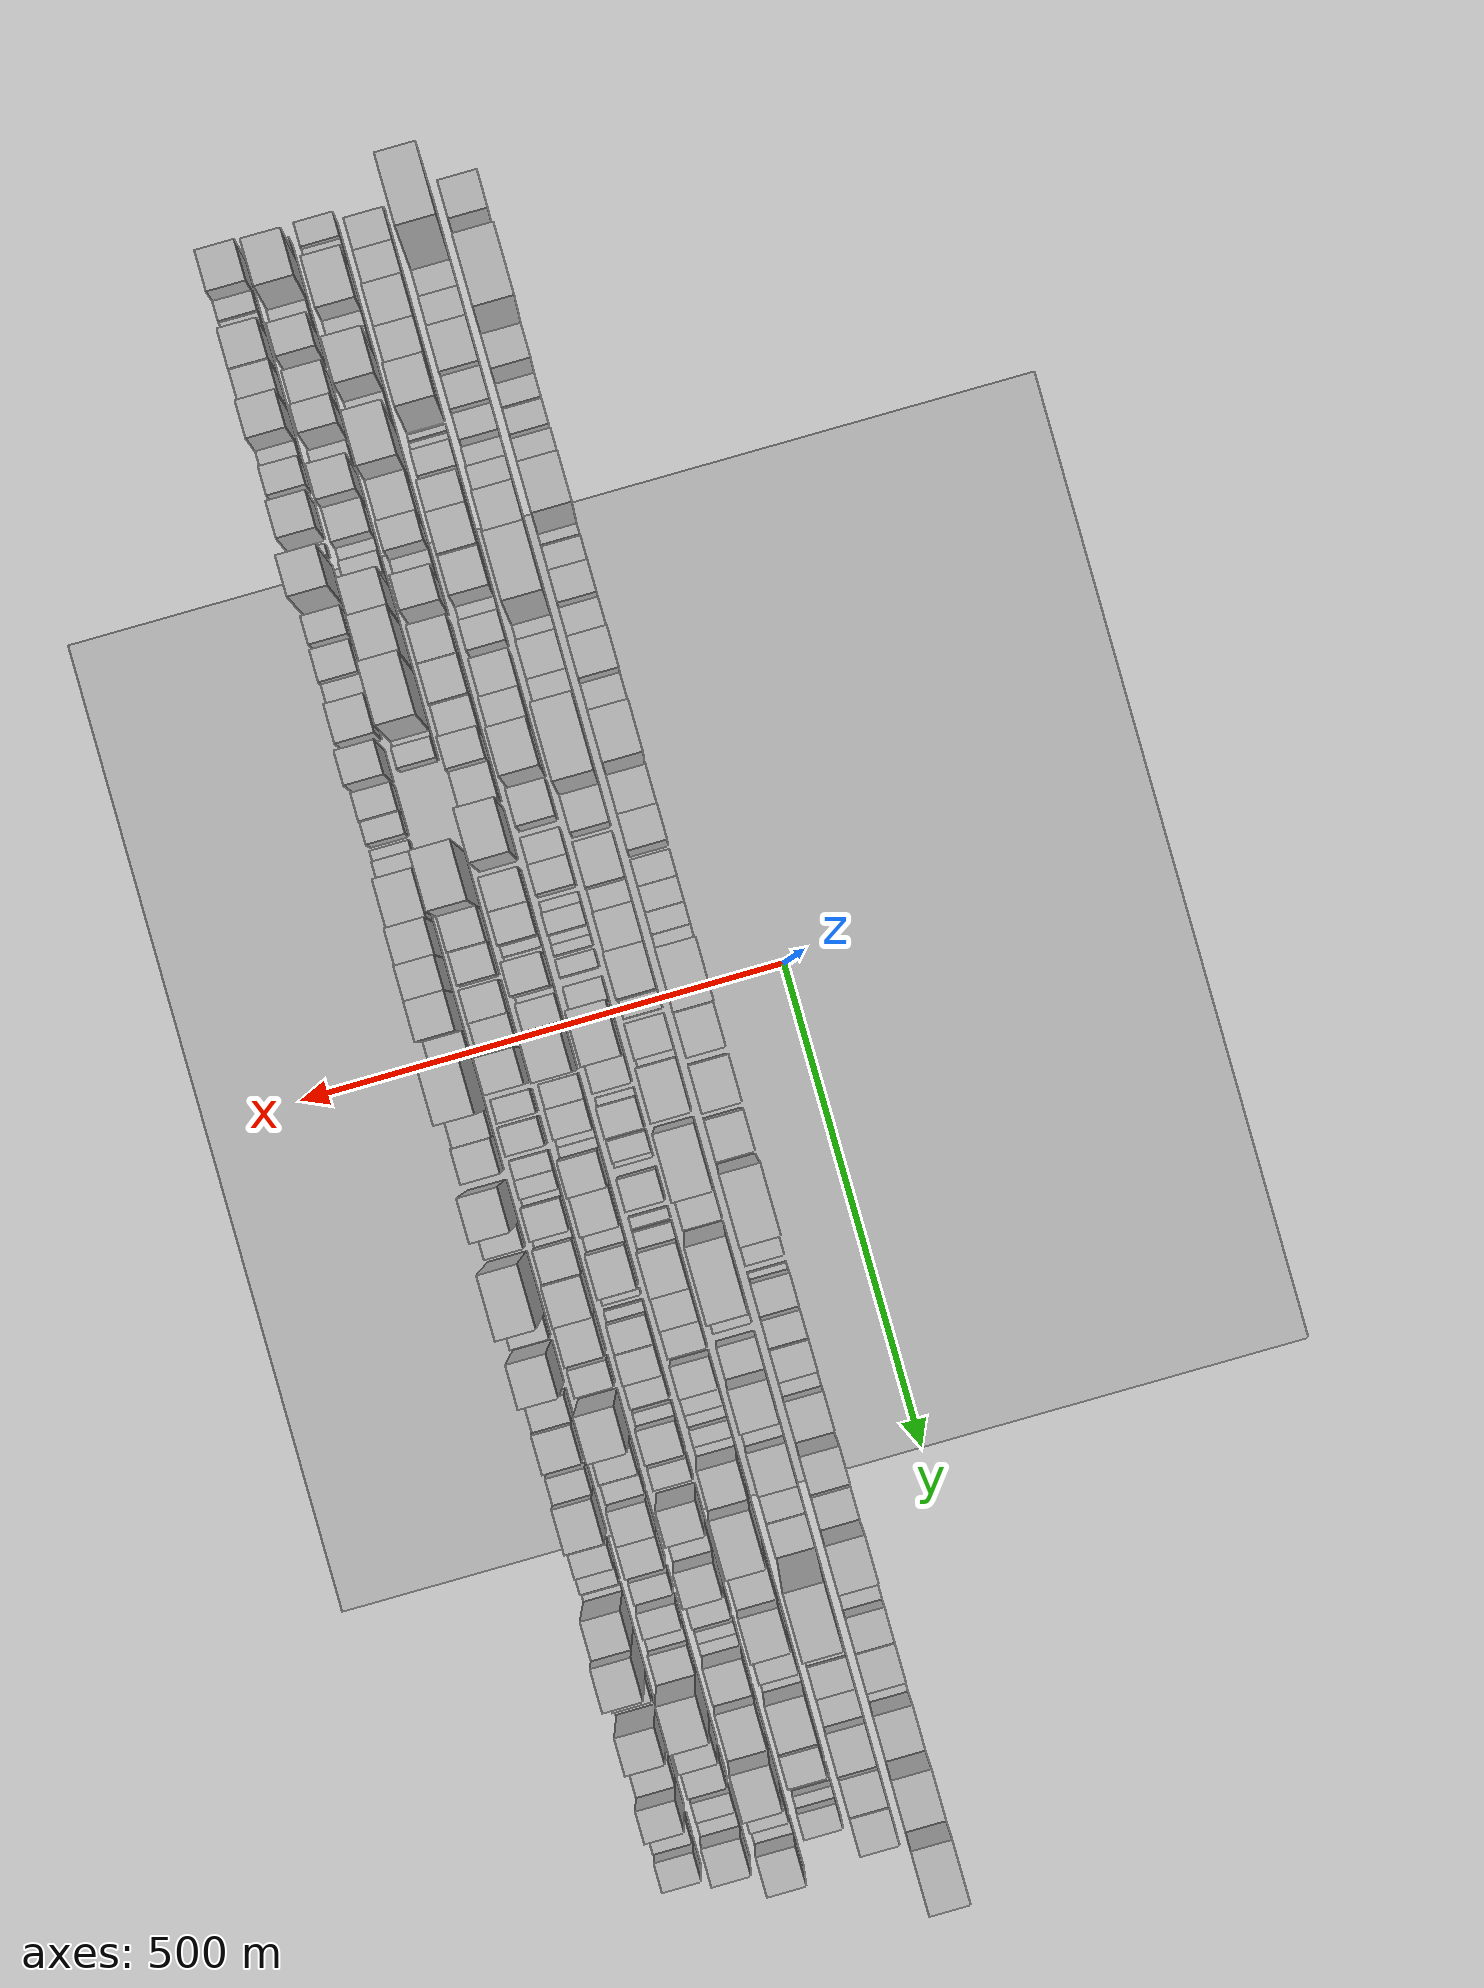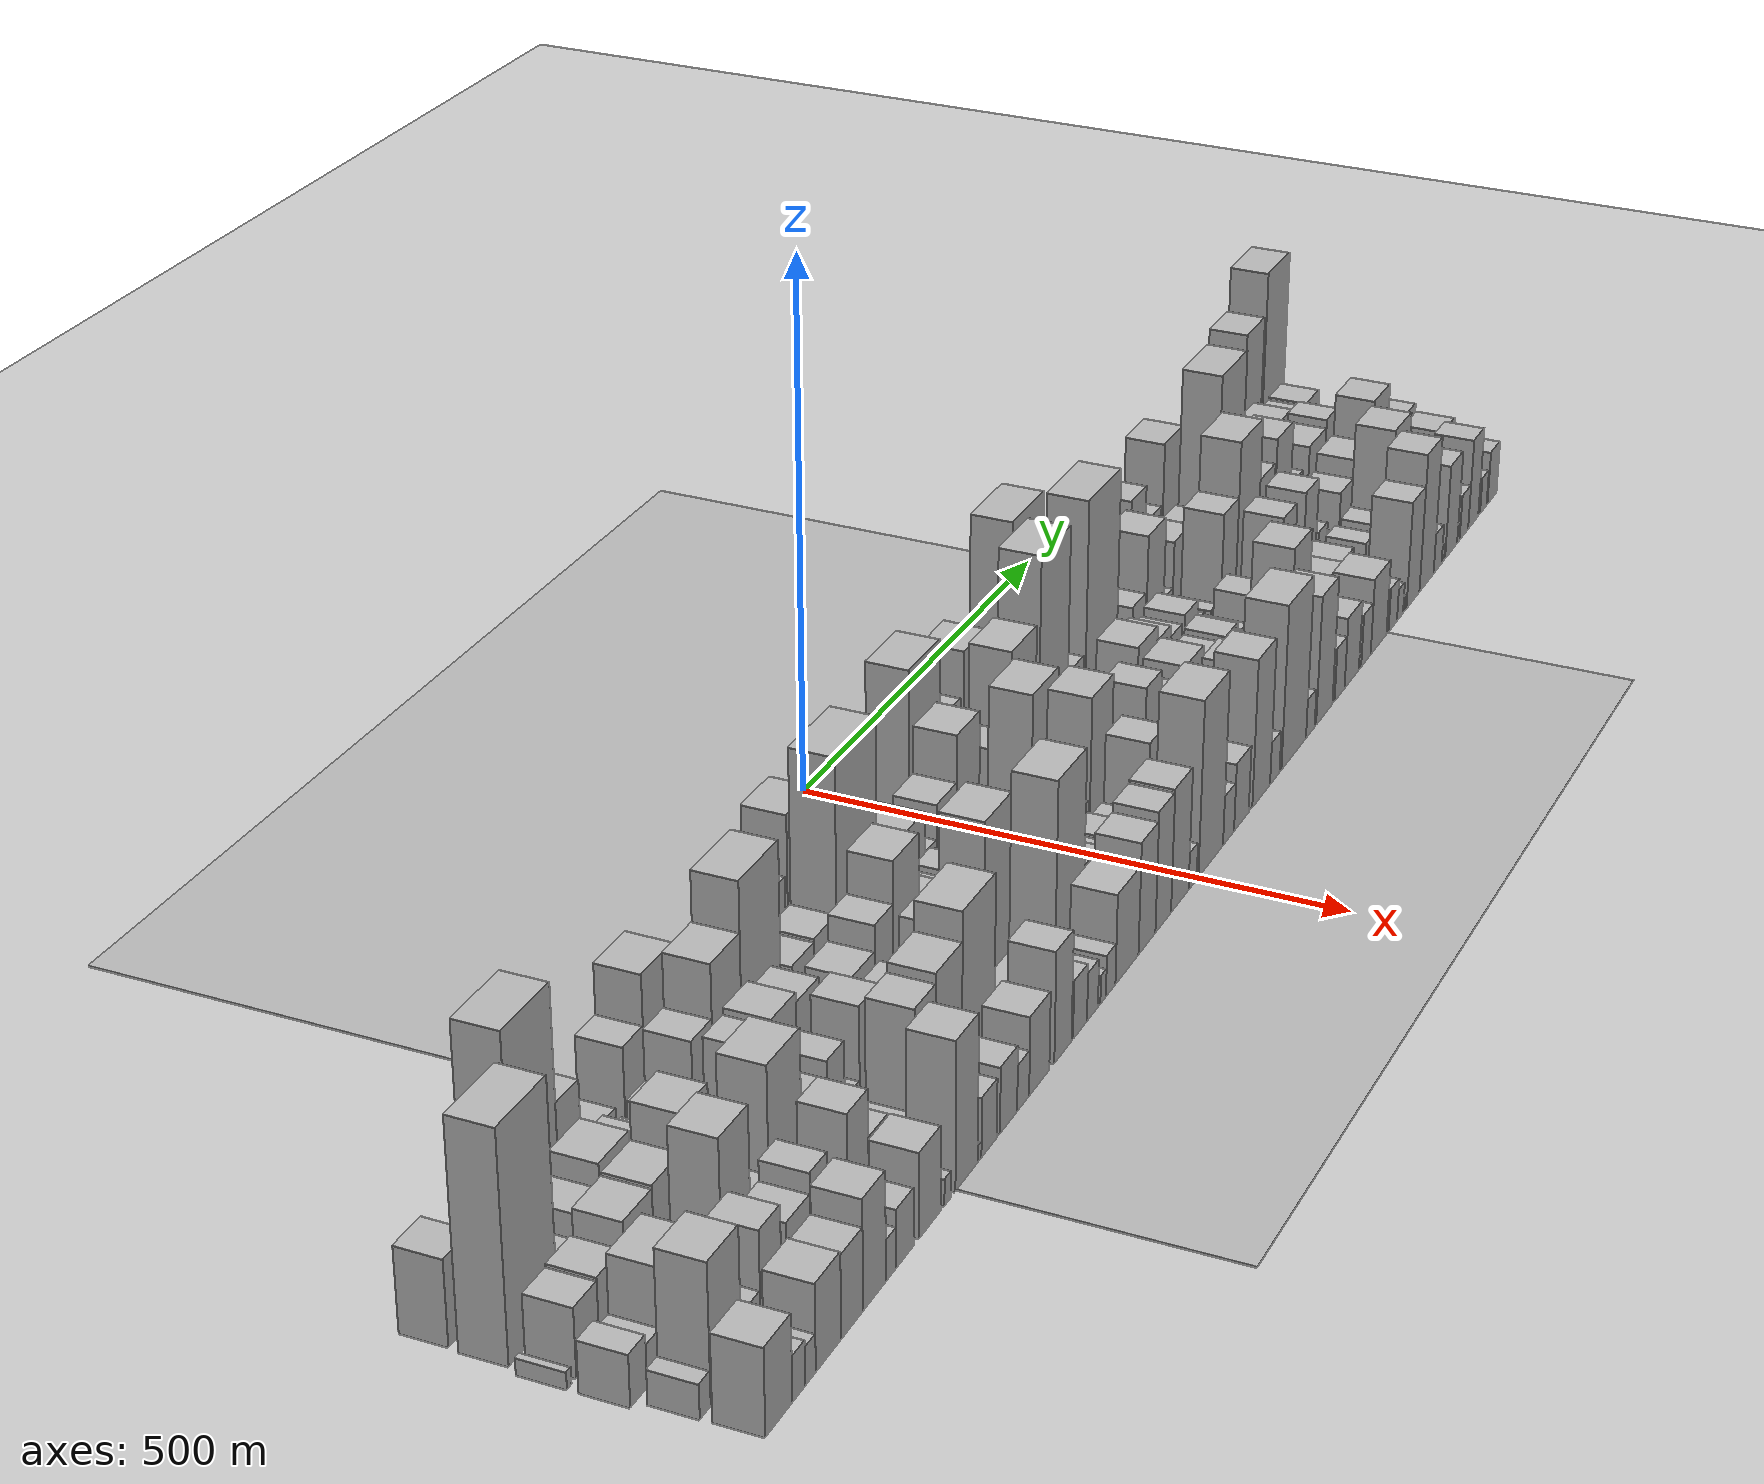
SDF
<?xml version="1.0" encoding="utf-8"?>

<sdf version="1.6">

   <world name="default">

      <gui fullscreen="0">

         <camera name="user_camera">

            <pose>-15 0 4.57585 0 0 0</pose>

            <view_controller>orbit</view_controller>

         </camera>

      </gui>

      <scene>

         <sky>

           <clouds>

             <speed>12</speed>

           </clouds>

         </sky>

         <ambient>0.4 0.4 0.4 1</ambient>

         <background>0.7 0.7 0.7 1</background>

         <shadows>1</shadows>

      </scene>

      <gravity>0 0 -9.8066</gravity>

      <magnetic_field>6e-06 2.3e-05 -4.2e-05</magnetic_field>

      <physics default="0" name="default_physics" type="ode">

         <ode>

            <solver>

               <type>quick</type>

               <iters>10</iters>

               <sor>1.0</sor>

               <use_dynamic_moi_rescaling>0</use_dynamic_moi_rescaling>

            </solver>

            <constraints>

               <cfm>0</cfm>

               <erp>0.2</erp>

               <contact_max_correcting_vel>100</contact_max_correcting_vel>

               <contact_surface_layer>0.001</contact_surface_layer>

            </constraints>

         </ode>

         <max_step_size>0.004</max_step_size>

         <real_time_factor>1</real_time_factor>

         <real_time_update_rate>250</real_time_update_rate>

      </physics>

      <light name="sun" type="directional">

         <cast_shadows>1</cast_shadows>

         <pose>0 0 10 0 0 0</pose>

         <diffuse>0.8 0.8 0.8 1</diffuse>

         <specular>0.2 0.2 0.2 1</specular>

         <attenuation>

            <range>1000</range>

            <constant>0.9</constant>

            <linear>0.01</linear>

            <quadratic>0.001</quadratic>

         </attenuation>

         <direction>-0.5 0.1 -0.9</direction>

      </light>

      <include>

         <name>ground_plane_1</name>

         <uri>model://HANNAS_ground_plane</uri>

         <pose>0 0 0  0 0 0</pose>

      </include>

      <include>

         <name>ground_plane_2</name>

         <uri>model://HANNAS_ground_plane</uri>

         <pose>100 0 0  0 0 0</pose>

      </include>

      <model name="building_1">

         <static>1</static>

         <pose frame="">100.0000 -802.6062 0 0.000000 0.000000 0.000000</pose>

         <link name="link">

            <pose frame="">0 0 37.50 0 0 0</pose>

            <collision name="collision">

               <geometry>

                  <box>

                     <size>40.0000 38.7875 75.0000</size>

                  </box>

               </geometry>

               <max_contacts>10</max_contacts>

               <surface>

                  <contact>

                     <ode/>

                  </contact>

                  <bounce/>

                  <friction>

                     <torsional>

                        <ode/>

                     </torsional>

                     <ode/>

                  </friction>

               </surface>

            </collision>

            <visual name="visual">

               <cast_shadows>0</cast_shadows>

               <geometry>

                  <box>

                     <size>40.0000 38.7875 75.0000</size>

                  </box>

               </geometry>

               <material>

                  <script>

                     <uri>model://HANNAS_wall/materials/scripts</uri>

                     <uri>model://HANNAS_wall/materials/textures</uri>

                     <name>vrc/HANNAS_wall</name>

                  </script>

               </material>

            </visual>

            <self_collide>0</self_collide>

            <enable_wind>0</enable_wind>

            <kinematic>0</kinematic>

         </link>

      </model>

      <model name="building_2">

         <static>1</static>

         <pose frame="">100.0000 -772.8537 0 0.000000 0.000000 0.000000</pose>

         <link name="link">

            <pose frame="">0 0 7.50 0 0 0</pose>

            <collision name="collision">

               <geometry>

                  <box>

                     <size>40.0000 6.7176 15.0000</size>

                  </box>

               </geometry>

               <max_contacts>10</max_contacts>

               <surface>

                  <contact>

                     <ode/>

                  </contact>

                  <bounce/>

                  <friction>

                     <torsional>

                        <ode/>

                     </torsional>

                     <ode/>

                  </friction>

               </surface>

            </collision>

            <visual name="visual">

               <cast_shadows>0</cast_shadows>

               <geometry>

                  <box>

                     <size>40.0000 6.7176 15.0000</size>

                  </box>

               </geometry>

               <material>

                  <script>

                     <uri>model://HANNAS_wall/materials/scripts</uri>

                     <uri>model://HANNAS_wall/materials/textures</uri>

                     <name>vrc/HANNAS_wall</name>

                  </script>

               </material>

            </visual>

            <self_collide>0</self_collide>

            <enable_wind>0</enable_wind>

            <kinematic>0</kinematic>

         </link>

      </model>

      <model name="building_3">

         <static>1</static>

         <pose frame="">100.0000 -752.0608 0 0.000000 0.000000 0.000000</pose>

         <link name="link">

            <pose frame="">0 0 21.00 0 0 0</pose>

            <collision name="collision">

               <geometry>

                  <box>

                     <size>40.0000 24.8681 42.0000</size>

                  </box>

               </geometry>

               <max_contacts>10</max_contacts>

               <surface>

                  <contact>

                     <ode/>

                  </contact>

                  <bounce/>

                  <friction>

                     <torsional>

                        <ode/>

                     </torsional>

                     <ode/>

                  </friction>

               </surface>

            </collision>

            <visual name="visual">

               <cast_shadows>0</cast_shadows>

               <geometry>

                  <box>

                     <size>40.0000 24.8681 42.0000</size>

                  </box>

               </geometry>

               <material>

                  <script>

                     <uri>model://HANNAS_wall/materials/scripts</uri>

                     <uri>model://HANNAS_wall/materials/textures</uri>

                     <name>vrc/HANNAS_wall</name>

                  </script>

               </material>

            </visual>

            <self_collide>0</self_collide>

            <enable_wind>0</enable_wind>

            <kinematic>0</kinematic>

         </link>

      </model>

      <model name="building_4">

         <static>1</static>

         <pose frame="">100.0000 -694.4256 0 0.000000 0.000000 0.000000</pose>

         <link name="link">

            <pose frame="">0 0 103.50 0 0 0</pose>

            <collision name="collision">

               <geometry>

                  <box>

                     <size>40.0000 70.4022 207.0000</size>

                  </box>

               </geometry>

               <max_contacts>10</max_contacts>

               <surface>

                  <contact>

                     <ode/>

                  </contact>

                  <bounce/>

                  <friction>

                     <torsional>

                        <ode/>

                     </torsional>

                     <ode/>

                  </friction>

               </surface>

            </collision>

            <visual name="visual">

               <cast_shadows>0</cast_shadows>

               <geometry>

                  <box>

                     <size>40.0000 70.4022 207.0000</size>

                  </box>

               </geometry>

               <material>

                  <script>

                     <uri>model://HANNAS_wall/materials/scripts</uri>

                     <uri>model://HANNAS_wall/materials/textures</uri>

                     <name>vrc/HANNAS_wall</name>

                  </script>

               </material>

            </visual>

            <self_collide>0</self_collide>

            <enable_wind>0</enable_wind>

            <kinematic>0</kinematic>

         </link>

      </model>

      <model name="building_5">

         <static>1</static>

         <pose frame="">100.0000 -641.9354 0 0.000000 0.000000 0.000000</pose>

         <link name="link">

            <pose frame="">0 0 52.50 0 0 0</pose>

            <collision name="collision">

               <geometry>

                  <box>

                     <size>40.0000 34.5782 105.0000</size>

                  </box>

               </geometry>

               <max_contacts>10</max_contacts>

               <surface>

                  <contact>

                     <ode/>

                  </contact>

                  <bounce/>

                  <friction>

                     <torsional>

                        <ode/>

                     </torsional>

                     <ode/>

                  </friction>

               </surface>

            </collision>

            <visual name="visual">

               <cast_shadows>0</cast_shadows>

               <geometry>

                  <box>

                     <size>40.0000 34.5782 105.0000</size>

                  </box>

               </geometry>

               <material>

                  <script>

                     <uri>model://HANNAS_wall/materials/scripts</uri>

                     <uri>model://HANNAS_wall/materials/textures</uri>

                     <name>vrc/HANNAS_wall</name>

                  </script>

               </material>

            </visual>

            <self_collide>0</self_collide>

            <enable_wind>0</enable_wind>

            <kinematic>0</kinematic>

         </link>

      </model>

      <model name="building_6">

         <static>1</static>

         <pose frame="">100.0000 -612.5772 0 0.000000 0.000000 0.000000</pose>

         <link name="link">

            <pose frame="">0 0 21.00 0 0 0</pose>

            <collision name="collision">

               <geometry>

                  <box>

                     <size>40.0000 24.1383 42.0000</size>

                  </box>

               </geometry>

               <max_contacts>10</max_contacts>

               <surface>

                  <contact>

                     <ode/>

                  </contact>

                  <bounce/>

                  <friction>

                     <torsional>

                        <ode/>

                     </torsional>

                     <ode/>

                  </friction>

               </surface>

            </collision>

            <visual name="visual">

               <cast_shadows>0</cast_shadows>

               <geometry>

                  <box>

                     <size>40.0000 24.1383 42.0000</size>

                  </box>

               </geometry>

               <material>

                  <script>

                     <uri>model://HANNAS_wall/materials/scripts</uri>

                     <uri>model://HANNAS_wall/materials/textures</uri>

                     <name>vrc/HANNAS_wall</name>

                  </script>

               </material>

            </visual>

            <self_collide>0</self_collide>

            <enable_wind>0</enable_wind>

            <kinematic>0</kinematic>

         </link>

      </model>

      <model name="building_7">

         <static>1</static>

         <pose frame="">100.0000 -584.4796 0 0.000000 0.000000 0.000000</pose>

         <link name="link">

            <pose frame="">0 0 24.00 0 0 0</pose>

            <collision name="collision">

               <geometry>

                  <box>

                     <size>40.0000 26.0570 48.0000</size>

                  </box>

               </geometry>

               <max_contacts>10</max_contacts>

               <surface>

                  <contact>

                     <ode/>

                  </contact>

                  <bounce/>

                  <friction>

                     <torsional>

                        <ode/>

                     </torsional>

                     <ode/>

                  </friction>

               </surface>

            </collision>

            <visual name="visual">

               <cast_shadows>0</cast_shadows>

               <geometry>

                  <box>

                     <size>40.0000 26.0570 48.0000</size>

                  </box>

               </geometry>

               <material>

                  <script>

                     <uri>model://HANNAS_wall/materials/scripts</uri>

                     <uri>model://HANNAS_wall/materials/textures</uri>

                     <name>vrc/HANNAS_wall</name>

                  </script>

               </material>

            </visual>

            <self_collide>0</self_collide>

            <enable_wind>0</enable_wind>

            <kinematic>0</kinematic>

         </link>

      </model>

      <model name="building_8">

         <static>1</static>

         <pose frame="">100.0000 -565.9233 0 0.000000 0.000000 0.000000</pose>

         <link name="link">

            <pose frame="">0 0 13.50 0 0 0</pose>

            <collision name="collision">

               <geometry>

                  <box>

                     <size>40.0000 11.0555 27.0000</size>

                  </box>

               </geometry>

               <max_contacts>10</max_contacts>

               <surface>

                  <contact>

                     <ode/>

                  </contact>

                  <bounce/>

                  <friction>

                     <torsional>

                        <ode/>

                     </torsional>

                     <ode/>

                  </friction>

               </surface>

            </collision>

            <visual name="visual">

               <cast_shadows>0</cast_shadows>

               <geometry>

                  <box>

                     <size>40.0000 11.0555 27.0000</size>

                  </box>

               </geometry>

               <material>

                  <script>

                     <uri>model://HANNAS_wall/materials/scripts</uri>

                     <uri>model://HANNAS_wall/materials/textures</uri>

                     <name>vrc/HANNAS_wall</name>

                  </script>

               </material>

            </visual>

            <self_collide>0</self_collide>

            <enable_wind>0</enable_wind>

            <kinematic>0</kinematic>

         </link>

      </model>

      <model name="building_9">

         <static>1</static>

         <pose frame="">100.0000 -541.3138 0 0.000000 0.000000 0.000000</pose>

         <link name="link">

            <pose frame="">0 0 46.50 0 0 0</pose>

            <collision name="collision">

               <geometry>

                  <box>

                     <size>40.0000 32.1635 93.0000</size>

                  </box>

               </geometry>

               <max_contacts>10</max_contacts>

               <surface>

                  <contact>

                     <ode/>

                  </contact>

                  <bounce/>

                  <friction>

                     <torsional>

                        <ode/>

                     </torsional>

                     <ode/>

                  </friction>

               </surface>

            </collision>

            <visual name="visual">

               <cast_shadows>0</cast_shadows>

               <geometry>

                  <box>

                     <size>40.0000 32.1635 93.0000</size>

                  </box>

               </geometry>

               <material>

                  <script>

                     <uri>model://HANNAS_wall/materials/scripts</uri>

                     <uri>model://HANNAS_wall/materials/textures</uri>

                     <name>vrc/HANNAS_wall</name>

                  </script>

               </material>

            </visual>

            <self_collide>0</self_collide>

            <enable_wind>0</enable_wind>

            <kinematic>0</kinematic>

         </link>

      </model>

      <model name="building_10">

         <static>1</static>

         <pose frame="">100.0000 -499.8838 0 0.000000 0.000000 0.000000</pose>

         <link name="link">

            <pose frame="">0 0 69.00 0 0 0</pose>

            <collision name="collision">

               <geometry>

                  <box>

                     <size>40.0000 50.6964 138.0000</size>

                  </box>

               </geometry>

               <max_contacts>10</max_contacts>

               <surface>

                  <contact>

                     <ode/>

                  </contact>

                  <bounce/>

                  <friction>

                     <torsional>

                        <ode/>

                     </torsional>

                     <ode/>

                  </friction>

               </surface>

            </collision>

            <visual name="visual">

               <cast_shadows>0</cast_shadows>

               <geometry>

                  <box>

                     <size>40.0000 50.6964 138.0000</size>

                  </box>

               </geometry>

               <material>

                  <script>

                     <uri>model://HANNAS_wall/materials/scripts</uri>

                     <uri>model://HANNAS_wall/materials/textures</uri>

                     <name>vrc/HANNAS_wall</name>

                  </script>

               </material>

            </visual>

            <self_collide>0</self_collide>

            <enable_wind>0</enable_wind>

            <kinematic>0</kinematic>

         </link>

      </model>

      <model name="building_11">

         <static>1</static>

         <pose frame="">100.0000 -469.0723 0 0.000000 0.000000 0.000000</pose>

         <link name="link">

            <pose frame="">0 0 12.00 0 0 0</pose>

            <collision name="collision">

               <geometry>

                  <box>

                     <size>40.0000 10.9267 24.0000</size>

                  </box>

               </geometry>

               <max_contacts>10</max_contacts>

               <surface>

                  <contact>

                     <ode/>

                  </contact>

                  <bounce/>

                  <friction>

                     <torsional>

                        <ode/>

                     </torsional>

                     <ode/>

                  </friction>

               </surface>

            </collision>

            <visual name="visual">

               <cast_shadows>0</cast_shadows>

               <geometry>

                  <box>

                     <size>40.0000 10.9267 24.0000</size>

                  </box>

               </geometry>

               <material>

                  <script>

                     <uri>model://HANNAS_wall/materials/scripts</uri>

                     <uri>model://HANNAS_wall/materials/textures</uri>

                     <name>vrc/HANNAS_wall</name>

                  </script>

               </material>

            </visual>

            <self_collide>0</self_collide>

            <enable_wind>0</enable_wind>

            <kinematic>0</kinematic>

         </link>

      </model>

      <model name="building_12">

         <static>1</static>

         <pose frame="">100.0000 -460.4415 0 0.000000 0.000000 0.000000</pose>

         <link name="link">

            <pose frame="">0 0 7.50 0 0 0</pose>

            <collision name="collision">

               <geometry>

                  <box>

                     <size>40.0000 6.3347 15.0000</size>

                  </box>

               </geometry>

               <max_contacts>10</max_contacts>

               <surface>

                  <contact>

                     <ode/>

                  </contact>

                  <bounce/>

                  <friction>

                     <torsional>

                        <ode/>

                     </torsional>

                     <ode/>

                  </friction>

               </surface>

            </collision>

            <visual name="visual">

               <cast_shadows>0</cast_shadows>

               <geometry>

                  <box>

                     <size>40.0000 6.3347 15.0000</size>

                  </box>

               </geometry>

               <material>

                  <script>

                     <uri>model://HANNAS_wall/materials/scripts</uri>

                     <uri>model://HANNAS_wall/materials/textures</uri>

                     <name>vrc/HANNAS_wall</name>

                  </script>

               </material>

            </visual>

            <self_collide>0</self_collide>

            <enable_wind>0</enable_wind>

            <kinematic>0</kinematic>

         </link>

      </model>

      <model name="building_13">

         <static>1</static>

         <pose frame="">100.0000 -443.9458 0 0.000000 0.000000 0.000000</pose>

         <link name="link">

            <pose frame="">0 0 25.50 0 0 0</pose>

            <collision name="collision">

               <geometry>

                  <box>

                     <size>40.0000 26.6568 51.0000</size>

                  </box>

               </geometry>

               <max_contacts>10</max_contacts>

               <surface>

                  <contact>

                     <ode/>

                  </contact>

                  <bounce/>

                  <friction>

                     <torsional>

                        <ode/>

                     </torsional>

                     <ode/>

                  </friction>

               </surface>

            </collision>

            <visual name="visual">

               <cast_shadows>0</cast_shadows>

               <geometry>

                  <box>

                     <size>40.0000 26.6568 51.0000</size>

                  </box>

               </geometry>

               <material>

                  <script>

                     <uri>model://HANNAS_wall/materials/scripts</uri>

                     <uri>model://HANNAS_wall/materials/textures</uri>

                     <name>vrc/HANNAS_wall</name>

                  </script>

               </material>

            </visual>

            <self_collide>0</self_collide>

            <enable_wind>0</enable_wind>

            <kinematic>0</kinematic>

         </link>

      </model>

      <model name="building_14">

         <static>1</static>

         <pose frame="">100.0000 -414.1165 0 0.000000 0.000000 0.000000</pose>

         <link name="link">

            <pose frame="">0 0 33.00 0 0 0</pose>

            <collision name="collision">

               <geometry>

                  <box>

                     <size>40.0000 33.0019 66.0000</size>

                  </box>

               </geometry>

               <max_contacts>10</max_contacts>

               <surface>

                  <contact>

                     <ode/>

                  </contact>

                  <bounce/>

                  <friction>

                     <torsional>

                        <ode/>

                     </torsional>

                     <ode/>

                  </friction>

               </surface>

            </collision>

            <visual name="visual">

               <cast_shadows>0</cast_shadows>

               <geometry>

                  <box>

                     <size>40.0000 33.0019 66.0000</size>

                  </box>

               </geometry>

               <material>

                  <script>

                     <uri>model://HANNAS_wall/materials/scripts</uri>

                     <uri>model://HANNAS_wall/materials/textures</uri>

                     <name>vrc/HANNAS_wall</name>

                  </script>

               </material>

            </visual>

            <self_collide>0</self_collide>

            <enable_wind>0</enable_wind>

            <kinematic>0</kinematic>

         </link>

      </model>

      <model name="building_15">

         <static>1</static>

         <pose frame="">100.0000 -373.3986 0 0.000000 0.000000 0.000000</pose>

         <link name="link">

            <pose frame="">0 0 33.00 0 0 0</pose>

            <collision name="collision">

               <geometry>

                  <box>

                     <size>40.0000 38.4339 66.0000</size>

                  </box>

               </geometry>

               <max_contacts>10</max_contacts>

               <surface>

                  <contact>

                     <ode/>

                  </contact>

                  <bounce/>

                  <friction>

                     <torsional>

                        <ode/>

                     </torsional>

                     <ode/>

                  </friction>

               </surface>

            </collision>

            <visual name="visual">

               <cast_shadows>0</cast_shadows>

               <geometry>

                  <box>

                     <size>40.0000 38.4339 66.0000</size>

                  </box>

               </geometry>

               <material>

                  <script>

                     <uri>model://HANNAS_wall/materials/scripts</uri>

                     <uri>model://HANNAS_wall/materials/textures</uri>

                     <name>vrc/HANNAS_wall</name>

                  </script>

               </material>

            </visual>

            <self_collide>0</self_collide>

            <enable_wind>0</enable_wind>

            <kinematic>0</kinematic>

         </link>

      </model>

      <model name="building_16">

         <static>1</static>

         <pose frame="">100.0000 -333.3017 0 0.000000 0.000000 0.000000</pose>

         <link name="link">

            <pose frame="">0 0 66.00 0 0 0</pose>

            <collision name="collision">

               <geometry>

                  <box>

                     <size>40.0000 41.7599 132.0000</size>

                  </box>

               </geometry>

               <max_contacts>10</max_contacts>

               <surface>

                  <contact>

                     <ode/>

                  </contact>

                  <bounce/>

                  <friction>

                     <torsional>

                        <ode/>

                     </torsional>

                     <ode/>

                  </friction>

               </surface>

            </collision>

            <visual name="visual">

               <cast_shadows>0</cast_shadows>

               <geometry>

                  <box>

                     <size>40.0000 41.7599 132.0000</size>

                  </box>

               </geometry>

               <material>

                  <script>

                     <uri>model://HANNAS_wall/materials/scripts</uri>

                     <uri>model://HANNAS_wall/materials/textures</uri>

                     <name>vrc/HANNAS_wall</name>

                  </script>

               </material>

            </visual>

            <self_collide>0</self_collide>

            <enable_wind>0</enable_wind>

            <kinematic>0</kinematic>

         </link>

      </model>

      <model name="building_17">

         <static>1</static>

         <pose frame="">100.0000 -297.9540 0 0.000000 0.000000 0.000000</pose>

         <link name="link">

            <pose frame="">0 0 46.50 0 0 0</pose>

            <collision name="collision">

               <geometry>

                  <box>

                     <size>40.0000 28.9357 93.0000</size>

                  </box>

               </geometry>

               <max_contacts>10</max_contacts>

               <surface>

                  <contact>

                     <ode/>

                  </contact>

                  <bounce/>

                  <friction>

                     <torsional>

                        <ode/>

                     </torsional>

                     <ode/>

                  </friction>

               </surface>

            </collision>

            <visual name="visual">

               <cast_shadows>0</cast_shadows>

               <geometry>

                  <box>

                     <size>40.0000 28.9357 93.0000</size>

                  </box>

               </geometry>

               <material>

                  <script>

                     <uri>model://HANNAS_wall/materials/scripts</uri>

                     <uri>model://HANNAS_wall/materials/textures</uri>

                     <name>vrc/HANNAS_wall</name>

                  </script>

               </material>

            </visual>

            <self_collide>0</self_collide>

            <enable_wind>0</enable_wind>

            <kinematic>0</kinematic>

         </link>

      </model>

      <model name="building_18">

         <static>1</static>

         <pose frame="">100.0000 -253.5364 0 0.000000 0.000000 0.000000</pose>

         <link name="link">

            <pose frame="">0 0 73.50 0 0 0</pose>

            <collision name="collision">

               <geometry>

                  <box>

                     <size>40.0000 51.8995 147.0000</size>

                  </box>

               </geometry>

               <max_contacts>10</max_contacts>

               <surface>

                  <contact>

                     <ode/>

                  </contact>

                  <bounce/>

                  <friction>

                     <torsional>

                        <ode/>

                     </torsional>

                     <ode/>

                  </friction>

               </surface>

            </collision>

            <visual name="visual">

               <cast_shadows>0</cast_shadows>

               <geometry>

                  <box>

                     <size>40.0000 51.8995 147.0000</size>

                  </box>

               </geometry>

               <material>

                  <script>

                     <uri>model://HANNAS_wall/materials/scripts</uri>

                     <uri>model://HANNAS_wall/materials/textures</uri>

                     <name>vrc/HANNAS_wall</name>

                  </script>

               </material>

            </visual>

            <self_collide>0</self_collide>

            <enable_wind>0</enable_wind>

            <kinematic>0</kinematic>

         </link>

      </model>

      <model name="building_19">

         <static>1</static>

         <pose frame="">100.0000 -201.8967 0 0.000000 0.000000 0.000000</pose>

         <link name="link">

            <pose frame="">0 0 37.50 0 0 0</pose>

            <collision name="collision">

               <geometry>

                  <box>

                     <size>40.0000 41.3797 75.0000</size>

                  </box>

               </geometry>

               <max_contacts>10</max_contacts>

               <surface>

                  <contact>

                     <ode/>

                  </contact>

                  <bounce/>

                  <friction>

                     <torsional>

                        <ode/>

                     </torsional>

                     <ode/>

                  </friction>

               </surface>

            </collision>

            <visual name="visual">

               <cast_shadows>0</cast_shadows>

               <geometry>

                  <box>

                     <size>40.0000 41.3797 75.0000</size>

                  </box>

               </geometry>

               <material>

                  <script>

                     <uri>model://HANNAS_wall/materials/scripts</uri>

                     <uri>model://HANNAS_wall/materials/textures</uri>

                     <name>vrc/HANNAS_wall</name>

                  </script>

               </material>

            </visual>

            <self_collide>0</self_collide>

            <enable_wind>0</enable_wind>

            <kinematic>0</kinematic>

         </link>

      </model>

      <model name="building_20">

         <static>1</static>

         <pose frame="">100.0000 -162.9581 0 0.000000 0.000000 0.000000</pose>

         <link name="link">

            <pose frame="">0 0 49.50 0 0 0</pose>

            <collision name="collision">

               <geometry>

                  <box>

                     <size>40.0000 36.4976 99.0000</size>

                  </box>

               </geometry>

               <max_contacts>10</max_contacts>

               <surface>

                  <contact>

                     <ode/>

                  </contact>

                  <bounce/>

                  <friction>

                     <torsional>

                        <ode/>

                     </torsional>

                     <ode/>

                  </friction>

               </surface>

            </collision>

            <visual name="visual">

               <cast_shadows>0</cast_shadows>

               <geometry>

                  <box>

                     <size>40.0000 36.4976 99.0000</size>

                  </box>

               </geometry>

               <material>

                  <script>

                     <uri>model://HANNAS_wall/materials/scripts</uri>

                     <uri>model://HANNAS_wall/materials/textures</uri>

                     <name>vrc/HANNAS_wall</name>

                  </script>

               </material>

            </visual>

            <self_collide>0</self_collide>

            <enable_wind>0</enable_wind>

            <kinematic>0</kinematic>

         </link>

      </model>

      <model name="building_21">

         <static>1</static>

         <pose frame="">100.0000 -125.1048 0 0.000000 0.000000 0.000000</pose>

         <link name="link">

            <pose frame="">0 0 25.50 0 0 0</pose>

            <collision name="collision">

               <geometry>

                  <box>

                     <size>40.0000 27.2089 51.0000</size>

                  </box>

               </geometry>

               <max_contacts>10</max_contacts>

               <surface>

                  <contact>

                     <ode/>

                  </contact>

                  <bounce/>

                  <friction>

                     <torsional>

                        <ode/>

                     </torsional>

                     <ode/>

                  </friction>

               </surface>

            </collision>

            <visual name="visual">

               <cast_shadows>0</cast_shadows>

               <geometry>

                  <box>

                     <size>40.0000 27.2089 51.0000</size>

                  </box>

               </geometry>

               <material>

                  <script>

                     <uri>model://HANNAS_wall/materials/scripts</uri>

                     <uri>model://HANNAS_wall/materials/textures</uri>

                     <name>vrc/HANNAS_wall</name>

                  </script>

               </material>

            </visual>

            <self_collide>0</self_collide>

            <enable_wind>0</enable_wind>

            <kinematic>0</kinematic>

         </link>

      </model>

      <model name="building_22">

         <static>1</static>

         <pose frame="">100.0000 -98.4155 0 0.000000 0.000000 0.000000</pose>

         <link name="link">

            <pose frame="">0 0 24.00 0 0 0</pose>

            <collision name="collision">

               <geometry>

                  <box>

                     <size>40.0000 26.1698 48.0000</size>

                  </box>

               </geometry>

               <max_contacts>10</max_contacts>

               <surface>

                  <contact>

                     <ode/>

                  </contact>

                  <bounce/>

                  <friction>

                     <torsional>

                        <ode/>

                     </torsional>

                     <ode/>

                  </friction>

               </surface>

            </collision>

            <visual name="visual">

               <cast_shadows>0</cast_shadows>

               <geometry>

                  <box>

                     <size>40.0000 26.1698 48.0000</size>

                  </box>

               </geometry>

               <material>

                  <script>

                     <uri>model://HANNAS_wall/materials/scripts</uri>

                     <uri>model://HANNAS_wall/materials/textures</uri>

                     <name>vrc/HANNAS_wall</name>

                  </script>

               </material>

            </visual>

            <self_collide>0</self_collide>

            <enable_wind>0</enable_wind>

            <kinematic>0</kinematic>

         </link>

      </model>

      <model name="building_23">

         <static>1</static>

         <pose frame="">100.0000 -74.0926 0 0.000000 0.000000 0.000000</pose>

         <link name="link">

            <pose frame="">0 0 21.00 0 0 0</pose>

            <collision name="collision">

               <geometry>

                  <box>

                     <size>40.0000 22.4760 42.0000</size>

                  </box>

               </geometry>

               <max_contacts>10</max_contacts>

               <surface>

                  <contact>

                     <ode/>

                  </contact>

                  <bounce/>

                  <friction>

                     <torsional>

                        <ode/>

                     </torsional>

                     <ode/>

                  </friction>

               </surface>

            </collision>

            <visual name="visual">

               <cast_shadows>0</cast_shadows>

               <geometry>

                  <box>

                     <size>40.0000 22.4760 42.0000</size>

                  </box>

               </geometry>

               <material>

                  <script>

                     <uri>model://HANNAS_wall/materials/scripts</uri>

                     <uri>model://HANNAS_wall/materials/textures</uri>

                     <name>vrc/HANNAS_wall</name>

                  </script>

               </material>

            </visual>

            <self_collide>0</self_collide>

            <enable_wind>0</enable_wind>

            <kinematic>0</kinematic>

         </link>

      </model>

      <model name="building_24">

         <static>1</static>

         <pose frame="">100.0000 -54.2454 0 0.000000 0.000000 0.000000</pose>

         <link name="link">

            <pose frame="">0 0 16.50 0 0 0</pose>

            <collision name="collision">

               <geometry>

                  <box>

                     <size>40.0000 17.2185 33.0000</size>

                  </box>

               </geometry>

               <max_contacts>10</max_contacts>

               <surface>

                  <contact>

                     <ode/>

                  </contact>

                  <bounce/>

                  <friction>

                     <torsional>

                        <ode/>

                     </torsional>

                     <ode/>

                  </friction>

               </surface>

            </collision>

            <visual name="visual">

               <cast_shadows>0</cast_shadows>

               <geometry>

                  <box>

                     <size>40.0000 17.2185 33.0000</size>

                  </box>

               </geometry>

               <material>

                  <script>

                     <uri>model://HANNAS_wall/materials/scripts</uri>

                     <uri>model://HANNAS_wall/materials/textures</uri>

                     <name>vrc/HANNAS_wall</name>

                  </script>

               </material>

            </visual>

            <self_collide>0</self_collide>

            <enable_wind>0</enable_wind>

            <kinematic>0</kinematic>

         </link>

      </model>

      <model name="building_25">

         <static>1</static>

         <pose frame="">100.0000 -14.2065 0 0.000000 0.000000 0.000000</pose>

         <link name="link">

            <pose frame="">0 0 82.50 0 0 0</pose>

            <collision name="collision">

               <geometry>

                  <box>

                     <size>40.0000 62.8592 165.0000</size>

                  </box>

               </geometry>

               <max_contacts>10</max_contacts>

               <surface>

                  <contact>

                     <ode/>

                  </contact>

                  <bounce/>

                  <friction>

                     <torsional>

                        <ode/>

                     </torsional>

                     <ode/>

                  </friction>

               </surface>

            </collision>

            <visual name="visual">

               <cast_shadows>0</cast_shadows>

               <geometry>

                  <box>

                     <size>40.0000 62.8592 165.0000</size>

                  </box>

               </geometry>

               <material>

                  <script>

                     <uri>model://HANNAS_wall/materials/scripts</uri>

                     <uri>model://HANNAS_wall/materials/textures</uri>

                     <name>vrc/HANNAS_wall</name>

                  </script>

               </material>

            </visual>

            <self_collide>0</self_collide>

            <enable_wind>0</enable_wind>

            <kinematic>0</kinematic>

         </link>

      </model>

      <model name="building_26">

         <static>1</static>

         <pose frame="">100.0000 39.8798 0 0.000000 0.000000 0.000000</pose>

         <link name="link">

            <pose frame="">0 0 43.50 0 0 0</pose>

            <collision name="collision">

               <geometry>

                  <box>

                     <size>40.0000 45.3134 87.0000</size>

                  </box>

               </geometry>

               <max_contacts>10</max_contacts>

               <surface>

                  <contact>

                     <ode/>

                  </contact>

                  <bounce/>

                  <friction>

                     <torsional>

                        <ode/>

                     </torsional>

                     <ode/>

                  </friction>

               </surface>

            </collision>

            <visual name="visual">

               <cast_shadows>0</cast_shadows>

               <geometry>

                  <box>

                     <size>40.0000 45.3134 87.0000</size>

                  </box>

               </geometry>

               <material>

                  <script>

                     <uri>model://HANNAS_wall/materials/scripts</uri>

                     <uri>model://HANNAS_wall/materials/textures</uri>

                     <name>vrc/HANNAS_wall</name>

                  </script>

               </material>

            </visual>

            <self_collide>0</self_collide>

            <enable_wind>0</enable_wind>

            <kinematic>0</kinematic>

         </link>

      </model>

      <model name="building_27">

         <static>1</static>

         <pose frame="">100.0000 93.4120 0 0.000000 0.000000 0.000000</pose>

         <link name="link">

            <pose frame="">0 0 64.50 0 0 0</pose>

            <collision name="collision">

               <geometry>

                  <box>

                     <size>40.0000 47.7509 129.0000</size>

                  </box>

               </geometry>

               <max_contacts>10</max_contacts>

               <surface>

                  <contact>

                     <ode/>

                  </contact>

                  <bounce/>

                  <friction>

                     <torsional>

                        <ode/>

                     </torsional>

                     <ode/>

                  </friction>

               </surface>

            </collision>

            <visual name="visual">

               <cast_shadows>0</cast_shadows>

               <geometry>

                  <box>

                     <size>40.0000 47.7509 129.0000</size>

                  </box>

               </geometry>

               <material>

                  <script>

                     <uri>model://HANNAS_wall/materials/scripts</uri>

                     <uri>model://HANNAS_wall/materials/textures</uri>

                     <name>vrc/HANNAS_wall</name>

                  </script>

               </material>

            </visual>

            <self_collide>0</self_collide>

            <enable_wind>0</enable_wind>

            <kinematic>0</kinematic>

         </link>

      </model>

      <model name="building_28">

         <static>1</static>

         <pose frame="">100.0000 146.5997 0 0.000000 0.000000 0.000000</pose>

         <link name="link">

            <pose frame="">0 0 37.50 0 0 0</pose>

            <collision name="collision">

               <geometry>

                  <box>

                     <size>40.0000 42.6245 75.0000</size>

                  </box>

               </geometry>

               <max_contacts>10</max_contacts>

               <surface>

                  <contact>

                     <ode/>

                  </contact>

                  <bounce/>

                  <friction>

                     <torsional>

                        <ode/>

                     </torsional>

                     <ode/>

                  </friction>

               </surface>

            </collision>

            <visual name="visual">

               <cast_shadows>0</cast_shadows>

               <geometry>

                  <box>

                     <size>40.0000 42.6245 75.0000</size>

                  </box>

               </geometry>

               <material>

                  <script>

                     <uri>model://HANNAS_wall/materials/scripts</uri>

                     <uri>model://HANNAS_wall/materials/textures</uri>

                     <name>vrc/HANNAS_wall</name>

                  </script>

               </material>

            </visual>

            <self_collide>0</self_collide>

            <enable_wind>0</enable_wind>

            <kinematic>0</kinematic>

         </link>

      </model>

      <model name="building_29">

         <static>1</static>

         <pose frame="">100.0000 208.2416 0 0.000000 0.000000 0.000000</pose>

         <link name="link">

            <pose frame="">0 0 103.50 0 0 0</pose>

            <collision name="collision">

               <geometry>

                  <box>

                     <size>40.0000 70.6594 207.0000</size>

                  </box>

               </geometry>

               <max_contacts>10</max_contacts>

               <surface>

                  <contact>

                     <ode/>

                  </contact>

                  <bounce/>

                  <friction>

                     <torsional>

                        <ode/>

                     </torsional>

                     <ode/>

                  </friction>

               </surface>

            </collision>

            <visual name="visual">

               <cast_shadows>0</cast_shadows>

               <geometry>

                  <box>

                     <size>40.0000 70.6594 207.0000</size>

                  </box>

               </geometry>

               <material>

                  <script>

                     <uri>model://HANNAS_wall/materials/scripts</uri>

                     <uri>model://HANNAS_wall/materials/textures</uri>

                     <name>vrc/HANNAS_wall</name>

                  </script>

               </material>

            </visual>

            <self_collide>0</self_collide>

            <enable_wind>0</enable_wind>

            <kinematic>0</kinematic>

         </link>

      </model>

      <model name="building_30">

         <static>1</static>

         <pose frame="">100.0000 262.0798 0 0.000000 0.000000 0.000000</pose>

         <link name="link">

            <pose frame="">0 0 24.00 0 0 0</pose>

            <collision name="collision">

               <geometry>

                  <box>

                     <size>40.0000 25.0170 48.0000</size>

                  </box>

               </geometry>

               <max_contacts>10</max_contacts>

               <surface>

                  <contact>

                     <ode/>

                  </contact>

                  <bounce/>

                  <friction>

                     <torsional>

                        <ode/>

                     </torsional>

                     <ode/>

                  </friction>

               </surface>

            </collision>

            <visual name="visual">

               <cast_shadows>0</cast_shadows>

               <geometry>

                  <box>

                     <size>40.0000 25.0170 48.0000</size>

                  </box>

               </geometry>

               <material>

                  <script>

                     <uri>model://HANNAS_wall/materials/scripts</uri>

                     <uri>model://HANNAS_wall/materials/textures</uri>

                     <name>vrc/HANNAS_wall</name>

                  </script>

               </material>

            </visual>

            <self_collide>0</self_collide>

            <enable_wind>0</enable_wind>

            <kinematic>0</kinematic>

         </link>

      </model>

      <model name="building_31">

         <static>1</static>

         <pose frame="">100.0000 287.9482 0 0.000000 0.000000 0.000000</pose>

         <link name="link">

            <pose frame="">0 0 7.50 0 0 0</pose>

            <collision name="collision">

               <geometry>

                  <box>

                     <size>40.0000 6.7198 15.0000</size>

                  </box>

               </geometry>

               <max_contacts>10</max_contacts>

               <surface>

                  <contact>

                     <ode/>

                  </contact>

                  <bounce/>

                  <friction>

                     <torsional>

                        <ode/>

                     </torsional>

                     <ode/>

                  </friction>

               </surface>

            </collision>

            <visual name="visual">

               <cast_shadows>0</cast_shadows>

               <geometry>

                  <box>

                     <size>40.0000 6.7198 15.0000</size>

                  </box>

               </geometry>

               <material>

                  <script>

                     <uri>model://HANNAS_wall/materials/scripts</uri>

                     <uri>model://HANNAS_wall/materials/textures</uri>

                     <name>vrc/HANNAS_wall</name>

                  </script>

               </material>

            </visual>

            <self_collide>0</self_collide>

            <enable_wind>0</enable_wind>

            <kinematic>0</kinematic>

         </link>

      </model>

      <model name="building_32">

         <static>1</static>

         <pose frame="">100.0000 308.2810 0 0.000000 0.000000 0.000000</pose>

         <link name="link">

            <pose frame="">0 0 30.00 0 0 0</pose>

            <collision name="collision">

               <geometry>

                  <box>

                     <size>40.0000 33.9458 60.0000</size>

                  </box>

               </geometry>

               <max_contacts>10</max_contacts>

               <surface>

                  <contact>

                     <ode/>

                  </contact>

                  <bounce/>

                  <friction>

                     <torsional>

                        <ode/>

                     </torsional>

                     <ode/>

                  </friction>

               </surface>

            </collision>

            <visual name="visual">

               <cast_shadows>0</cast_shadows>

               <geometry>

                  <box>

                     <size>40.0000 33.9458 60.0000</size>

                  </box>

               </geometry>

               <material>

                  <script>

                     <uri>model://HANNAS_wall/materials/scripts</uri>

                     <uri>model://HANNAS_wall/materials/textures</uri>

                     <name>vrc/HANNAS_wall</name>

                  </script>

               </material>

            </visual>

            <self_collide>0</self_collide>

            <enable_wind>0</enable_wind>

            <kinematic>0</kinematic>

         </link>

      </model>

      <model name="building_33">

         <static>1</static>

         <pose frame="">100.0000 344.5933 0 0.000000 0.000000 0.000000</pose>

         <link name="link">

            <pose frame="">0 0 24.00 0 0 0</pose>

            <collision name="collision">

               <geometry>

                  <box>

                     <size>40.0000 28.6788 48.0000</size>

                  </box>

               </geometry>

               <max_contacts>10</max_contacts>

               <surface>

                  <contact>

                     <ode/>

                  </contact>

                  <bounce/>

                  <friction>

                     <torsional>

                        <ode/>

                     </torsional>

                     <ode/>

                  </friction>

               </surface>

            </collision>

            <visual name="visual">

               <cast_shadows>0</cast_shadows>

               <geometry>

                  <box>

                     <size>40.0000 28.6788 48.0000</size>

                  </box>

               </geometry>

               <material>

                  <script>

                     <uri>model://HANNAS_wall/materials/scripts</uri>

                     <uri>model://HANNAS_wall/materials/textures</uri>

                     <name>vrc/HANNAS_wall</name>

                  </script>

               </material>

            </visual>

            <self_collide>0</self_collide>

            <enable_wind>0</enable_wind>

            <kinematic>0</kinematic>

         </link>

      </model>

      <model name="building_34">

         <static>1</static>

         <pose frame="">100.0000 375.3645 0 0.000000 0.000000 0.000000</pose>

         <link name="link">

            <pose frame="">0 0 31.50 0 0 0</pose>

            <collision name="collision">

               <geometry>

                  <box>

                     <size>40.0000 32.8637 63.0000</size>

                  </box>

               </geometry>

               <max_contacts>10</max_contacts>

               <surface>

                  <contact>

                     <ode/>

                  </contact>

                  <bounce/>

                  <friction>

                     <torsional>

                        <ode/>

                     </torsional>

                     <ode/>

                  </friction>

               </surface>

            </collision>

            <visual name="visual">

               <cast_shadows>0</cast_shadows>

               <geometry>

                  <box>

                     <size>40.0000 32.8637 63.0000</size>

                  </box>

               </geometry>

               <material>

                  <script>

                     <uri>model://HANNAS_wall/materials/scripts</uri>

                     <uri>model://HANNAS_wall/materials/textures</uri>

                     <name>vrc/HANNAS_wall</name>

                  </script>

               </material>

            </visual>

            <self_collide>0</self_collide>

            <enable_wind>0</enable_wind>

            <kinematic>0</kinematic>

         </link>

      </model>

      <model name="building_35">

         <static>1</static>

         <pose frame="">100.0000 400.6702 0 0.000000 0.000000 0.000000</pose>

         <link name="link">

            <pose frame="">0 0 16.50 0 0 0</pose>

            <collision name="collision">

               <geometry>

                  <box>

                     <size>40.0000 17.7477 33.0000</size>

                  </box>

               </geometry>

               <max_contacts>10</max_contacts>

               <surface>

                  <contact>

                     <ode/>

                  </contact>

                  <bounce/>

                  <friction>

                     <torsional>

                        <ode/>

                     </torsional>

                     <ode/>

                  </friction>

               </surface>

            </collision>

            <visual name="visual">

               <cast_shadows>0</cast_shadows>

               <geometry>

                  <box>

                     <size>40.0000 17.7477 33.0000</size>

                  </box>

               </geometry>

               <material>

                  <script>

                     <uri>model://HANNAS_wall/materials/scripts</uri>

                     <uri>model://HANNAS_wall/materials/textures</uri>

                     <name>vrc/HANNAS_wall</name>

                  </script>

               </material>

            </visual>

            <self_collide>0</self_collide>

            <enable_wind>0</enable_wind>

            <kinematic>0</kinematic>

         </link>

      </model>

      <model name="building_36">

         <static>1</static>

         <pose frame="">100.0000 430.2554 0 0.000000 0.000000 0.000000</pose>

         <link name="link">

            <pose frame="">0 0 36.00 0 0 0</pose>

            <collision name="collision">

               <geometry>

                  <box>

                     <size>40.0000 41.4226 72.0000</size>

                  </box>

               </geometry>

               <max_contacts>10</max_contacts>

               <surface>

                  <contact>

                     <ode/>

                  </contact>

                  <bounce/>

                  <friction>

                     <torsional>

                        <ode/>

                     </torsional>

                     <ode/>

                  </friction>

               </surface>

            </collision>

            <visual name="visual">

               <cast_shadows>0</cast_shadows>

               <geometry>

                  <box>

                     <size>40.0000 41.4226 72.0000</size>

                  </box>

               </geometry>

               <material>

                  <script>

                     <uri>model://HANNAS_wall/materials/scripts</uri>

                     <uri>model://HANNAS_wall/materials/textures</uri>

                     <name>vrc/HANNAS_wall</name>

                  </script>

               </material>

            </visual>

            <self_collide>0</self_collide>

            <enable_wind>0</enable_wind>

            <kinematic>0</kinematic>

         </link>

      </model>

      <model name="building_37">

         <static>1</static>

         <pose frame="">100.0000 479.1177 0 0.000000 0.000000 0.000000</pose>

         <link name="link">

            <pose frame="">0 0 52.50 0 0 0</pose>

            <collision name="collision">

               <geometry>

                  <box>

                     <size>40.0000 38.3021 105.0000</size>

                  </box>

               </geometry>

               <max_contacts>10</max_contacts>

               <surface>

                  <contact>

                     <ode/>

                  </contact>

                  <bounce/>

                  <friction>

                     <torsional>

                        <ode/>

                     </torsional>

                     <ode/>

                  </friction>

               </surface>

            </collision>

            <visual name="visual">

               <cast_shadows>0</cast_shadows>

               <geometry>

                  <box>

                     <size>40.0000 38.3021 105.0000</size>

                  </box>

               </geometry>

               <material>

                  <script>

                     <uri>model://HANNAS_wall/materials/scripts</uri>

                     <uri>model://HANNAS_wall/materials/textures</uri>

                     <name>vrc/HANNAS_wall</name>

                  </script>

               </material>

            </visual>

            <self_collide>0</self_collide>

            <enable_wind>0</enable_wind>

            <kinematic>0</kinematic>

         </link>

      </model>

      <model name="building_38">

         <static>1</static>

         <pose frame="">100.0000 502.7300 0 0.000000 0.000000 0.000000</pose>

         <link name="link">

            <pose frame="">0 0 10.50 0 0 0</pose>

            <collision name="collision">

               <geometry>

                  <box>

                     <size>40.0000 8.9223 21.0000</size>

                  </box>

               </geometry>

               <max_contacts>10</max_contacts>

               <surface>

                  <contact>

                     <ode/>

                  </contact>

                  <bounce/>

                  <friction>

                     <torsional>

                        <ode/>

                     </torsional>

                     <ode/>

                  </friction>

               </surface>

            </collision>

            <visual name="visual">

               <cast_shadows>0</cast_shadows>

               <geometry>

                  <box>

                     <size>40.0000 8.9223 21.0000</size>

                  </box>

               </geometry>

               <material>

                  <script>

                     <uri>model://HANNAS_wall/materials/scripts</uri>

                     <uri>model://HANNAS_wall/materials/textures</uri>

                     <name>vrc/HANNAS_wall</name>

                  </script>

               </material>

            </visual>

            <self_collide>0</self_collide>

            <enable_wind>0</enable_wind>

            <kinematic>0</kinematic>

         </link>

      </model>

      <model name="building_39">

         <static>1</static>

         <pose frame="">100.0000 523.7516 0 0.000000 0.000000 0.000000</pose>

         <link name="link">

            <pose frame="">0 0 33.00 0 0 0</pose>

            <collision name="collision">

               <geometry>

                  <box>

                     <size>40.0000 33.1210 66.0000</size>

                  </box>

               </geometry>

               <max_contacts>10</max_contacts>

               <surface>

                  <contact>

                     <ode/>

                  </contact>

                  <bounce/>

                  <friction>

                     <torsional>

                        <ode/>

                     </torsional>

                     <ode/>

                  </friction>

               </surface>

            </collision>

            <visual name="visual">

               <cast_shadows>0</cast_shadows>

               <geometry>

                  <box>

                     <size>40.0000 33.1210 66.0000</size>

                  </box>

               </geometry>

               <material>

                  <script>

                     <uri>model://HANNAS_wall/materials/scripts</uri>

                     <uri>model://HANNAS_wall/materials/textures</uri>

                     <name>vrc/HANNAS_wall</name>

                  </script>

               </material>

            </visual>

            <self_collide>0</self_collide>

            <enable_wind>0</enable_wind>

            <kinematic>0</kinematic>

         </link>

      </model>

      <model name="building_40">

         <static>1</static>

         <pose frame="">100.0000 568.8600 0 0.000000 0.000000 0.000000</pose>

         <link name="link">

            <pose frame="">0 0 64.50 0 0 0</pose>

            <collision name="collision">

               <geometry>

                  <box>

                     <size>40.0000 49.0957 129.0000</size>

                  </box>

               </geometry>

               <max_contacts>10</max_contacts>

               <surface>

                  <contact>

                     <ode/>

                  </contact>

                  <bounce/>

                  <friction>

                     <torsional>

                        <ode/>

                     </torsional>

                     <ode/>

                  </friction>

               </surface>

            </collision>

            <visual name="visual">

               <cast_shadows>0</cast_shadows>

               <geometry>

                  <box>

                     <size>40.0000 49.0957 129.0000</size>

                  </box>

               </geometry>

               <material>

                  <script>

                     <uri>model://HANNAS_wall/materials/scripts</uri>

                     <uri>model://HANNAS_wall/materials/textures</uri>

                     <name>vrc/HANNAS_wall</name>

                  </script>

               </material>

            </visual>

            <self_collide>0</self_collide>

            <enable_wind>0</enable_wind>

            <kinematic>0</kinematic>

         </link>

      </model>

      <model name="building_41">

         <static>1</static>

         <pose frame="">100.0000 608.1026 0 0.000000 0.000000 0.000000</pose>

         <link name="link">

            <pose frame="">0 0 28.50 0 0 0</pose>

            <collision name="collision">

               <geometry>

                  <box>

                     <size>40.0000 29.3895 57.0000</size>

                  </box>

               </geometry>

               <max_contacts>10</max_contacts>

               <surface>

                  <contact>

                     <ode/>

                  </contact>

                  <bounce/>

                  <friction>

                     <torsional>

                        <ode/>

                     </torsional>

                     <ode/>

                  </friction>

               </surface>

            </collision>

            <visual name="visual">

               <cast_shadows>0</cast_shadows>

               <geometry>

                  <box>

                     <size>40.0000 29.3895 57.0000</size>

                  </box>

               </geometry>

               <material>

                  <script>

                     <uri>model://HANNAS_wall/materials/scripts</uri>

                     <uri>model://HANNAS_wall/materials/textures</uri>

                     <name>vrc/HANNAS_wall</name>

                  </script>

               </material>

            </visual>

            <self_collide>0</self_collide>

            <enable_wind>0</enable_wind>

            <kinematic>0</kinematic>

         </link>

      </model>

      <model name="building_42">

         <static>1</static>

         <pose frame="">100.0000 646.8820 0 0.000000 0.000000 0.000000</pose>

         <link name="link">

            <pose frame="">0 0 33.00 0 0 0</pose>

            <collision name="collision">

               <geometry>

                  <box>

                     <size>40.0000 36.1692 66.0000</size>

                  </box>

               </geometry>

               <max_contacts>10</max_contacts>

               <surface>

                  <contact>

                     <ode/>

                  </contact>

                  <bounce/>

                  <friction>

                     <torsional>

                        <ode/>

                     </torsional>

                     <ode/>

                  </friction>

               </surface>

            </collision>

            <visual name="visual">

               <cast_shadows>0</cast_shadows>

               <geometry>

                  <box>

                     <size>40.0000 36.1692 66.0000</size>

                  </box>

               </geometry>

               <material>

                  <script>

                     <uri>model://HANNAS_wall/materials/scripts</uri>

                     <uri>model://HANNAS_wall/materials/textures</uri>

                     <name>vrc/HANNAS_wall</name>

                  </script>

               </material>

            </visual>

            <self_collide>0</self_collide>

            <enable_wind>0</enable_wind>

            <kinematic>0</kinematic>

         </link>

      </model>

      <model name="building_43">

         <static>1</static>

         <pose frame="">100.0000 685.0335 0 0.000000 0.000000 0.000000</pose>

         <link name="link">

            <pose frame="">0 0 34.50 0 0 0</pose>

            <collision name="collision">

               <geometry>

                  <box>

                     <size>40.0000 40.1339 69.0000</size>

                  </box>

               </geometry>

               <max_contacts>10</max_contacts>

               <surface>

                  <contact>

                     <ode/>

                  </contact>

                  <bounce/>

                  <friction>

                     <torsional>

                        <ode/>

                     </torsional>

                     <ode/>

                  </friction>

               </surface>

            </collision>

            <visual name="visual">

               <cast_shadows>0</cast_shadows>

               <geometry>

                  <box>

                     <size>40.0000 40.1339 69.0000</size>

                  </box>

               </geometry>

               <material>

                  <script>

                     <uri>model://HANNAS_wall/materials/scripts</uri>

                     <uri>model://HANNAS_wall/materials/textures</uri>

                     <name>vrc/HANNAS_wall</name>

                  </script>

               </material>

            </visual>

            <self_collide>0</self_collide>

            <enable_wind>0</enable_wind>

            <kinematic>0</kinematic>

         </link>

      </model>

      <model name="building_44">

         <static>1</static>

         <pose frame="">100.0000 713.9107 0 0.000000 0.000000 0.000000</pose>

         <link name="link">

            <pose frame="">0 0 15.00 0 0 0</pose>

            <collision name="collision">

               <geometry>

                  <box>

                     <size>40.0000 17.6204 30.0000</size>

                  </box>

               </geometry>

               <max_contacts>10</max_contacts>

               <surface>

                  <contact>

                     <ode/>

                  </contact>

                  <bounce/>

                  <friction>

                     <torsional>

                        <ode/>

                     </torsional>

                     <ode/>

                  </friction>

               </surface>

            </collision>

            <visual name="visual">

               <cast_shadows>0</cast_shadows>

               <geometry>

                  <box>

                     <size>40.0000 17.6204 30.0000</size>

                  </box>

               </geometry>

               <material>

                  <script>

                     <uri>model://HANNAS_wall/materials/scripts</uri>

                     <uri>model://HANNAS_wall/materials/textures</uri>

                     <name>vrc/HANNAS_wall</name>

                  </script>

               </material>

            </visual>

            <self_collide>0</self_collide>

            <enable_wind>0</enable_wind>

            <kinematic>0</kinematic>

         </link>

      </model>

      <model name="building_45">

         <static>1</static>

         <pose frame="">100.0000 745.5148 0 0.000000 0.000000 0.000000</pose>

         <link name="link">

            <pose frame="">0 0 43.50 0 0 0</pose>

            <collision name="collision">

               <geometry>

                  <box>

                     <size>40.0000 45.5877 87.0000</size>

                  </box>

               </geometry>

               <max_contacts>10</max_contacts>

               <surface>

                  <contact>

                     <ode/>

                  </contact>

                  <bounce/>

                  <friction>

                     <torsional>

                        <ode/>

                     </torsional>

                     <ode/>

                  </friction>

               </surface>

            </collision>

            <visual name="visual">

               <cast_shadows>0</cast_shadows>

               <geometry>

                  <box>

                     <size>40.0000 45.5877 87.0000</size>

                  </box>

               </geometry>

               <material>

                  <script>

                     <uri>model://HANNAS_wall/materials/scripts</uri>

                     <uri>model://HANNAS_wall/materials/textures</uri>

                     <name>vrc/HANNAS_wall</name>

                  </script>

               </material>

            </visual>

            <self_collide>0</self_collide>

            <enable_wind>0</enable_wind>

            <kinematic>0</kinematic>

         </link>

      </model>

      <model name="building_46">

         <static>1</static>

         <pose frame="">100.0000 793.6460 0 0.000000 0.000000 0.000000</pose>

         <link name="link">

            <pose frame="">0 0 78.00 0 0 0</pose>

            <collision name="collision">

               <geometry>

                  <box>

                     <size>40.0000 50.6748 156.0000</size>

                  </box>

               </geometry>

               <max_contacts>10</max_contacts>

               <surface>

                  <contact>

                     <ode/>

                  </contact>

                  <bounce/>

                  <friction>

                     <torsional>

                        <ode/>

                     </torsional>

                     <ode/>

                  </friction>

               </surface>

            </collision>

            <visual name="visual">

               <cast_shadows>0</cast_shadows>

               <geometry>

                  <box>

                     <size>40.0000 50.6748 156.0000</size>

                  </box>

               </geometry>

               <material>

                  <script>

                     <uri>model://HANNAS_wall/materials/scripts</uri>

                     <uri>model://HANNAS_wall/materials/textures</uri>

                     <name>vrc/HANNAS_wall</name>

                  </script>

               </material>

            </visual>

            <self_collide>0</self_collide>

            <enable_wind>0</enable_wind>

            <kinematic>0</kinematic>

         </link>

      </model>

      <model name="building_47">

         <static>1</static>

         <pose frame="">100.0000 855.4738 0 0.000000 0.000000 0.000000</pose>

         <link name="link">

            <pose frame="">0 0 100.50 0 0 0</pose>

            <collision name="collision">

               <geometry>

                  <box>

                     <size>40.0000 62.9809 201.0000</size>

                  </box>

               </geometry>

               <max_contacts>10</max_contacts>

               <surface>

                  <contact>

                     <ode/>

                  </contact>

                  <bounce/>

                  <friction>

                     <torsional>

                        <ode/>

                     </torsional>

                     <ode/>

                  </friction>

               </surface>

            </collision>

            <visual name="visual">

               <cast_shadows>0</cast_shadows>

               <geometry>

                  <box>

                     <size>40.0000 62.9809 201.0000</size>

                  </box>

               </geometry>

               <material>

                  <script>

                     <uri>model://HANNAS_wall/materials/scripts</uri>

                     <uri>model://HANNAS_wall/materials/textures</uri>

                     <name>vrc/HANNAS_wall</name>

                  </script>

               </material>

            </visual>

            <self_collide>0</self_collide>

            <enable_wind>0</enable_wind>

            <kinematic>0</kinematic>

         </link>

      </model>

      <model name="building_48">

         <static>1</static>

         <pose frame="">149.0000 -788.7119 0 0.000000 0.000000 0.000000</pose>

         <link name="link">

            <pose frame="">0 0 99.00 0 0 0</pose>

            <collision name="collision">

               <geometry>

                  <box>

                     <size>40.0000 70.5762 198.0000</size>

                  </box>

               </geometry>

               <max_contacts>10</max_contacts>

               <surface>

                  <contact>

                     <ode/>

                  </contact>

                  <bounce/>

                  <friction>

                     <torsional>

                        <ode/>

                     </torsional>

                     <ode/>

                  </friction>

               </surface>

            </collision>

            <visual name="visual">

               <cast_shadows>0</cast_shadows>

               <geometry>

                  <box>

                     <size>40.0000 70.5762 198.0000</size>

                  </box>

               </geometry>

               <material>

                  <script>

                     <uri>model://HANNAS_wall/materials/scripts</uri>

                     <uri>model://HANNAS_wall/materials/textures</uri>

                     <name>vrc/HANNAS_wall</name>

                  </script>

               </material>

            </visual>

            <self_collide>0</self_collide>

            <enable_wind>0</enable_wind>

            <kinematic>0</kinematic>

         </link>

      </model>

      <model name="building_49">

         <static>1</static>

         <pose frame="">149.0000 -740.1759 0 0.000000 0.000000 0.000000</pose>

         <link name="link">

            <pose frame="">0 0 22.50 0 0 0</pose>

            <collision name="collision">

               <geometry>

                  <box>

                     <size>40.0000 26.4958 45.0000</size>

                  </box>

               </geometry>

               <max_contacts>10</max_contacts>

               <surface>

                  <contact>

                     <ode/>

                  </contact>

                  <bounce/>

                  <friction>

                     <torsional>

                        <ode/>

                     </torsional>

                     <ode/>

                  </friction>

               </surface>

            </collision>

            <visual name="visual">

               <cast_shadows>0</cast_shadows>

               <geometry>

                  <box>

                     <size>40.0000 26.4958 45.0000</size>

                  </box>

               </geometry>

               <material>

                  <script>

                     <uri>model://HANNAS_wall/materials/scripts</uri>

                     <uri>model://HANNAS_wall/materials/textures</uri>

                     <name>vrc/HANNAS_wall</name>

                  </script>

               </material>

            </visual>

            <self_collide>0</self_collide>

            <enable_wind>0</enable_wind>

            <kinematic>0</kinematic>

         </link>

      </model>

      <model name="building_50">

         <static>1</static>

         <pose frame="">149.0000 -704.3912 0 0.000000 0.000000 0.000000</pose>

         <link name="link">

            <pose frame="">0 0 31.50 0 0 0</pose>

            <collision name="collision">

               <geometry>

                  <box>

                     <size>40.0000 35.0737 63.0000</size>

                  </box>

               </geometry>

               <max_contacts>10</max_contacts>

               <surface>

                  <contact>

                     <ode/>

                  </contact>

                  <bounce/>

                  <friction>

                     <torsional>

                        <ode/>

                     </torsional>

                     <ode/>

                  </friction>

               </surface>

            </collision>

            <visual name="visual">

               <cast_shadows>0</cast_shadows>

               <geometry>

                  <box>

                     <size>40.0000 35.0737 63.0000</size>

                  </box>

               </geometry>

               <material>

                  <script>

                     <uri>model://HANNAS_wall/materials/scripts</uri>

                     <uri>model://HANNAS_wall/materials/textures</uri>

                     <name>vrc/HANNAS_wall</name>

                  </script>

               </material>

            </visual>

            <self_collide>0</self_collide>

            <enable_wind>0</enable_wind>

            <kinematic>0</kinematic>

         </link>

      </model>

      <model name="building_51">

         <static>1</static>

         <pose frame="">149.0000 -663.7268 0 0.000000 0.000000 0.000000</pose>

         <link name="link">

            <pose frame="">0 0 42.00 0 0 0</pose>

            <collision name="collision">

               <geometry>

                  <box>

                     <size>40.0000 46.2550 84.0000</size>

                  </box>

               </geometry>

               <max_contacts>10</max_contacts>

               <surface>

                  <contact>

                     <ode/>

                  </contact>

                  <bounce/>

                  <friction>

                     <torsional>

                        <ode/>

                     </torsional>

                     <ode/>

                  </friction>

               </surface>

            </collision>

            <visual name="visual">

               <cast_shadows>0</cast_shadows>

               <geometry>

                  <box>

                     <size>40.0000 46.2550 84.0000</size>

                  </box>

               </geometry>

               <material>

                  <script>

                     <uri>model://HANNAS_wall/materials/scripts</uri>

                     <uri>model://HANNAS_wall/materials/textures</uri>

                     <name>vrc/HANNAS_wall</name>

                  </script>

               </material>

            </visual>

            <self_collide>0</self_collide>

            <enable_wind>0</enable_wind>

            <kinematic>0</kinematic>

         </link>

      </model>

      <model name="building_52">

         <static>1</static>

         <pose frame="">149.0000 -623.7296 0 0.000000 0.000000 0.000000</pose>

         <link name="link">

            <pose frame="">0 0 33.00 0 0 0</pose>

            <collision name="collision">

               <geometry>

                  <box>

                     <size>40.0000 33.7394 66.0000</size>

                  </box>

               </geometry>

               <max_contacts>10</max_contacts>

               <surface>

                  <contact>

                     <ode/>

                  </contact>

                  <bounce/>

                  <friction>

                     <torsional>

                        <ode/>

                     </torsional>

                     <ode/>

                  </friction>

               </surface>

            </collision>

            <visual name="visual">

               <cast_shadows>0</cast_shadows>

               <geometry>

                  <box>

                     <size>40.0000 33.7394 66.0000</size>

                  </box>

               </geometry>

               <material>

                  <script>

                     <uri>model://HANNAS_wall/materials/scripts</uri>

                     <uri>model://HANNAS_wall/materials/textures</uri>

                     <name>vrc/HANNAS_wall</name>

                  </script>

               </material>

            </visual>

            <self_collide>0</self_collide>

            <enable_wind>0</enable_wind>

            <kinematic>0</kinematic>

         </link>

      </model>

      <model name="building_53">

         <static>1</static>

         <pose frame="">149.0000 -593.3624 0 0.000000 0.000000 0.000000</pose>

         <link name="link">

            <pose frame="">0 0 24.00 0 0 0</pose>

            <collision name="collision">

               <geometry>

                  <box>

                     <size>40.0000 26.9950 48.0000</size>

                  </box>

               </geometry>

               <max_contacts>10</max_contacts>

               <surface>

                  <contact>

                     <ode/>

                  </contact>

                  <bounce/>

                  <friction>

                     <torsional>

                        <ode/>

                     </torsional>

                     <ode/>

                  </friction>

               </surface>

            </collision>

            <visual name="visual">

               <cast_shadows>0</cast_shadows>

               <geometry>

                  <box>

                     <size>40.0000 26.9950 48.0000</size>

                  </box>

               </geometry>

               <material>

                  <script>

                     <uri>model://HANNAS_wall/materials/scripts</uri>

                     <uri>model://HANNAS_wall/materials/textures</uri>

                     <name>vrc/HANNAS_wall</name>

                  </script>

               </material>

            </visual>

            <self_collide>0</self_collide>

            <enable_wind>0</enable_wind>

            <kinematic>0</kinematic>

         </link>

      </model>

      <model name="building_54">

         <static>1</static>

         <pose frame="">149.0000 -556.3495 0 0.000000 0.000000 0.000000</pose>

         <link name="link">

            <pose frame="">0 0 28.50 0 0 0</pose>

            <collision name="collision">

               <geometry>

                  <box>

                     <size>40.0000 29.0308 57.0000</size>

                  </box>

               </geometry>

               <max_contacts>10</max_contacts>

               <surface>

                  <contact>

                     <ode/>

                  </contact>

                  <bounce/>

                  <friction>

                     <torsional>

                        <ode/>

                     </torsional>

                     <ode/>

                  </friction>

               </surface>

            </collision>

            <visual name="visual">

               <cast_shadows>0</cast_shadows>

               <geometry>

                  <box>

                     <size>40.0000 29.0308 57.0000</size>

                  </box>

               </geometry>

               <material>

                  <script>

                     <uri>model://HANNAS_wall/materials/scripts</uri>

                     <uri>model://HANNAS_wall/materials/textures</uri>

                     <name>vrc/HANNAS_wall</name>

                  </script>

               </material>

            </visual>

            <self_collide>0</self_collide>

            <enable_wind>0</enable_wind>

            <kinematic>0</kinematic>

         </link>

      </model>

      <model name="building_55">

         <static>1</static>

         <pose frame="">149.0000 -525.0502 0 0.000000 0.000000 0.000000</pose>

         <link name="link">

            <pose frame="">0 0 51.00 0 0 0</pose>

            <collision name="collision">

               <geometry>

                  <box>

                     <size>40.0000 33.5678 102.0000</size>

                  </box>

               </geometry>

               <max_contacts>10</max_contacts>

               <surface>

                  <contact>

                     <ode/>

                  </contact>

                  <bounce/>

                  <friction>

                     <torsional>

                        <ode/>

                     </torsional>

                     <ode/>

                  </friction>

               </surface>

            </collision>

            <visual name="visual">

               <cast_shadows>0</cast_shadows>

               <geometry>

                  <box>

                     <size>40.0000 33.5678 102.0000</size>

                  </box>

               </geometry>

               <material>

                  <script>

                     <uri>model://HANNAS_wall/materials/scripts</uri>

                     <uri>model://HANNAS_wall/materials/textures</uri>

                     <name>vrc/HANNAS_wall</name>

                  </script>

               </material>

            </visual>

            <self_collide>0</self_collide>

            <enable_wind>0</enable_wind>

            <kinematic>0</kinematic>

         </link>

      </model>

      <model name="building_56">

         <static>1</static>

         <pose frame="">149.0000 -484.1078 0 0.000000 0.000000 0.000000</pose>

         <link name="link">

            <pose frame="">0 0 75.00 0 0 0</pose>

            <collision name="collision">

               <geometry>

                  <box>

                     <size>40.0000 48.3169 150.0000</size>

                  </box>

               </geometry>

               <max_contacts>10</max_contacts>

               <surface>

                  <contact>

                     <ode/>

                  </contact>

                  <bounce/>

                  <friction>

                     <torsional>

                        <ode/>

                     </torsional>

                     <ode/>

                  </friction>

               </surface>

            </collision>

            <visual name="visual">

               <cast_shadows>0</cast_shadows>

               <geometry>

                  <box>

                     <size>40.0000 48.3169 150.0000</size>

                  </box>

               </geometry>

               <material>

                  <script>

                     <uri>model://HANNAS_wall/materials/scripts</uri>

                     <uri>model://HANNAS_wall/materials/textures</uri>

                     <name>vrc/HANNAS_wall</name>

                  </script>

               </material>

            </visual>

            <self_collide>0</self_collide>

            <enable_wind>0</enable_wind>

            <kinematic>0</kinematic>

         </link>

      </model>

      <model name="building_57">

         <static>1</static>

         <pose frame="">149.0000 -426.3422 0 0.000000 0.000000 0.000000</pose>

         <link name="link">

            <pose frame="">0 0 97.50 0 0 0</pose>

            <collision name="collision">

               <geometry>

                  <box>

                     <size>40.0000 67.2142 195.0000</size>

                  </box>

               </geometry>

               <max_contacts>10</max_contacts>

               <surface>

                  <contact>

                     <ode/>

                  </contact>

                  <bounce/>

                  <friction>

                     <torsional>

                        <ode/>

                     </torsional>

                     <ode/>

                  </friction>

               </surface>

            </collision>

            <visual name="visual">

               <cast_shadows>0</cast_shadows>

               <geometry>

                  <box>

                     <size>40.0000 67.2142 195.0000</size>

                  </box>

               </geometry>

               <material>

                  <script>

                     <uri>model://HANNAS_wall/materials/scripts</uri>

                     <uri>model://HANNAS_wall/materials/textures</uri>

                     <name>vrc/HANNAS_wall</name>

                  </script>

               </material>

            </visual>

            <self_collide>0</self_collide>

            <enable_wind>0</enable_wind>

            <kinematic>0</kinematic>

         </link>

      </model>

      <model name="building_58">

         <static>1</static>

         <pose frame="">149.0000 -382.9009 0 0.000000 0.000000 0.000000</pose>

         <link name="link">

            <pose frame="">0 0 19.50 0 0 0</pose>

            <collision name="collision">

               <geometry>

                  <box>

                     <size>40.0000 19.6684 39.0000</size>

                  </box>

               </geometry>

               <max_contacts>10</max_contacts>

               <surface>

                  <contact>

                     <ode/>

                  </contact>

                  <bounce/>

                  <friction>

                     <torsional>

                        <ode/>

                     </torsional>

                     <ode/>

                  </friction>

               </surface>

            </collision>

            <visual name="visual">

               <cast_shadows>0</cast_shadows>

               <geometry>

                  <box>

                     <size>40.0000 19.6684 39.0000</size>

                  </box>

               </geometry>

               <material>

                  <script>

                     <uri>model://HANNAS_wall/materials/scripts</uri>

                     <uri>model://HANNAS_wall/materials/textures</uri>

                     <name>vrc/HANNAS_wall</name>

                  </script>

               </material>

            </visual>

            <self_collide>0</self_collide>

            <enable_wind>0</enable_wind>

            <kinematic>0</kinematic>

         </link>

      </model>

      <model name="building_59">

         <static>1</static>

         <pose frame="">149.0000 -353.0144 0 0.000000 0.000000 0.000000</pose>

         <link name="link">

            <pose frame="">0 0 36.00 0 0 0</pose>

            <collision name="collision">

               <geometry>

                  <box>

                     <size>40.0000 40.1046 72.0000</size>

                  </box>

               </geometry>

               <max_contacts>10</max_contacts>

               <surface>

                  <contact>

                     <ode/>

                  </contact>

                  <bounce/>

                  <friction>

                     <torsional>

                        <ode/>

                     </torsional>

                     <ode/>

                  </friction>

               </surface>

            </collision>

            <visual name="visual">

               <cast_shadows>0</cast_shadows>

               <geometry>

                  <box>

                     <size>40.0000 40.1046 72.0000</size>

                  </box>

               </geometry>

               <material>

                  <script>

                     <uri>model://HANNAS_wall/materials/scripts</uri>

                     <uri>model://HANNAS_wall/materials/textures</uri>

                     <name>vrc/HANNAS_wall</name>

                  </script>

               </material>

            </visual>

            <self_collide>0</self_collide>

            <enable_wind>0</enable_wind>

            <kinematic>0</kinematic>

         </link>

      </model>

      <model name="building_60">

         <static>1</static>

         <pose frame="">149.0000 -312.7561 0 0.000000 0.000000 0.000000</pose>

         <link name="link">

            <pose frame="">0 0 37.50 0 0 0</pose>

            <collision name="collision">

               <geometry>

                  <box>

                     <size>40.0000 40.4119 75.0000</size>

                  </box>

               </geometry>

               <max_contacts>10</max_contacts>

               <surface>

                  <contact>

                     <ode/>

                  </contact>

                  <bounce/>

                  <friction>

                     <torsional>

                        <ode/>

                     </torsional>

                     <ode/>

                  </friction>

               </surface>

            </collision>

            <visual name="visual">

               <cast_shadows>0</cast_shadows>

               <geometry>

                  <box>

                     <size>40.0000 40.4119 75.0000</size>

                  </box>

               </geometry>

               <material>

                  <script>

                     <uri>model://HANNAS_wall/materials/scripts</uri>

                     <uri>model://HANNAS_wall/materials/textures</uri>

                     <name>vrc/HANNAS_wall</name>

                  </script>

               </material>

            </visual>

            <self_collide>0</self_collide>

            <enable_wind>0</enable_wind>

            <kinematic>0</kinematic>

         </link>

      </model>

      <model name="building_61">

         <static>1</static>

         <pose frame="">149.0000 -254.6634 0 0.000000 0.000000 0.000000</pose>

         <link name="link">

            <pose frame="">0 0 108.00 0 0 0</pose>

            <collision name="collision">

               <geometry>

                  <box>

                     <size>40.0000 75.7735 216.0000</size>

                  </box>

               </geometry>

               <max_contacts>10</max_contacts>

               <surface>

                  <contact>

                     <ode/>

                  </contact>

                  <bounce/>

                  <friction>

                     <torsional>

                        <ode/>

                     </torsional>

                     <ode/>

                  </friction>

               </surface>

            </collision>

            <visual name="visual">

               <cast_shadows>0</cast_shadows>

               <geometry>

                  <box>

                     <size>40.0000 75.7735 216.0000</size>

                  </box>

               </geometry>

               <material>

                  <script>

                     <uri>model://HANNAS_wall/materials/scripts</uri>

                     <uri>model://HANNAS_wall/materials/textures</uri>

                     <name>vrc/HANNAS_wall</name>

                  </script>

               </material>

            </visual>

            <self_collide>0</self_collide>

            <enable_wind>0</enable_wind>

            <kinematic>0</kinematic>

         </link>

      </model>

      <model name="building_62">

         <static>1</static>

         <pose frame="">149.0000 -197.6949 0 0.000000 0.000000 0.000000</pose>

         <link name="link">

            <pose frame="">0 0 36.00 0 0 0</pose>

            <collision name="collision">

               <geometry>

                  <box>

                     <size>40.0000 38.1637 72.0000</size>

                  </box>

               </geometry>

               <max_contacts>10</max_contacts>

               <surface>

                  <contact>

                     <ode/>

                  </contact>

                  <bounce/>

                  <friction>

                     <torsional>

                        <ode/>

                     </torsional>

                     <ode/>

                  </friction>

               </surface>

            </collision>

            <visual name="visual">

               <cast_shadows>0</cast_shadows>

               <geometry>

                  <box>

                     <size>40.0000 38.1637 72.0000</size>

                  </box>

               </geometry>

               <material>

                  <script>

                     <uri>model://HANNAS_wall/materials/scripts</uri>

                     <uri>model://HANNAS_wall/materials/textures</uri>

                     <name>vrc/HANNAS_wall</name>

                  </script>

               </material>

            </visual>

            <self_collide>0</self_collide>

            <enable_wind>0</enable_wind>

            <kinematic>0</kinematic>

         </link>

      </model>

      <model name="building_63">

         <static>1</static>

         <pose frame="">149.0000 -145.5985 0 0.000000 0.000000 0.000000</pose>

         <link name="link">

            <pose frame="">0 0 40.50 0 0 0</pose>

            <collision name="collision">

               <geometry>

                  <box>

                     <size>40.0000 46.0290 81.0000</size>

                  </box>

               </geometry>

               <max_contacts>10</max_contacts>

               <surface>

                  <contact>

                     <ode/>

                  </contact>

                  <bounce/>

                  <friction>

                     <torsional>

                        <ode/>

                     </torsional>

                     <ode/>

                  </friction>

               </surface>

            </collision>

            <visual name="visual">

               <cast_shadows>0</cast_shadows>

               <geometry>

                  <box>

                     <size>40.0000 46.0290 81.0000</size>

                  </box>

               </geometry>

               <material>

                  <script>

                     <uri>model://HANNAS_wall/materials/scripts</uri>

                     <uri>model://HANNAS_wall/materials/textures</uri>

                     <name>vrc/HANNAS_wall</name>

                  </script>

               </material>

            </visual>

            <self_collide>0</self_collide>

            <enable_wind>0</enable_wind>

            <kinematic>0</kinematic>

         </link>

      </model>

      <model name="building_64">

         <static>1</static>

         <pose frame="">149.0000 -110.4302 0 0.000000 0.000000 0.000000</pose>

         <link name="link">

            <pose frame="">0 0 21.00 0 0 0</pose>

            <collision name="collision">

               <geometry>

                  <box>

                     <size>40.0000 24.3075 42.0000</size>

                  </box>

               </geometry>

               <max_contacts>10</max_contacts>

               <surface>

                  <contact>

                     <ode/>

                  </contact>

                  <bounce/>

                  <friction>

                     <torsional>

                        <ode/>

                     </torsional>

                     <ode/>

                  </friction>

               </surface>

            </collision>

            <visual name="visual">

               <cast_shadows>0</cast_shadows>

               <geometry>

                  <box>

                     <size>40.0000 24.3075 42.0000</size>

                  </box>

               </geometry>

               <material>

                  <script>

                     <uri>model://HANNAS_wall/materials/scripts</uri>

                     <uri>model://HANNAS_wall/materials/textures</uri>

                     <name>vrc/HANNAS_wall</name>

                  </script>

               </material>

            </visual>

            <self_collide>0</self_collide>

            <enable_wind>0</enable_wind>

            <kinematic>0</kinematic>

         </link>

      </model>

      <model name="building_65">

         <static>1</static>

         <pose frame="">149.0000 -77.4382 0 0.000000 0.000000 0.000000</pose>

         <link name="link">

            <pose frame="">0 0 37.50 0 0 0</pose>

            <collision name="collision">

               <geometry>

                  <box>

                     <size>40.0000 41.6766 75.0000</size>

                  </box>

               </geometry>

               <max_contacts>10</max_contacts>

               <surface>

                  <contact>

                     <ode/>

                  </contact>

                  <bounce/>

                  <friction>

                     <torsional>

                        <ode/>

                     </torsional>

                     <ode/>

                  </friction>

               </surface>

            </collision>

            <visual name="visual">

               <cast_shadows>0</cast_shadows>

               <geometry>

                  <box>

                     <size>40.0000 41.6766 75.0000</size>

                  </box>

               </geometry>

               <material>

                  <script>

                     <uri>model://HANNAS_wall/materials/scripts</uri>

                     <uri>model://HANNAS_wall/materials/textures</uri>

                     <name>vrc/HANNAS_wall</name>

                  </script>

               </material>

            </visual>

            <self_collide>0</self_collide>

            <enable_wind>0</enable_wind>

            <kinematic>0</kinematic>

         </link>

      </model>

      <model name="building_66">

         <static>1</static>

         <pose frame="">149.0000 -33.0633 0 0.000000 0.000000 0.000000</pose>

         <link name="link">

            <pose frame="">0 0 60.00 0 0 0</pose>

            <collision name="collision">

               <geometry>

                  <box>

                     <size>40.0000 47.0731 120.0000</size>

                  </box>

               </geometry>

               <max_contacts>10</max_contacts>

               <surface>

                  <contact>

                     <ode/>

                  </contact>

                  <bounce/>

                  <friction>

                     <torsional>

                        <ode/>

                     </torsional>

                     <ode/>

                  </friction>

               </surface>

            </collision>

            <visual name="visual">

               <cast_shadows>0</cast_shadows>

               <geometry>

                  <box>

                     <size>40.0000 47.0731 120.0000</size>

                  </box>

               </geometry>

               <material>

                  <script>

                     <uri>model://HANNAS_wall/materials/scripts</uri>

                     <uri>model://HANNAS_wall/materials/textures</uri>

                     <name>vrc/HANNAS_wall</name>

                  </script>

               </material>

            </visual>

            <self_collide>0</self_collide>

            <enable_wind>0</enable_wind>

            <kinematic>0</kinematic>

         </link>

      </model>

      <model name="building_67">

         <static>1</static>

         <pose frame="">149.0000 -0.1953 0 0.000000 0.000000 0.000000</pose>

         <link name="link">

            <pose frame="">0 0 16.50 0 0 0</pose>

            <collision name="collision">

               <geometry>

                  <box>

                     <size>40.0000 18.6629 33.0000</size>

                  </box>

               </geometry>

               <max_contacts>10</max_contacts>

               <surface>

                  <contact>

                     <ode/>

                  </contact>

                  <bounce/>

                  <friction>

                     <torsional>

                        <ode/>

                     </torsional>

                     <ode/>

                  </friction>

               </surface>

            </collision>

            <visual name="visual">

               <cast_shadows>0</cast_shadows>

               <geometry>

                  <box>

                     <size>40.0000 18.6629 33.0000</size>

                  </box>

               </geometry>

               <material>

                  <script>

                     <uri>model://HANNAS_wall/materials/scripts</uri>

                     <uri>model://HANNAS_wall/materials/textures</uri>

                     <name>vrc/HANNAS_wall</name>

                  </script>

               </material>

            </visual>

            <self_collide>0</self_collide>

            <enable_wind>0</enable_wind>

            <kinematic>0</kinematic>

         </link>

      </model>

      <model name="building_68">

         <static>1</static>

         <pose frame="">149.0000 32.4968 0 0.000000 0.000000 0.000000</pose>

         <link name="link">

            <pose frame="">0 0 36.00 0 0 0</pose>

            <collision name="collision">

               <geometry>

                  <box>

                     <size>40.0000 36.7213 72.0000</size>

                  </box>

               </geometry>

               <max_contacts>10</max_contacts>

               <surface>

                  <contact>

                     <ode/>

                  </contact>

                  <bounce/>

                  <friction>

                     <torsional>

                        <ode/>

                     </torsional>

                     <ode/>

                  </friction>

               </surface>

            </collision>

            <visual name="visual">

               <cast_shadows>0</cast_shadows>

               <geometry>

                  <box>

                     <size>40.0000 36.7213 72.0000</size>

                  </box>

               </geometry>

               <material>

                  <script>

                     <uri>model://HANNAS_wall/materials/scripts</uri>

                     <uri>model://HANNAS_wall/materials/textures</uri>

                     <name>vrc/HANNAS_wall</name>

                  </script>

               </material>

            </visual>

            <self_collide>0</self_collide>

            <enable_wind>0</enable_wind>

            <kinematic>0</kinematic>

         </link>

      </model>

      <model name="building_69">

         <static>1</static>

         <pose frame="">149.0000 54.6834 0 0.000000 0.000000 0.000000</pose>

         <link name="link">

            <pose frame="">0 0 9.00 0 0 0</pose>

            <collision name="collision">

               <geometry>

                  <box>

                     <size>40.0000 7.6520 18.0000</size>

                  </box>

               </geometry>

               <max_contacts>10</max_contacts>

               <surface>

                  <contact>

                     <ode/>

                  </contact>

                  <bounce/>

                  <friction>

                     <torsional>

                        <ode/>

                     </torsional>

                     <ode/>

                  </friction>

               </surface>

            </collision>

            <visual name="visual">

               <cast_shadows>0</cast_shadows>

               <geometry>

                  <box>

                     <size>40.0000 7.6520 18.0000</size>

                  </box>

               </geometry>

               <material>

                  <script>

                     <uri>model://HANNAS_wall/materials/scripts</uri>

                     <uri>model://HANNAS_wall/materials/textures</uri>

                     <name>vrc/HANNAS_wall</name>

                  </script>

               </material>

            </visual>

            <self_collide>0</self_collide>

            <enable_wind>0</enable_wind>

            <kinematic>0</kinematic>

         </link>

      </model>

      <model name="building_70">

         <static>1</static>

         <pose frame="">149.0000 85.5935 0 0.000000 0.000000 0.000000</pose>

         <link name="link">

            <pose frame="">0 0 72.00 0 0 0</pose>

            <collision name="collision">

               <geometry>

                  <box>

                     <size>40.0000 54.1682 144.0000</size>

                  </box>

               </geometry>

               <max_contacts>10</max_contacts>

               <surface>

                  <contact>

                     <ode/>

                  </contact>

                  <bounce/>

                  <friction>

                     <torsional>

                        <ode/>

                     </torsional>

                     <ode/>

                  </friction>

               </surface>

            </collision>

            <visual name="visual">

               <cast_shadows>0</cast_shadows>

               <geometry>

                  <box>

                     <size>40.0000 54.1682 144.0000</size>

                  </box>

               </geometry>

               <material>

                  <script>

                     <uri>model://HANNAS_wall/materials/scripts</uri>

                     <uri>model://HANNAS_wall/materials/textures</uri>

                     <name>vrc/HANNAS_wall</name>

                  </script>

               </material>

            </visual>

            <self_collide>0</self_collide>

            <enable_wind>0</enable_wind>

            <kinematic>0</kinematic>

         </link>

      </model>

      <model name="building_71">

         <static>1</static>

         <pose frame="">149.0000 153.6814 0 0.000000 0.000000 0.000000</pose>

         <link name="link">

            <pose frame="">0 0 103.50 0 0 0</pose>

            <collision name="collision">

               <geometry>

                  <box>

                     <size>40.0000 66.0074 207.0000</size>

                  </box>

               </geometry>

               <max_contacts>10</max_contacts>

               <surface>

                  <contact>

                     <ode/>

                  </contact>

                  <bounce/>

                  <friction>

                     <torsional>

                        <ode/>

                     </torsional>

                     <ode/>

                  </friction>

               </surface>

            </collision>

            <visual name="visual">

               <cast_shadows>0</cast_shadows>

               <geometry>

                  <box>

                     <size>40.0000 66.0074 207.0000</size>

                  </box>

               </geometry>

               <material>

                  <script>

                     <uri>model://HANNAS_wall/materials/scripts</uri>

                     <uri>model://HANNAS_wall/materials/textures</uri>

                     <name>vrc/HANNAS_wall</name>

                  </script>

               </material>

            </visual>

            <self_collide>0</self_collide>

            <enable_wind>0</enable_wind>

            <kinematic>0</kinematic>

         </link>

      </model>

      <model name="building_72">

         <static>1</static>

         <pose frame="">149.0000 205.1506 0 0.000000 0.000000 0.000000</pose>

         <link name="link">

            <pose frame="">0 0 31.50 0 0 0</pose>

            <collision name="collision">

               <geometry>

                  <box>

                     <size>40.0000 36.9311 63.0000</size>

                  </box>

               </geometry>

               <max_contacts>10</max_contacts>

               <surface>

                  <contact>

                     <ode/>

                  </contact>

                  <bounce/>

                  <friction>

                     <torsional>

                        <ode/>

                     </torsional>

                     <ode/>

                  </friction>

               </surface>

            </collision>

            <visual name="visual">

               <cast_shadows>0</cast_shadows>

               <geometry>

                  <box>

                     <size>40.0000 36.9311 63.0000</size>

                  </box>

               </geometry>

               <material>

                  <script>

                     <uri>model://HANNAS_wall/materials/scripts</uri>

                     <uri>model://HANNAS_wall/materials/textures</uri>

                     <name>vrc/HANNAS_wall</name>

                  </script>

               </material>

            </visual>

            <self_collide>0</self_collide>

            <enable_wind>0</enable_wind>

            <kinematic>0</kinematic>

         </link>

      </model>

      <model name="building_73">

         <static>1</static>

         <pose frame="">149.0000 266.2312 0 0.000000 0.000000 0.000000</pose>

         <link name="link">

            <pose frame="">0 0 106.50 0 0 0</pose>

            <collision name="collision">

               <geometry>

                  <box>

                     <size>40.0000 75.2303 213.0000</size>

                  </box>

               </geometry>

               <max_contacts>10</max_contacts>

               <surface>

                  <contact>

                     <ode/>

                  </contact>

                  <bounce/>

                  <friction>

                     <torsional>

                        <ode/>

                     </torsional>

                     <ode/>

                  </friction>

               </surface>

            </collision>

            <visual name="visual">

               <cast_shadows>0</cast_shadows>

               <geometry>

                  <box>

                     <size>40.0000 75.2303 213.0000</size>

                  </box>

               </geometry>

               <material>

                  <script>

                     <uri>model://HANNAS_wall/materials/scripts</uri>

                     <uri>model://HANNAS_wall/materials/textures</uri>

                     <name>vrc/HANNAS_wall</name>

                  </script>

               </material>

            </visual>

            <self_collide>0</self_collide>

            <enable_wind>0</enable_wind>

            <kinematic>0</kinematic>

         </link>

      </model>

      <model name="building_74">

         <static>1</static>

         <pose frame="">149.0000 312.9829 0 0.000000 0.000000 0.000000</pose>

         <link name="link">

            <pose frame="">0 0 16.50 0 0 0</pose>

            <collision name="collision">

               <geometry>

                  <box>

                     <size>40.0000 18.2730 33.0000</size>

                  </box>

               </geometry>

               <max_contacts>10</max_contacts>

               <surface>

                  <contact>

                     <ode/>

                  </contact>

                  <bounce/>

                  <friction>

                     <torsional>

                        <ode/>

                     </torsional>

                     <ode/>

                  </friction>

               </surface>

            </collision>

            <visual name="visual">

               <cast_shadows>0</cast_shadows>

               <geometry>

                  <box>

                     <size>40.0000 18.2730 33.0000</size>

                  </box>

               </geometry>

               <material>

                  <script>

                     <uri>model://HANNAS_wall/materials/scripts</uri>

                     <uri>model://HANNAS_wall/materials/textures</uri>

                     <name>vrc/HANNAS_wall</name>

                  </script>

               </material>

            </visual>

            <self_collide>0</self_collide>

            <enable_wind>0</enable_wind>

            <kinematic>0</kinematic>

         </link>

      </model>

      <model name="building_75">

         <static>1</static>

         <pose frame="">149.0000 327.2028 0 0.000000 0.000000 0.000000</pose>

         <link name="link">

            <pose frame="">0 0 12.00 0 0 0</pose>

            <collision name="collision">

               <geometry>

                  <box>

                     <size>40.0000 10.1668 24.0000</size>

                  </box>

               </geometry>

               <max_contacts>10</max_contacts>

               <surface>

                  <contact>

                     <ode/>

                  </contact>

                  <bounce/>

                  <friction>

                     <torsional>

                        <ode/>

                     </torsional>

                     <ode/>

                  </friction>

               </surface>

            </collision>

            <visual name="visual">

               <cast_shadows>0</cast_shadows>

               <geometry>

                  <box>

                     <size>40.0000 10.1668 24.0000</size>

                  </box>

               </geometry>

               <material>

                  <script>

                     <uri>model://HANNAS_wall/materials/scripts</uri>

                     <uri>model://HANNAS_wall/materials/textures</uri>

                     <name>vrc/HANNAS_wall</name>

                  </script>

               </material>

            </visual>

            <self_collide>0</self_collide>

            <enable_wind>0</enable_wind>

            <kinematic>0</kinematic>

         </link>

      </model>

      <model name="building_76">

         <static>1</static>

         <pose frame="">149.0000 358.7865 0 0.000000 0.000000 0.000000</pose>

         <link name="link">

            <pose frame="">0 0 28.50 0 0 0</pose>

            <collision name="collision">

               <geometry>

                  <box>

                     <size>40.0000 33.0005 57.0000</size>

                  </box>

               </geometry>

               <max_contacts>10</max_contacts>

               <surface>

                  <contact>

                     <ode/>

                  </contact>

                  <bounce/>

                  <friction>

                     <torsional>

                        <ode/>

                     </torsional>

                     <ode/>

                  </friction>

               </surface>

            </collision>

            <visual name="visual">

               <cast_shadows>0</cast_shadows>

               <geometry>

                  <box>

                     <size>40.0000 33.0005 57.0000</size>

                  </box>

               </geometry>

               <material>

                  <script>

                     <uri>model://HANNAS_wall/materials/scripts</uri>

                     <uri>model://HANNAS_wall/materials/textures</uri>

                     <name>vrc/HANNAS_wall</name>

                  </script>

               </material>

            </visual>

            <self_collide>0</self_collide>

            <enable_wind>0</enable_wind>

            <kinematic>0</kinematic>

         </link>

      </model>

      <model name="building_77">

         <static>1</static>

         <pose frame="">149.0000 400.4650 0 0.000000 0.000000 0.000000</pose>

         <link name="link">

            <pose frame="">0 0 57.00 0 0 0</pose>

            <collision name="collision">

               <geometry>

                  <box>

                     <size>40.0000 44.3565 114.0000</size>

                  </box>

               </geometry>

               <max_contacts>10</max_contacts>

               <surface>

                  <contact>

                     <ode/>

                  </contact>

                  <bounce/>

                  <friction>

                     <torsional>

                        <ode/>

                     </torsional>

                     <ode/>

                  </friction>

               </surface>

            </collision>

            <visual name="visual">

               <cast_shadows>0</cast_shadows>

               <geometry>

                  <box>

                     <size>40.0000 44.3565 114.0000</size>

                  </box>

               </geometry>

               <material>

                  <script>

                     <uri>model://HANNAS_wall/materials/scripts</uri>

                     <uri>model://HANNAS_wall/materials/textures</uri>

                     <name>vrc/HANNAS_wall</name>

                  </script>

               </material>

            </visual>

            <self_collide>0</self_collide>

            <enable_wind>0</enable_wind>

            <kinematic>0</kinematic>

         </link>

      </model>

      <model name="building_78">

         <static>1</static>

         <pose frame="">149.0000 439.2201 0 0.000000 0.000000 0.000000</pose>

         <link name="link">

            <pose frame="">0 0 15.00 0 0 0</pose>

            <collision name="collision">

               <geometry>

                  <box>

                     <size>40.0000 15.1538 30.0000</size>

                  </box>

               </geometry>

               <max_contacts>10</max_contacts>

               <surface>

                  <contact>

                     <ode/>

                  </contact>

                  <bounce/>

                  <friction>

                     <torsional>

                        <ode/>

                     </torsional>

                     <ode/>

                  </friction>

               </surface>

            </collision>

            <visual name="visual">

               <cast_shadows>0</cast_shadows>

               <geometry>

                  <box>

                     <size>40.0000 15.1538 30.0000</size>

                  </box>

               </geometry>

               <material>

                  <script>

                     <uri>model://HANNAS_wall/materials/scripts</uri>

                     <uri>model://HANNAS_wall/materials/textures</uri>

                     <name>vrc/HANNAS_wall</name>

                  </script>

               </material>

            </visual>

            <self_collide>0</self_collide>

            <enable_wind>0</enable_wind>

            <kinematic>0</kinematic>

         </link>

      </model>

      <model name="building_79">

         <static>1</static>

         <pose frame="">149.0000 468.7493 0 0.000000 0.000000 0.000000</pose>

         <link name="link">

            <pose frame="">0 0 39.00 0 0 0</pose>

            <collision name="collision">

               <geometry>

                  <box>

                     <size>40.0000 43.9047 78.0000</size>

                  </box>

               </geometry>

               <max_contacts>10</max_contacts>

               <surface>

                  <contact>

                     <ode/>

                  </contact>

                  <bounce/>

                  <friction>

                     <torsional>

                        <ode/>

                     </torsional>

                     <ode/>

                  </friction>

               </surface>

            </collision>

            <visual name="visual">

               <cast_shadows>0</cast_shadows>

               <geometry>

                  <box>

                     <size>40.0000 43.9047 78.0000</size>

                  </box>

               </geometry>

               <material>

                  <script>

                     <uri>model://HANNAS_wall/materials/scripts</uri>

                     <uri>model://HANNAS_wall/materials/textures</uri>

                     <name>vrc/HANNAS_wall</name>

                  </script>

               </material>

            </visual>

            <self_collide>0</self_collide>

            <enable_wind>0</enable_wind>

            <kinematic>0</kinematic>

         </link>

      </model>

      <model name="building_80">

         <static>1</static>

         <pose frame="">149.0000 505.7298 0 0.000000 0.000000 0.000000</pose>

         <link name="link">

            <pose frame="">0 0 30.00 0 0 0</pose>

            <collision name="collision">

               <geometry>

                  <box>

                     <size>40.0000 30.0564 60.0000</size>

                  </box>

               </geometry>

               <max_contacts>10</max_contacts>

               <surface>

                  <contact>

                     <ode/>

                  </contact>

                  <bounce/>

                  <friction>

                     <torsional>

                        <ode/>

                     </torsional>

                     <ode/>

                  </friction>

               </surface>

            </collision>

            <visual name="visual">

               <cast_shadows>0</cast_shadows>

               <geometry>

                  <box>

                     <size>40.0000 30.0564 60.0000</size>

                  </box>

               </geometry>

               <material>

                  <script>

                     <uri>model://HANNAS_wall/materials/scripts</uri>

                     <uri>model://HANNAS_wall/materials/textures</uri>

                     <name>vrc/HANNAS_wall</name>

                  </script>

               </material>

            </visual>

            <self_collide>0</self_collide>

            <enable_wind>0</enable_wind>

            <kinematic>0</kinematic>

         </link>

      </model>

      <model name="building_81">

         <static>1</static>

         <pose frame="">149.0000 537.9959 0 0.000000 0.000000 0.000000</pose>

         <link name="link">

            <pose frame="">0 0 31.50 0 0 0</pose>

            <collision name="collision">

               <geometry>

                  <box>

                     <size>40.0000 34.4758 63.0000</size>

                  </box>

               </geometry>

               <max_contacts>10</max_contacts>

               <surface>

                  <contact>

                     <ode/>

                  </contact>

                  <bounce/>

                  <friction>

                     <torsional>

                        <ode/>

                     </torsional>

                     <ode/>

                  </friction>

               </surface>

            </collision>

            <visual name="visual">

               <cast_shadows>0</cast_shadows>

               <geometry>

                  <box>

                     <size>40.0000 34.4758 63.0000</size>

                  </box>

               </geometry>

               <material>

                  <script>

                     <uri>model://HANNAS_wall/materials/scripts</uri>

                     <uri>model://HANNAS_wall/materials/textures</uri>

                     <name>vrc/HANNAS_wall</name>

                  </script>

               </material>

            </visual>

            <self_collide>0</self_collide>

            <enable_wind>0</enable_wind>

            <kinematic>0</kinematic>

         </link>

      </model>

      <model name="building_82">

         <static>1</static>

         <pose frame="">149.0000 558.7645 0 0.000000 0.000000 0.000000</pose>

         <link name="link">

            <pose frame="">0 0 7.50 0 0 0</pose>

            <collision name="collision">

               <geometry>

                  <box>

                     <size>40.0000 7.0613 15.0000</size>

                  </box>

               </geometry>

               <max_contacts>10</max_contacts>

               <surface>

                  <contact>

                     <ode/>

                  </contact>

                  <bounce/>

                  <friction>

                     <torsional>

                        <ode/>

                     </torsional>

                     <ode/>

                  </friction>

               </surface>

            </collision>

            <visual name="visual">

               <cast_shadows>0</cast_shadows>

               <geometry>

                  <box>

                     <size>40.0000 7.0613 15.0000</size>

                  </box>

               </geometry>

               <material>

                  <script>

                     <uri>model://HANNAS_wall/materials/scripts</uri>

                     <uri>model://HANNAS_wall/materials/textures</uri>

                     <name>vrc/HANNAS_wall</name>

                  </script>

               </material>

            </visual>

            <self_collide>0</self_collide>

            <enable_wind>0</enable_wind>

            <kinematic>0</kinematic>

         </link>

      </model>

      <model name="building_83">

         <static>1</static>

         <pose frame="">149.0000 595.9951 0 0.000000 0.000000 0.000000</pose>

         <link name="link">

            <pose frame="">0 0 100.50 0 0 0</pose>

            <collision name="collision">

               <geometry>

                  <box>

                     <size>40.0000 67.3999 201.0000</size>

                  </box>

               </geometry>

               <max_contacts>10</max_contacts>

               <surface>

                  <contact>

                     <ode/>

                  </contact>

                  <bounce/>

                  <friction>

                     <torsional>

                        <ode/>

                     </torsional>

                     <ode/>

                  </friction>

               </surface>

            </collision>

            <visual name="visual">

               <cast_shadows>0</cast_shadows>

               <geometry>

                  <box>

                     <size>40.0000 67.3999 201.0000</size>

                  </box>

               </geometry>

               <material>

                  <script>

                     <uri>model://HANNAS_wall/materials/scripts</uri>

                     <uri>model://HANNAS_wall/materials/textures</uri>

                     <name>vrc/HANNAS_wall</name>

                  </script>

               </material>

            </visual>

            <self_collide>0</self_collide>

            <enable_wind>0</enable_wind>

            <kinematic>0</kinematic>

         </link>

      </model>

      <model name="building_84">

         <static>1</static>

         <pose frame="">149.0000 647.2620 0 0.000000 0.000000 0.000000</pose>

         <link name="link">

            <pose frame="">0 0 30.00 0 0 0</pose>

            <collision name="collision">

               <geometry>

                  <box>

                     <size>40.0000 35.1339 60.0000</size>

                  </box>

               </geometry>

               <max_contacts>10</max_contacts>

               <surface>

                  <contact>

                     <ode/>

                  </contact>

                  <bounce/>

                  <friction>

                     <torsional>

                        <ode/>

                     </torsional>

                     <ode/>

                  </friction>

               </surface>

            </collision>

            <visual name="visual">

               <cast_shadows>0</cast_shadows>

               <geometry>

                  <box>

                     <size>40.0000 35.1339 60.0000</size>

                  </box>

               </geometry>

               <material>

                  <script>

                     <uri>model://HANNAS_wall/materials/scripts</uri>

                     <uri>model://HANNAS_wall/materials/textures</uri>

                     <name>vrc/HANNAS_wall</name>

                  </script>

               </material>

            </visual>

            <self_collide>0</self_collide>

            <enable_wind>0</enable_wind>

            <kinematic>0</kinematic>

         </link>

      </model>

      <model name="building_85">

         <static>1</static>

         <pose frame="">149.0000 681.3582 0 0.000000 0.000000 0.000000</pose>

         <link name="link">

            <pose frame="">0 0 33.00 0 0 0</pose>

            <collision name="collision">

               <geometry>

                  <box>

                     <size>40.0000 33.0585 66.0000</size>

                  </box>

               </geometry>

               <max_contacts>10</max_contacts>

               <surface>

                  <contact>

                     <ode/>

                  </contact>

                  <bounce/>

                  <friction>

                     <torsional>

                        <ode/>

                     </torsional>

                     <ode/>

                  </friction>

               </surface>

            </collision>

            <visual name="visual">

               <cast_shadows>0</cast_shadows>

               <geometry>

                  <box>

                     <size>40.0000 33.0585 66.0000</size>

                  </box>

               </geometry>

               <material>

                  <script>

                     <uri>model://HANNAS_wall/materials/scripts</uri>

                     <uri>model://HANNAS_wall/materials/textures</uri>

                     <name>vrc/HANNAS_wall</name>

                  </script>

               </material>

            </visual>

            <self_collide>0</self_collide>

            <enable_wind>0</enable_wind>

            <kinematic>0</kinematic>

         </link>

      </model>

      <model name="building_86">

         <static>1</static>

         <pose frame="">149.0000 712.7002 0 0.000000 0.000000 0.000000</pose>

         <link name="link">

            <pose frame="">0 0 28.50 0 0 0</pose>

            <collision name="collision">

               <geometry>

                  <box>

                     <size>40.0000 29.6255 57.0000</size>

                  </box>

               </geometry>

               <max_contacts>10</max_contacts>

               <surface>

                  <contact>

                     <ode/>

                  </contact>

                  <bounce/>

                  <friction>

                     <torsional>

                        <ode/>

                     </torsional>

                     <ode/>

                  </friction>

               </surface>

            </collision>

            <visual name="visual">

               <cast_shadows>0</cast_shadows>

               <geometry>

                  <box>

                     <size>40.0000 29.6255 57.0000</size>

                  </box>

               </geometry>

               <material>

                  <script>

                     <uri>model://HANNAS_wall/materials/scripts</uri>

                     <uri>model://HANNAS_wall/materials/textures</uri>

                     <name>vrc/HANNAS_wall</name>

                  </script>

               </material>

            </visual>

            <self_collide>0</self_collide>

            <enable_wind>0</enable_wind>

            <kinematic>0</kinematic>

         </link>

      </model>

      <model name="building_87">

         <static>1</static>

         <pose frame="">149.0000 749.3978 0 0.000000 0.000000 0.000000</pose>

         <link name="link">

            <pose frame="">0 0 42.00 0 0 0</pose>

            <collision name="collision">

               <geometry>

                  <box>

                     <size>40.0000 43.7697 84.0000</size>

                  </box>

               </geometry>

               <max_contacts>10</max_contacts>

               <surface>

                  <contact>

                     <ode/>

                  </contact>

                  <bounce/>

                  <friction>

                     <torsional>

                        <ode/>

                     </torsional>

                     <ode/>

                  </friction>

               </surface>

            </collision>

            <visual name="visual">

               <cast_shadows>0</cast_shadows>

               <geometry>

                  <box>

                     <size>40.0000 43.7697 84.0000</size>

                  </box>

               </geometry>

               <material>

                  <script>

                     <uri>model://HANNAS_wall/materials/scripts</uri>

                     <uri>model://HANNAS_wall/materials/textures</uri>

                     <name>vrc/HANNAS_wall</name>

                  </script>

               </material>

            </visual>

            <self_collide>0</self_collide>

            <enable_wind>0</enable_wind>

            <kinematic>0</kinematic>

         </link>

      </model>

      <model name="building_88">

         <static>1</static>

         <pose frame="">149.0000 797.3217 0 0.000000 0.000000 0.000000</pose>

         <link name="link">

            <pose frame="">0 0 34.50 0 0 0</pose>

            <collision name="collision">

               <geometry>

                  <box>

                     <size>40.0000 38.0780 69.0000</size>

                  </box>

               </geometry>

               <max_contacts>10</max_contacts>

               <surface>

                  <contact>

                     <ode/>

                  </contact>

                  <bounce/>

                  <friction>

                     <torsional>

                        <ode/>

                     </torsional>

                     <ode/>

                  </friction>

               </surface>

            </collision>

            <visual name="visual">

               <cast_shadows>0</cast_shadows>

               <geometry>

                  <box>

                     <size>40.0000 38.0780 69.0000</size>

                  </box>

               </geometry>

               <material>

                  <script>

                     <uri>model://HANNAS_wall/materials/scripts</uri>

                     <uri>model://HANNAS_wall/materials/textures</uri>

                     <name>vrc/HANNAS_wall</name>

                  </script>

               </material>

            </visual>

            <self_collide>0</self_collide>

            <enable_wind>0</enable_wind>

            <kinematic>0</kinematic>

         </link>

      </model>

      <model name="building_89">

         <static>1</static>

         <pose frame="">149.0000 835.4678 0 0.000000 0.000000 0.000000</pose>

         <link name="link">

            <pose frame="">0 0 36.00 0 0 0</pose>

            <collision name="collision">

               <geometry>

                  <box>

                     <size>40.0000 38.2143 72.0000</size>

                  </box>

               </geometry>

               <max_contacts>10</max_contacts>

               <surface>

                  <contact>

                     <ode/>

                  </contact>

                  <bounce/>

                  <friction>

                     <torsional>

                        <ode/>

                     </torsional>

                     <ode/>

                  </friction>

               </surface>

            </collision>

            <visual name="visual">

               <cast_shadows>0</cast_shadows>

               <geometry>

                  <box>

                     <size>40.0000 38.2143 72.0000</size>

                  </box>

               </geometry>

               <material>

                  <script>

                     <uri>model://HANNAS_wall/materials/scripts</uri>

                     <uri>model://HANNAS_wall/materials/textures</uri>

                     <name>vrc/HANNAS_wall</name>

                  </script>

               </material>

            </visual>

            <self_collide>0</self_collide>

            <enable_wind>0</enable_wind>

            <kinematic>0</kinematic>

         </link>

      </model>

      <model name="building_90">

         <static>1</static>

         <pose frame="">198.0000 -826.6689 0 0.000000 0.000000 0.000000</pose>

         <link name="link">

            <pose frame="">0 0 7.50 0 0 0</pose>

            <collision name="collision">

               <geometry>

                  <box>

                     <size>40.0000 6.6621 15.0000</size>

                  </box>

               </geometry>

               <max_contacts>10</max_contacts>

               <surface>

                  <contact>

                     <ode/>

                  </contact>

                  <bounce/>

                  <friction>

                     <torsional>

                        <ode/>

                     </torsional>

                     <ode/>

                  </friction>

               </surface>

            </collision>

            <visual name="visual">

               <cast_shadows>0</cast_shadows>

               <geometry>

                  <box>

                     <size>40.0000 6.6621 15.0000</size>

                  </box>

               </geometry>

               <material>

                  <script>

                     <uri>model://HANNAS_wall/materials/scripts</uri>

                     <uri>model://HANNAS_wall/materials/textures</uri>

                     <name>vrc/HANNAS_wall</name>

                  </script>

               </material>

            </visual>

            <self_collide>0</self_collide>

            <enable_wind>0</enable_wind>

            <kinematic>0</kinematic>

         </link>

      </model>

      <model name="building_91">

         <static>1</static>

         <pose frame="">198.0000 -799.4439 0 0.000000 0.000000 0.000000</pose>

         <link name="link">

            <pose frame="">0 0 30.00 0 0 0</pose>

            <collision name="collision">

               <geometry>

                  <box>

                     <size>40.0000 33.7880 60.0000</size>

                  </box>

               </geometry>

               <max_contacts>10</max_contacts>

               <surface>

                  <contact>

                     <ode/>

                  </contact>

                  <bounce/>

                  <friction>

                     <torsional>

                        <ode/>

                     </torsional>

                     <ode/>

                  </friction>

               </surface>

            </collision>

            <visual name="visual">

               <cast_shadows>0</cast_shadows>

               <geometry>

                  <box>

                     <size>40.0000 33.7880 60.0000</size>

                  </box>

               </geometry>

               <material>

                  <script>

                     <uri>model://HANNAS_wall/materials/scripts</uri>

                     <uri>model://HANNAS_wall/materials/textures</uri>

                     <name>vrc/HANNAS_wall</name>

                  </script>

               </material>

            </visual>

            <self_collide>0</self_collide>

            <enable_wind>0</enable_wind>

            <kinematic>0</kinematic>

         </link>

      </model>

      <model name="building_92">

         <static>1</static>

         <pose frame="">198.0000 -764.2062 0 0.000000 0.000000 0.000000</pose>

         <link name="link">

            <pose frame="">0 0 31.50 0 0 0</pose>

            <collision name="collision">

               <geometry>

                  <box>

                     <size>40.0000 36.6874 63.0000</size>

                  </box>

               </geometry>

               <max_contacts>10</max_contacts>

               <surface>

                  <contact>

                     <ode/>

                  </contact>

                  <bounce/>

                  <friction>

                     <torsional>

                        <ode/>

                     </torsional>

                     <ode/>

                  </friction>

               </surface>

            </collision>

            <visual name="visual">

               <cast_shadows>0</cast_shadows>

               <geometry>

                  <box>

                     <size>40.0000 36.6874 63.0000</size>

                  </box>

               </geometry>

               <material>

                  <script>

                     <uri>model://HANNAS_wall/materials/scripts</uri>

                     <uri>model://HANNAS_wall/materials/textures</uri>

                     <name>vrc/HANNAS_wall</name>

                  </script>

               </material>

            </visual>

            <self_collide>0</self_collide>

            <enable_wind>0</enable_wind>

            <kinematic>0</kinematic>

         </link>

      </model>

      <model name="building_93">

         <static>1</static>

         <pose frame="">198.0000 -720.9710 0 0.000000 0.000000 0.000000</pose>

         <link name="link">

            <pose frame="">0 0 42.00 0 0 0</pose>

            <collision name="collision">

               <geometry>

                  <box>

                     <size>40.0000 43.7831 84.0000</size>

                  </box>

               </geometry>

               <max_contacts>10</max_contacts>

               <surface>

                  <contact>

                     <ode/>

                  </contact>

                  <bounce/>

                  <friction>

                     <torsional>

                        <ode/>

                     </torsional>

                     <ode/>

                  </friction>

               </surface>

            </collision>

            <visual name="visual">

               <cast_shadows>0</cast_shadows>

               <geometry>

                  <box>

                     <size>40.0000 43.7831 84.0000</size>

                  </box>

               </geometry>

               <material>

                  <script>

                     <uri>model://HANNAS_wall/materials/scripts</uri>

                     <uri>model://HANNAS_wall/materials/textures</uri>

                     <name>vrc/HANNAS_wall</name>

                  </script>

               </material>

            </visual>

            <self_collide>0</self_collide>

            <enable_wind>0</enable_wind>

            <kinematic>0</kinematic>

         </link>

      </model>

      <model name="building_94">

         <static>1</static>

         <pose frame="">198.0000 -676.7330 0 0.000000 0.000000 0.000000</pose>

         <link name="link">

            <pose frame="">0 0 43.50 0 0 0</pose>

            <collision name="collision">

               <geometry>

                  <box>

                     <size>40.0000 44.6927 87.0000</size>

                  </box>

               </geometry>

               <max_contacts>10</max_contacts>

               <surface>

                  <contact>

                     <ode/>

                  </contact>

                  <bounce/>

                  <friction>

                     <torsional>

                        <ode/>

                     </torsional>

                     <ode/>

                  </friction>

               </surface>

            </collision>

            <visual name="visual">

               <cast_shadows>0</cast_shadows>

               <geometry>

                  <box>

                     <size>40.0000 44.6927 87.0000</size>

                  </box>

               </geometry>

               <material>

                  <script>

                     <uri>model://HANNAS_wall/materials/scripts</uri>

                     <uri>model://HANNAS_wall/materials/textures</uri>

                     <name>vrc/HANNAS_wall</name>

                  </script>

               </material>

            </visual>

            <self_collide>0</self_collide>

            <enable_wind>0</enable_wind>

            <kinematic>0</kinematic>

         </link>

      </model>

      <model name="building_95">

         <static>1</static>

         <pose frame="">198.0000 -632.8024 0 0.000000 0.000000 0.000000</pose>

         <link name="link">

            <pose frame="">0 0 60.00 0 0 0</pose>

            <collision name="collision">

               <geometry>

                  <box>

                     <size>40.0000 43.1686 120.0000</size>

                  </box>

               </geometry>

               <max_contacts>10</max_contacts>

               <surface>

                  <contact>

                     <ode/>

                  </contact>

                  <bounce/>

                  <friction>

                     <torsional>

                        <ode/>

                     </torsional>

                     <ode/>

                  </friction>

               </surface>

            </collision>

            <visual name="visual">

               <cast_shadows>0</cast_shadows>

               <geometry>

                  <box>

                     <size>40.0000 43.1686 120.0000</size>

                  </box>

               </geometry>

               <material>

                  <script>

                     <uri>model://HANNAS_wall/materials/scripts</uri>

                     <uri>model://HANNAS_wall/materials/textures</uri>

                     <name>vrc/HANNAS_wall</name>

                  </script>

               </material>

            </visual>

            <self_collide>0</self_collide>

            <enable_wind>0</enable_wind>

            <kinematic>0</kinematic>

         </link>

      </model>

      <model name="building_96">

         <static>1</static>

         <pose frame="">198.0000 -602.9322 0 0.000000 0.000000 0.000000</pose>

         <link name="link">

            <pose frame="">0 0 7.50 0 0 0</pose>

            <collision name="collision">

               <geometry>

                  <box>

                     <size>40.0000 6.5718 15.0000</size>

                  </box>

               </geometry>

               <max_contacts>10</max_contacts>

               <surface>

                  <contact>

                     <ode/>

                  </contact>

                  <bounce/>

                  <friction>

                     <torsional>

                        <ode/>

                     </torsional>

                     <ode/>

                  </friction>

               </surface>

            </collision>

            <visual name="visual">

               <cast_shadows>0</cast_shadows>

               <geometry>

                  <box>

                     <size>40.0000 6.5718 15.0000</size>

                  </box>

               </geometry>

               <material>

                  <script>

                     <uri>model://HANNAS_wall/materials/scripts</uri>

                     <uri>model://HANNAS_wall/materials/textures</uri>

                     <name>vrc/HANNAS_wall</name>

                  </script>

               </material>

            </visual>

            <self_collide>0</self_collide>

            <enable_wind>0</enable_wind>

            <kinematic>0</kinematic>

         </link>

      </model>

      <model name="building_97">

         <static>1</static>

         <pose frame="">198.0000 -589.6942 0 0.000000 0.000000 0.000000</pose>

         <link name="link">

            <pose frame="">0 0 12.00 0 0 0</pose>

            <collision name="collision">

               <geometry>

                  <box>

                     <size>40.0000 11.9041 24.0000</size>

                  </box>

               </geometry>

               <max_contacts>10</max_contacts>

               <surface>

                  <contact>

                     <ode/>

                  </contact>

                  <bounce/>

                  <friction>

                     <torsional>

                        <ode/>

                     </torsional>

                     <ode/>

                  </friction>

               </surface>

            </collision>

            <visual name="visual">

               <cast_shadows>0</cast_shadows>

               <geometry>

                  <box>

                     <size>40.0000 11.9041 24.0000</size>

                  </box>

               </geometry>

               <material>

                  <script>

                     <uri>model://HANNAS_wall/materials/scripts</uri>

                     <uri>model://HANNAS_wall/materials/textures</uri>

                     <name>vrc/HANNAS_wall</name>

                  </script>

               </material>

            </visual>

            <self_collide>0</self_collide>

            <enable_wind>0</enable_wind>

            <kinematic>0</kinematic>

         </link>

      </model>

      <model name="building_98">

         <static>1</static>

         <pose frame="">198.0000 -570.3587 0 0.000000 0.000000 0.000000</pose>

         <link name="link">

            <pose frame="">0 0 24.00 0 0 0</pose>

            <collision name="collision">

               <geometry>

                  <box>

                     <size>40.0000 26.7670 48.0000</size>

                  </box>

               </geometry>

               <max_contacts>10</max_contacts>

               <surface>

                  <contact>

                     <ode/>

                  </contact>

                  <bounce/>

                  <friction>

                     <torsional>

                        <ode/>

                     </torsional>

                     <ode/>

                  </friction>

               </surface>

            </collision>

            <visual name="visual">

               <cast_shadows>0</cast_shadows>

               <geometry>

                  <box>

                     <size>40.0000 26.7670 48.0000</size>

                  </box>

               </geometry>

               <material>

                  <script>

                     <uri>model://HANNAS_wall/materials/scripts</uri>

                     <uri>model://HANNAS_wall/materials/textures</uri>

                     <name>vrc/HANNAS_wall</name>

                  </script>

               </material>

            </visual>

            <self_collide>0</self_collide>

            <enable_wind>0</enable_wind>

            <kinematic>0</kinematic>

         </link>

      </model>

      <model name="building_99">

         <static>1</static>

         <pose frame="">198.0000 -548.9127 0 0.000000 0.000000 0.000000</pose>

         <link name="link">

            <pose frame="">0 0 15.00 0 0 0</pose>

            <collision name="collision">

               <geometry>

                  <box>

                     <size>40.0000 16.1250 30.0000</size>

                  </box>

               </geometry>

               <max_contacts>10</max_contacts>

               <surface>

                  <contact>

                     <ode/>

                  </contact>

                  <bounce/>

                  <friction>

                     <torsional>

                        <ode/>

                     </torsional>

                     <ode/>

                  </friction>

               </surface>

            </collision>

            <visual name="visual">

               <cast_shadows>0</cast_shadows>

               <geometry>

                  <box>

                     <size>40.0000 16.1250 30.0000</size>

                  </box>

               </geometry>

               <material>

                  <script>

                     <uri>model://HANNAS_wall/materials/scripts</uri>

                     <uri>model://HANNAS_wall/materials/textures</uri>

                     <name>vrc/HANNAS_wall</name>

                  </script>

               </material>

            </visual>

            <self_collide>0</self_collide>

            <enable_wind>0</enable_wind>

            <kinematic>0</kinematic>

         </link>

      </model>

      <model name="building_100">

         <static>1</static>

         <pose frame="">198.0000 -524.1247 0 0.000000 0.000000 0.000000</pose>

         <link name="link">

            <pose frame="">0 0 54.00 0 0 0</pose>

            <collision name="collision">

               <geometry>

                  <box>

                     <size>40.0000 33.4510 108.0000</size>

                  </box>

               </geometry>

               <max_contacts>10</max_contacts>

               <surface>

                  <contact>

                     <ode/>

                  </contact>

                  <bounce/>

                  <friction>

                     <torsional>

                        <ode/>

                     </torsional>

                     <ode/>

                  </friction>

               </surface>

            </collision>

            <visual name="visual">

               <cast_shadows>0</cast_shadows>

               <geometry>

                  <box>

                     <size>40.0000 33.4510 108.0000</size>

                  </box>

               </geometry>

               <material>

                  <script>

                     <uri>model://HANNAS_wall/materials/scripts</uri>

                     <uri>model://HANNAS_wall/materials/textures</uri>

                     <name>vrc/HANNAS_wall</name>

                  </script>

               </material>

            </visual>

            <self_collide>0</self_collide>

            <enable_wind>0</enable_wind>

            <kinematic>0</kinematic>

         </link>

      </model>

      <model name="building_101">

         <static>1</static>

         <pose frame="">198.0000 -486.6986 0 0.000000 0.000000 0.000000</pose>

         <link name="link">

            <pose frame="">0 0 57.00 0 0 0</pose>

            <collision name="collision">

               <geometry>

                  <box>

                     <size>40.0000 41.4013 114.0000</size>

                  </box>

               </geometry>

               <max_contacts>10</max_contacts>

               <surface>

                  <contact>

                     <ode/>

                  </contact>

                  <bounce/>

                  <friction>

                     <torsional>

                        <ode/>

                     </torsional>

                     <ode/>

                  </friction>

               </surface>

            </collision>

            <visual name="visual">

               <cast_shadows>0</cast_shadows>

               <geometry>

                  <box>

                     <size>40.0000 41.4013 114.0000</size>

                  </box>

               </geometry>

               <material>

                  <script>

                     <uri>model://HANNAS_wall/materials/scripts</uri>

                     <uri>model://HANNAS_wall/materials/textures</uri>

                     <name>vrc/HANNAS_wall</name>

                  </script>

               </material>

            </visual>

            <self_collide>0</self_collide>

            <enable_wind>0</enable_wind>

            <kinematic>0</kinematic>

         </link>

      </model>

      <model name="building_102">

         <static>1</static>

         <pose frame="">198.0000 -446.1177 0 0.000000 0.000000 0.000000</pose>

         <link name="link">

            <pose frame="">0 0 52.50 0 0 0</pose>

            <collision name="collision">

               <geometry>

                  <box>

                     <size>40.0000 39.7604 105.0000</size>

                  </box>

               </geometry>

               <max_contacts>10</max_contacts>

               <surface>

                  <contact>

                     <ode/>

                  </contact>

                  <bounce/>

                  <friction>

                     <torsional>

                        <ode/>

                     </torsional>

                     <ode/>

                  </friction>

               </surface>

            </collision>

            <visual name="visual">

               <cast_shadows>0</cast_shadows>

               <geometry>

                  <box>

                     <size>40.0000 39.7604 105.0000</size>

                  </box>

               </geometry>

               <material>

                  <script>

                     <uri>model://HANNAS_wall/materials/scripts</uri>

                     <uri>model://HANNAS_wall/materials/textures</uri>

                     <name>vrc/HANNAS_wall</name>

                  </script>

               </material>

            </visual>

            <self_collide>0</self_collide>

            <enable_wind>0</enable_wind>

            <kinematic>0</kinematic>

         </link>

      </model>

      <model name="building_103">

         <static>1</static>

         <pose frame="">198.0000 -417.6878 0 0.000000 0.000000 0.000000</pose>

         <link name="link">

            <pose frame="">0 0 16.50 0 0 0</pose>

            <collision name="collision">

               <geometry>

                  <box>

                     <size>40.0000 17.0996 33.0000</size>

                  </box>

               </geometry>

               <max_contacts>10</max_contacts>

               <surface>

                  <contact>

                     <ode/>

                  </contact>

                  <bounce/>

                  <friction>

                     <torsional>

                        <ode/>

                     </torsional>

                     <ode/>

                  </friction>

               </surface>

            </collision>

            <visual name="visual">

               <cast_shadows>0</cast_shadows>

               <geometry>

                  <box>

                     <size>40.0000 17.0996 33.0000</size>

                  </box>

               </geometry>

               <material>

                  <script>

                     <uri>model://HANNAS_wall/materials/scripts</uri>

                     <uri>model://HANNAS_wall/materials/textures</uri>

                     <name>vrc/HANNAS_wall</name>

                  </script>

               </material>

            </visual>

            <self_collide>0</self_collide>

            <enable_wind>0</enable_wind>

            <kinematic>0</kinematic>

         </link>

      </model>

      <model name="building_104">

         <static>1</static>

         <pose frame="">198.0000 -393.6703 0 0.000000 0.000000 0.000000</pose>

         <link name="link">

            <pose frame="">0 0 28.50 0 0 0</pose>

            <collision name="collision">

               <geometry>

                  <box>

                     <size>40.0000 30.9355 57.0000</size>

                  </box>

               </geometry>

               <max_contacts>10</max_contacts>

               <surface>

                  <contact>

                     <ode/>

                  </contact>

                  <bounce/>

                  <friction>

                     <torsional>

                        <ode/>

                     </torsional>

                     <ode/>

                  </friction>

               </surface>

            </collision>

            <visual name="visual">

               <cast_shadows>0</cast_shadows>

               <geometry>

                  <box>

                     <size>40.0000 30.9355 57.0000</size>

                  </box>

               </geometry>

               <material>

                  <script>

                     <uri>model://HANNAS_wall/materials/scripts</uri>

                     <uri>model://HANNAS_wall/materials/textures</uri>

                     <name>vrc/HANNAS_wall</name>

                  </script>

               </material>

            </visual>

            <self_collide>0</self_collide>

            <enable_wind>0</enable_wind>

            <kinematic>0</kinematic>

         </link>

      </model>

      <model name="building_105">

         <static>1</static>

         <pose frame="">198.0000 -347.3760 0 0.000000 0.000000 0.000000</pose>

         <link name="link">

            <pose frame="">0 0 36.00 0 0 0</pose>

            <collision name="collision">

               <geometry>

                  <box>

                     <size>40.0000 41.6529 72.0000</size>

                  </box>

               </geometry>

               <max_contacts>10</max_contacts>

               <surface>

                  <contact>

                     <ode/>

                  </contact>

                  <bounce/>

                  <friction>

                     <torsional>

                        <ode/>

                     </torsional>

                     <ode/>

                  </friction>

               </surface>

            </collision>

            <visual name="visual">

               <cast_shadows>0</cast_shadows>

               <geometry>

                  <box>

                     <size>40.0000 41.6529 72.0000</size>

                  </box>

               </geometry>

               <material>

                  <script>

                     <uri>model://HANNAS_wall/materials/scripts</uri>

                     <uri>model://HANNAS_wall/materials/textures</uri>

                     <name>vrc/HANNAS_wall</name>

                  </script>

               </material>

            </visual>

            <self_collide>0</self_collide>

            <enable_wind>0</enable_wind>

            <kinematic>0</kinematic>

         </link>

      </model>

      <model name="building_106">

         <static>1</static>

         <pose frame="">198.0000 -309.0559 0 0.000000 0.000000 0.000000</pose>

         <link name="link">

            <pose frame="">0 0 48.00 0 0 0</pose>

            <collision name="collision">

               <geometry>

                  <box>

                     <size>40.0000 34.9874 96.0000</size>

                  </box>

               </geometry>

               <max_contacts>10</max_contacts>

               <surface>

                  <contact>

                     <ode/>

                  </contact>

                  <bounce/>

                  <friction>

                     <torsional>

                        <ode/>

                     </torsional>

                     <ode/>

                  </friction>

               </surface>

            </collision>

            <visual name="visual">

               <cast_shadows>0</cast_shadows>

               <geometry>

                  <box>

                     <size>40.0000 34.9874 96.0000</size>

                  </box>

               </geometry>

               <material>

                  <script>

                     <uri>model://HANNAS_wall/materials/scripts</uri>

                     <uri>model://HANNAS_wall/materials/textures</uri>

                     <name>vrc/HANNAS_wall</name>

                  </script>

               </material>

            </visual>

            <self_collide>0</self_collide>

            <enable_wind>0</enable_wind>

            <kinematic>0</kinematic>

         </link>

      </model>

      <model name="building_107">

         <static>1</static>

         <pose frame="">198.0000 -267.5421 0 0.000000 0.000000 0.000000</pose>

         <link name="link">

            <pose frame="">0 0 67.50 0 0 0</pose>

            <collision name="collision">

               <geometry>

                  <box>

                     <size>40.0000 48.0401 135.0000</size>

                  </box>

               </geometry>

               <max_contacts>10</max_contacts>

               <surface>

                  <contact>

                     <ode/>

                  </contact>

                  <bounce/>

                  <friction>

                     <torsional>

                        <ode/>

                     </torsional>

                     <ode/>

                  </friction>

               </surface>

            </collision>

            <visual name="visual">

               <cast_shadows>0</cast_shadows>

               <geometry>

                  <box>

                     <size>40.0000 48.0401 135.0000</size>

                  </box>

               </geometry>

               <material>

                  <script>

                     <uri>model://HANNAS_wall/materials/scripts</uri>

                     <uri>model://HANNAS_wall/materials/textures</uri>

                     <name>vrc/HANNAS_wall</name>

                  </script>

               </material>

            </visual>

            <self_collide>0</self_collide>

            <enable_wind>0</enable_wind>

            <kinematic>0</kinematic>

         </link>

      </model>

      <model name="building_108">

         <static>1</static>

         <pose frame="">198.0000 -218.2812 0 0.000000 0.000000 0.000000</pose>

         <link name="link">

            <pose frame="">0 0 34.50 0 0 0</pose>

            <collision name="collision">

               <geometry>

                  <box>

                     <size>40.0000 38.4817 69.0000</size>

                  </box>

               </geometry>

               <max_contacts>10</max_contacts>

               <surface>

                  <contact>

                     <ode/>

                  </contact>

                  <bounce/>

                  <friction>

                     <torsional>

                        <ode/>

                     </torsional>

                     <ode/>

                  </friction>

               </surface>

            </collision>

            <visual name="visual">

               <cast_shadows>0</cast_shadows>

               <geometry>

                  <box>

                     <size>40.0000 38.4817 69.0000</size>

                  </box>

               </geometry>

               <material>

                  <script>

                     <uri>model://HANNAS_wall/materials/scripts</uri>

                     <uri>model://HANNAS_wall/materials/textures</uri>

                     <name>vrc/HANNAS_wall</name>

                  </script>

               </material>

            </visual>

            <self_collide>0</self_collide>

            <enable_wind>0</enable_wind>

            <kinematic>0</kinematic>

         </link>

      </model>

      <model name="building_109">

         <static>1</static>

         <pose frame="">198.0000 -175.1202 0 0.000000 0.000000 0.000000</pose>

         <link name="link">

            <pose frame="">0 0 24.00 0 0 0</pose>

            <collision name="collision">

               <geometry>

                  <box>

                     <size>40.0000 27.8404 48.0000</size>

                  </box>

               </geometry>

               <max_contacts>10</max_contacts>

               <surface>

                  <contact>

                     <ode/>

                  </contact>

                  <bounce/>

                  <friction>

                     <torsional>

                        <ode/>

                     </torsional>

                     <ode/>

                  </friction>

               </surface>

            </collision>

            <visual name="visual">

               <cast_shadows>0</cast_shadows>

               <geometry>

                  <box>

                     <size>40.0000 27.8404 48.0000</size>

                  </box>

               </geometry>

               <material>

                  <script>

                     <uri>model://HANNAS_wall/materials/scripts</uri>

                     <uri>model://HANNAS_wall/materials/textures</uri>

                     <name>vrc/HANNAS_wall</name>

                  </script>

               </material>

            </visual>

            <self_collide>0</self_collide>

            <enable_wind>0</enable_wind>

            <kinematic>0</kinematic>

         </link>

      </model>

      <model name="building_110">

         <static>1</static>

         <pose frame="">198.0000 -145.9405 0 0.000000 0.000000 0.000000</pose>

         <link name="link">

            <pose frame="">0 0 27.00 0 0 0</pose>

            <collision name="collision">

               <geometry>

                  <box>

                     <size>40.0000 30.5190 54.0000</size>

                  </box>

               </geometry>

               <max_contacts>10</max_contacts>

               <surface>

                  <contact>

                     <ode/>

                  </contact>

                  <bounce/>

                  <friction>

                     <torsional>

                        <ode/>

                     </torsional>

                     <ode/>

                  </friction>

               </surface>

            </collision>

            <visual name="visual">

               <cast_shadows>0</cast_shadows>

               <geometry>

                  <box>

                     <size>40.0000 30.5190 54.0000</size>

                  </box>

               </geometry>

               <material>

                  <script>

                     <uri>model://HANNAS_wall/materials/scripts</uri>

                     <uri>model://HANNAS_wall/materials/textures</uri>

                     <name>vrc/HANNAS_wall</name>

                  </script>

               </material>

            </visual>

            <self_collide>0</self_collide>

            <enable_wind>0</enable_wind>

            <kinematic>0</kinematic>

         </link>

      </model>

      <model name="building_111">

         <static>1</static>

         <pose frame="">198.0000 -118.7051 0 0.000000 0.000000 0.000000</pose>

         <link name="link">

            <pose frame="">0 0 12.00 0 0 0</pose>

            <collision name="collision">

               <geometry>

                  <box>

                     <size>40.0000 11.9518 24.0000</size>

                  </box>

               </geometry>

               <max_contacts>10</max_contacts>

               <surface>

                  <contact>

                     <ode/>

                  </contact>

                  <bounce/>

                  <friction>

                     <torsional>

                        <ode/>

                     </torsional>

                     <ode/>

                  </friction>

               </surface>

            </collision>

            <visual name="visual">

               <cast_shadows>0</cast_shadows>

               <geometry>

                  <box>

                     <size>40.0000 11.9518 24.0000</size>

                  </box>

               </geometry>

               <material>

                  <script>

                     <uri>model://HANNAS_wall/materials/scripts</uri>

                     <uri>model://HANNAS_wall/materials/textures</uri>

                     <name>vrc/HANNAS_wall</name>

                  </script>

               </material>

            </visual>

            <self_collide>0</self_collide>

            <enable_wind>0</enable_wind>

            <kinematic>0</kinematic>

         </link>

      </model>

      <model name="building_112">

         <static>1</static>

         <pose frame="">198.0000 -101.4188 0 0.000000 0.000000 0.000000</pose>

         <link name="link">

            <pose frame="">0 0 22.50 0 0 0</pose>

            <collision name="collision">

               <geometry>

                  <box>

                     <size>40.0000 22.6207 45.0000</size>

                  </box>

               </geometry>

               <max_contacts>10</max_contacts>

               <surface>

                  <contact>

                     <ode/>

                  </contact>

                  <bounce/>

                  <friction>

                     <torsional>

                        <ode/>

                     </torsional>

                     <ode/>

                  </friction>

               </surface>

            </collision>

            <visual name="visual">

               <cast_shadows>0</cast_shadows>

               <geometry>

                  <box>

                     <size>40.0000 22.6207 45.0000</size>

                  </box>

               </geometry>

               <material>

                  <script>

                     <uri>model://HANNAS_wall/materials/scripts</uri>

                     <uri>model://HANNAS_wall/materials/textures</uri>

                     <name>vrc/HANNAS_wall</name>

                  </script>

               </material>

            </visual>

            <self_collide>0</self_collide>

            <enable_wind>0</enable_wind>

            <kinematic>0</kinematic>

         </link>

      </model>

      <model name="building_113">

         <static>1</static>

         <pose frame="">198.0000 -85.3148 0 0.000000 0.000000 0.000000</pose>

         <link name="link">

            <pose frame="">0 0 10.50 0 0 0</pose>

            <collision name="collision">

               <geometry>

                  <box>

                     <size>40.0000 9.5873 21.0000</size>

                  </box>

               </geometry>

               <max_contacts>10</max_contacts>

               <surface>

                  <contact>

                     <ode/>

                  </contact>

                  <bounce/>

                  <friction>

                     <torsional>

                        <ode/>

                     </torsional>

                     <ode/>

                  </friction>

               </surface>

            </collision>

            <visual name="visual">

               <cast_shadows>0</cast_shadows>

               <geometry>

                  <box>

                     <size>40.0000 9.5873 21.0000</size>

                  </box>

               </geometry>

               <material>

                  <script>

                     <uri>model://HANNAS_wall/materials/scripts</uri>

                     <uri>model://HANNAS_wall/materials/textures</uri>

                     <name>vrc/HANNAS_wall</name>

                  </script>

               </material>

            </visual>

            <self_collide>0</self_collide>

            <enable_wind>0</enable_wind>

            <kinematic>0</kinematic>

         </link>

      </model>

      <model name="building_114">

         <static>1</static>

         <pose frame="">198.0000 -74.9453 0 0.000000 0.000000 0.000000</pose>

         <link name="link">

            <pose frame="">0 0 13.50 0 0 0</pose>

            <collision name="collision">

               <geometry>

                  <box>

                     <size>40.0000 11.1517 27.0000</size>

                  </box>

               </geometry>

               <max_contacts>10</max_contacts>

               <surface>

                  <contact>

                     <ode/>

                  </contact>

                  <bounce/>

                  <friction>

                     <torsional>

                        <ode/>

                     </torsional>

                     <ode/>

                  </friction>

               </surface>

            </collision>

            <visual name="visual">

               <cast_shadows>0</cast_shadows>

               <geometry>

                  <box>

                     <size>40.0000 11.1517 27.0000</size>

                  </box>

               </geometry>

               <material>

                  <script>

                     <uri>model://HANNAS_wall/materials/scripts</uri>

                     <uri>model://HANNAS_wall/materials/textures</uri>

                     <name>vrc/HANNAS_wall</name>

                  </script>

               </material>

            </visual>

            <self_collide>0</self_collide>

            <enable_wind>0</enable_wind>

            <kinematic>0</kinematic>

         </link>

      </model>

      <model name="building_115">

         <static>1</static>

         <pose frame="">198.0000 -56.2524 0 0.000000 0.000000 0.000000</pose>

         <link name="link">

            <pose frame="">0 0 16.50 0 0 0</pose>

            <collision name="collision">

               <geometry>

                  <box>

                     <size>40.0000 18.2341 33.0000</size>

                  </box>

               </geometry>

               <max_contacts>10</max_contacts>

               <surface>

                  <contact>

                     <ode/>

                  </contact>

                  <bounce/>

                  <friction>

                     <torsional>

                        <ode/>

                     </torsional>

                     <ode/>

                  </friction>

               </surface>

            </collision>

            <visual name="visual">

               <cast_shadows>0</cast_shadows>

               <geometry>

                  <box>

                     <size>40.0000 18.2341 33.0000</size>

                  </box>

               </geometry>

               <material>

                  <script>

                     <uri>model://HANNAS_wall/materials/scripts</uri>

                     <uri>model://HANNAS_wall/materials/textures</uri>

                     <name>vrc/HANNAS_wall</name>

                  </script>

               </material>

            </visual>

            <self_collide>0</self_collide>

            <enable_wind>0</enable_wind>

            <kinematic>0</kinematic>

         </link>

      </model>

      <model name="building_116">

         <static>1</static>

         <pose frame="">198.0000 -24.7042 0 0.000000 0.000000 0.000000</pose>

         <link name="link">

            <pose frame="">0 0 21.00 0 0 0</pose>

            <collision name="collision">

               <geometry>

                  <box>

                     <size>40.0000 24.8623 42.0000</size>

                  </box>

               </geometry>

               <max_contacts>10</max_contacts>

               <surface>

                  <contact>

                     <ode/>

                  </contact>

                  <bounce/>

                  <friction>

                     <torsional>

                        <ode/>

                     </torsional>

                     <ode/>

                  </friction>

               </surface>

            </collision>

            <visual name="visual">

               <cast_shadows>0</cast_shadows>

               <geometry>

                  <box>

                     <size>40.0000 24.8623 42.0000</size>

                  </box>

               </geometry>

               <material>

                  <script>

                     <uri>model://HANNAS_wall/materials/scripts</uri>

                     <uri>model://HANNAS_wall/materials/textures</uri>

                     <name>vrc/HANNAS_wall</name>

                  </script>

               </material>

            </visual>

            <self_collide>0</self_collide>

            <enable_wind>0</enable_wind>

            <kinematic>0</kinematic>

         </link>

      </model>

      <model name="building_117">

         <static>1</static>

         <pose frame="">198.0000 15.4070 0 0.000000 0.000000 0.000000</pose>

         <link name="link">

            <pose frame="">0 0 73.50 0 0 0</pose>

            <collision name="collision">

               <geometry>

                  <box>

                     <size>40.0000 55.3601 147.0000</size>

                  </box>

               </geometry>

               <max_contacts>10</max_contacts>

               <surface>

                  <contact>

                     <ode/>

                  </contact>

                  <bounce/>

                  <friction>

                     <torsional>

                        <ode/>

                     </torsional>

                     <ode/>

                  </friction>

               </surface>

            </collision>

            <visual name="visual">

               <cast_shadows>0</cast_shadows>

               <geometry>

                  <box>

                     <size>40.0000 55.3601 147.0000</size>

                  </box>

               </geometry>

               <material>

                  <script>

                     <uri>model://HANNAS_wall/materials/scripts</uri>

                     <uri>model://HANNAS_wall/materials/textures</uri>

                     <name>vrc/HANNAS_wall</name>

                  </script>

               </material>

            </visual>

            <self_collide>0</self_collide>

            <enable_wind>0</enable_wind>

            <kinematic>0</kinematic>

         </link>

      </model>

      <model name="building_118">

         <static>1</static>

         <pose frame="">198.0000 57.2891 0 0.000000 0.000000 0.000000</pose>

         <link name="link">

            <pose frame="">0 0 24.00 0 0 0</pose>

            <collision name="collision">

               <geometry>

                  <box>

                     <size>40.0000 28.4041 48.0000</size>

                  </box>

               </geometry>

               <max_contacts>10</max_contacts>

               <surface>

                  <contact>

                     <ode/>

                  </contact>

                  <bounce/>

                  <friction>

                     <torsional>

                        <ode/>

                     </torsional>

                     <ode/>

                  </friction>

               </surface>

            </collision>

            <visual name="visual">

               <cast_shadows>0</cast_shadows>

               <geometry>

                  <box>

                     <size>40.0000 28.4041 48.0000</size>

                  </box>

               </geometry>

               <material>

                  <script>

                     <uri>model://HANNAS_wall/materials/scripts</uri>

                     <uri>model://HANNAS_wall/materials/textures</uri>

                     <name>vrc/HANNAS_wall</name>

                  </script>

               </material>

            </visual>

            <self_collide>0</self_collide>

            <enable_wind>0</enable_wind>

            <kinematic>0</kinematic>

         </link>

      </model>

      <model name="building_119">

         <static>1</static>

         <pose frame="">198.0000 80.6497 0 0.000000 0.000000 0.000000</pose>

         <link name="link">

            <pose frame="">0 0 9.00 0 0 0</pose>

            <collision name="collision">

               <geometry>

                  <box>

                     <size>40.0000 8.3170 18.0000</size>

                  </box>

               </geometry>

               <max_contacts>10</max_contacts>

               <surface>

                  <contact>

                     <ode/>

                  </contact>

                  <bounce/>

                  <friction>

                     <torsional>

                        <ode/>

                     </torsional>

                     <ode/>

                  </friction>

               </surface>

            </collision>

            <visual name="visual">

               <cast_shadows>0</cast_shadows>

               <geometry>

                  <box>

                     <size>40.0000 8.3170 18.0000</size>

                  </box>

               </geometry>

               <material>

                  <script>

                     <uri>model://HANNAS_wall/materials/scripts</uri>

                     <uri>model://HANNAS_wall/materials/textures</uri>

                     <name>vrc/HANNAS_wall</name>

                  </script>

               </material>

            </visual>

            <self_collide>0</self_collide>

            <enable_wind>0</enable_wind>

            <kinematic>0</kinematic>

         </link>

      </model>

      <model name="building_120">

         <static>1</static>

         <pose frame="">198.0000 100.9588 0 0.000000 0.000000 0.000000</pose>

         <link name="link">

            <pose frame="">0 0 31.50 0 0 0</pose>

            <collision name="collision">

               <geometry>

                  <box>

                     <size>40.0000 32.3012 63.0000</size>

                  </box>

               </geometry>

               <max_contacts>10</max_contacts>

               <surface>

                  <contact>

                     <ode/>

                  </contact>

                  <bounce/>

                  <friction>

                     <torsional>

                        <ode/>

                     </torsional>

                     <ode/>

                  </friction>

               </surface>

            </collision>

            <visual name="visual">

               <cast_shadows>0</cast_shadows>

               <geometry>

                  <box>

                     <size>40.0000 32.3012 63.0000</size>

                  </box>

               </geometry>

               <material>

                  <script>

                     <uri>model://HANNAS_wall/materials/scripts</uri>

                     <uri>model://HANNAS_wall/materials/textures</uri>

                     <name>vrc/HANNAS_wall</name>

                  </script>

               </material>

            </visual>

            <self_collide>0</self_collide>

            <enable_wind>0</enable_wind>

            <kinematic>0</kinematic>

         </link>

      </model>

      <model name="building_121">

         <static>1</static>

         <pose frame="">198.0000 131.2037 0 0.000000 0.000000 0.000000</pose>

         <link name="link">

            <pose frame="">0 0 21.00 0 0 0</pose>

            <collision name="collision">

               <geometry>

                  <box>

                     <size>40.0000 22.1886 42.0000</size>

                  </box>

               </geometry>

               <max_contacts>10</max_contacts>

               <surface>

                  <contact>

                     <ode/>

                  </contact>

                  <bounce/>

                  <friction>

                     <torsional>

                        <ode/>

                     </torsional>

                     <ode/>

                  </friction>

               </surface>

            </collision>

            <visual name="visual">

               <cast_shadows>0</cast_shadows>

               <geometry>

                  <box>

                     <size>40.0000 22.1886 42.0000</size>

                  </box>

               </geometry>

               <material>

                  <script>

                     <uri>model://HANNAS_wall/materials/scripts</uri>

                     <uri>model://HANNAS_wall/materials/textures</uri>

                     <name>vrc/HANNAS_wall</name>

                  </script>

               </material>

            </visual>

            <self_collide>0</self_collide>

            <enable_wind>0</enable_wind>

            <kinematic>0</kinematic>

         </link>

      </model>

      <model name="building_122">

         <static>1</static>

         <pose frame="">198.0000 145.3058 0 0.000000 0.000000 0.000000</pose>

         <link name="link">

            <pose frame="">0 0 7.50 0 0 0</pose>

            <collision name="collision">

               <geometry>

                  <box>

                     <size>40.0000 6.0156 15.0000</size>

                  </box>

               </geometry>

               <max_contacts>10</max_contacts>

               <surface>

                  <contact>

                     <ode/>

                  </contact>

                  <bounce/>

                  <friction>

                     <torsional>

                        <ode/>

                     </torsional>

                     <ode/>

                  </friction>

               </surface>

            </collision>

            <visual name="visual">

               <cast_shadows>0</cast_shadows>

               <geometry>

                  <box>

                     <size>40.0000 6.0156 15.0000</size>

                  </box>

               </geometry>

               <material>

                  <script>

                     <uri>model://HANNAS_wall/materials/scripts</uri>

                     <uri>model://HANNAS_wall/materials/textures</uri>

                     <name>vrc/HANNAS_wall</name>

                  </script>

               </material>

            </visual>

            <self_collide>0</self_collide>

            <enable_wind>0</enable_wind>

            <kinematic>0</kinematic>

         </link>

      </model>

      <model name="building_123">

         <static>1</static>

         <pose frame="">198.0000 174.6820 0 0.000000 0.000000 0.000000</pose>

         <link name="link">

            <pose frame="">0 0 30.00 0 0 0</pose>

            <collision name="collision">

               <geometry>

                  <box>

                     <size>40.0000 32.7369 60.0000</size>

                  </box>

               </geometry>

               <max_contacts>10</max_contacts>

               <surface>

                  <contact>

                     <ode/>

                  </contact>

                  <bounce/>

                  <friction>

                     <torsional>

                        <ode/>

                     </torsional>

                     <ode/>

                  </friction>

               </surface>

            </collision>

            <visual name="visual">

               <cast_shadows>0</cast_shadows>

               <geometry>

                  <box>

                     <size>40.0000 32.7369 60.0000</size>

                  </box>

               </geometry>

               <material>

                  <script>

                     <uri>model://HANNAS_wall/materials/scripts</uri>

                     <uri>model://HANNAS_wall/materials/textures</uri>

                     <name>vrc/HANNAS_wall</name>

                  </script>

               </material>

            </visual>

            <self_collide>0</self_collide>

            <enable_wind>0</enable_wind>

            <kinematic>0</kinematic>

         </link>

      </model>

      <model name="building_124">

         <static>1</static>

         <pose frame="">198.0000 204.9367 0 0.000000 0.000000 0.000000</pose>

         <link name="link">

            <pose frame="">0 0 13.50 0 0 0</pose>

            <collision name="collision">

               <geometry>

                  <box>

                     <size>40.0000 11.7725 27.0000</size>

                  </box>

               </geometry>

               <max_contacts>10</max_contacts>

               <surface>

                  <contact>

                     <ode/>

                  </contact>

                  <bounce/>

                  <friction>

                     <torsional>

                        <ode/>

                     </torsional>

                     <ode/>

                  </friction>

               </surface>

            </collision>

            <visual name="visual">

               <cast_shadows>0</cast_shadows>

               <geometry>

                  <box>

                     <size>40.0000 11.7725 27.0000</size>

                  </box>

               </geometry>

               <material>

                  <script>

                     <uri>model://HANNAS_wall/materials/scripts</uri>

                     <uri>model://HANNAS_wall/materials/textures</uri>

                     <name>vrc/HANNAS_wall</name>

                  </script>

               </material>

            </visual>

            <self_collide>0</self_collide>

            <enable_wind>0</enable_wind>

            <kinematic>0</kinematic>

         </link>

      </model>

      <model name="building_125">

         <static>1</static>

         <pose frame="">198.0000 222.5570 0 0.000000 0.000000 0.000000</pose>

         <link name="link">

            <pose frame="">0 0 15.00 0 0 0</pose>

            <collision name="collision">

               <geometry>

                  <box>

                     <size>40.0000 17.4681 30.0000</size>

                  </box>

               </geometry>

               <max_contacts>10</max_contacts>

               <surface>

                  <contact>

                     <ode/>

                  </contact>

                  <bounce/>

                  <friction>

                     <torsional>

                        <ode/>

                     </torsional>

                     <ode/>

                  </friction>

               </surface>

            </collision>

            <visual name="visual">

               <cast_shadows>0</cast_shadows>

               <geometry>

                  <box>

                     <size>40.0000 17.4681 30.0000</size>

                  </box>

               </geometry>

               <material>

                  <script>

                     <uri>model://HANNAS_wall/materials/scripts</uri>

                     <uri>model://HANNAS_wall/materials/textures</uri>

                     <name>vrc/HANNAS_wall</name>

                  </script>

               </material>

            </visual>

            <self_collide>0</self_collide>

            <enable_wind>0</enable_wind>

            <kinematic>0</kinematic>

         </link>

      </model>

      <model name="building_126">

         <static>1</static>

         <pose frame="">198.0000 254.6107 0 0.000000 0.000000 0.000000</pose>

         <link name="link">

            <pose frame="">0 0 39.00 0 0 0</pose>

            <collision name="collision">

               <geometry>

                  <box>

                     <size>40.0000 46.6393 78.0000</size>

                  </box>

               </geometry>

               <max_contacts>10</max_contacts>

               <surface>

                  <contact>

                     <ode/>

                  </contact>

                  <bounce/>

                  <friction>

                     <torsional>

                        <ode/>

                     </torsional>

                     <ode/>

                  </friction>

               </surface>

            </collision>

            <visual name="visual">

               <cast_shadows>0</cast_shadows>

               <geometry>

                  <box>

                     <size>40.0000 46.6393 78.0000</size>

                  </box>

               </geometry>

               <material>

                  <script>

                     <uri>model://HANNAS_wall/materials/scripts</uri>

                     <uri>model://HANNAS_wall/materials/textures</uri>

                     <name>vrc/HANNAS_wall</name>

                  </script>

               </material>

            </visual>

            <self_collide>0</self_collide>

            <enable_wind>0</enable_wind>

            <kinematic>0</kinematic>

         </link>

      </model>

      <model name="building_127">

         <static>1</static>

         <pose frame="">198.0000 295.1061 0 0.000000 0.000000 0.000000</pose>

         <link name="link">

            <pose frame="">0 0 31.50 0 0 0</pose>

            <collision name="collision">

               <geometry>

                  <box>

                     <size>40.0000 34.3516 63.0000</size>

                  </box>

               </geometry>

               <max_contacts>10</max_contacts>

               <surface>

                  <contact>

                     <ode/>

                  </contact>

                  <bounce/>

                  <friction>

                     <torsional>

                        <ode/>

                     </torsional>

                     <ode/>

                  </friction>

               </surface>

            </collision>

            <visual name="visual">

               <cast_shadows>0</cast_shadows>

               <geometry>

                  <box>

                     <size>40.0000 34.3516 63.0000</size>

                  </box>

               </geometry>

               <material>

                  <script>

                     <uri>model://HANNAS_wall/materials/scripts</uri>

                     <uri>model://HANNAS_wall/materials/textures</uri>

                     <name>vrc/HANNAS_wall</name>

                  </script>

               </material>

            </visual>

            <self_collide>0</self_collide>

            <enable_wind>0</enable_wind>

            <kinematic>0</kinematic>

         </link>

      </model>

      <model name="building_128">

         <static>1</static>

         <pose frame="">198.0000 326.7949 0 0.000000 0.000000 0.000000</pose>

         <link name="link">

            <pose frame="">0 0 25.50 0 0 0</pose>

            <collision name="collision">

               <geometry>

                  <box>

                     <size>40.0000 29.0258 51.0000</size>

                  </box>

               </geometry>

               <max_contacts>10</max_contacts>

               <surface>

                  <contact>

                     <ode/>

                  </contact>

                  <bounce/>

                  <friction>

                     <torsional>

                        <ode/>

                     </torsional>

                     <ode/>

                  </friction>

               </surface>

            </collision>

            <visual name="visual">

               <cast_shadows>0</cast_shadows>

               <geometry>

                  <box>

                     <size>40.0000 29.0258 51.0000</size>

                  </box>

               </geometry>

               <material>

                  <script>

                     <uri>model://HANNAS_wall/materials/scripts</uri>

                     <uri>model://HANNAS_wall/materials/textures</uri>

                     <name>vrc/HANNAS_wall</name>

                  </script>

               </material>

            </visual>

            <self_collide>0</self_collide>

            <enable_wind>0</enable_wind>

            <kinematic>0</kinematic>

         </link>

      </model>

      <model name="building_129">

         <static>1</static>

         <pose frame="">198.0000 365.1813 0 0.000000 0.000000 0.000000</pose>

         <link name="link">

            <pose frame="">0 0 28.50 0 0 0</pose>

            <collision name="collision">

               <geometry>

                  <box>

                     <size>40.0000 33.7472 57.0000</size>

                  </box>

               </geometry>

               <max_contacts>10</max_contacts>

               <surface>

                  <contact>

                     <ode/>

                  </contact>

                  <bounce/>

                  <friction>

                     <torsional>

                        <ode/>

                     </torsional>

                     <ode/>

                  </friction>

               </surface>

            </collision>

            <visual name="visual">

               <cast_shadows>0</cast_shadows>

               <geometry>

                  <box>

                     <size>40.0000 33.7472 57.0000</size>

                  </box>

               </geometry>

               <material>

                  <script>

                     <uri>model://HANNAS_wall/materials/scripts</uri>

                     <uri>model://HANNAS_wall/materials/textures</uri>

                     <name>vrc/HANNAS_wall</name>

                  </script>

               </material>

            </visual>

            <self_collide>0</self_collide>

            <enable_wind>0</enable_wind>

            <kinematic>0</kinematic>

         </link>

      </model>

      <model name="building_130">

         <static>1</static>

         <pose frame="">198.0000 391.6179 0 0.000000 0.000000 0.000000</pose>

         <link name="link">

            <pose frame="">0 0 18.00 0 0 0</pose>

            <collision name="collision">

               <geometry>

                  <box>

                     <size>40.0000 19.1260 36.0000</size>

                  </box>

               </geometry>

               <max_contacts>10</max_contacts>

               <surface>

                  <contact>

                     <ode/>

                  </contact>

                  <bounce/>

                  <friction>

                     <torsional>

                        <ode/>

                     </torsional>

                     <ode/>

                  </friction>

               </surface>

            </collision>

            <visual name="visual">

               <cast_shadows>0</cast_shadows>

               <geometry>

                  <box>

                     <size>40.0000 19.1260 36.0000</size>

                  </box>

               </geometry>

               <material>

                  <script>

                     <uri>model://HANNAS_wall/materials/scripts</uri>

                     <uri>model://HANNAS_wall/materials/textures</uri>

                     <name>vrc/HANNAS_wall</name>

                  </script>

               </material>

            </visual>

            <self_collide>0</self_collide>

            <enable_wind>0</enable_wind>

            <kinematic>0</kinematic>

         </link>

      </model>

      <model name="building_131">

         <static>1</static>

         <pose frame="">198.0000 407.5493 0 0.000000 0.000000 0.000000</pose>

         <link name="link">

            <pose frame="">0 0 13.50 0 0 0</pose>

            <collision name="collision">

               <geometry>

                  <box>

                     <size>40.0000 12.7368 27.0000</size>

                  </box>

               </geometry>

               <max_contacts>10</max_contacts>

               <surface>

                  <contact>

                     <ode/>

                  </contact>

                  <bounce/>

                  <friction>

                     <torsional>

                        <ode/>

                     </torsional>

                     <ode/>

                  </friction>

               </surface>

            </collision>

            <visual name="visual">

               <cast_shadows>0</cast_shadows>

               <geometry>

                  <box>

                     <size>40.0000 12.7368 27.0000</size>

                  </box>

               </geometry>

               <material>

                  <script>

                     <uri>model://HANNAS_wall/materials/scripts</uri>

                     <uri>model://HANNAS_wall/materials/textures</uri>

                     <name>vrc/HANNAS_wall</name>

                  </script>

               </material>

            </visual>

            <self_collide>0</self_collide>

            <enable_wind>0</enable_wind>

            <kinematic>0</kinematic>

         </link>

      </model>

      <model name="building_132">

         <static>1</static>

         <pose frame="">198.0000 425.5918 0 0.000000 0.000000 0.000000</pose>

         <link name="link">

            <pose frame="">0 0 15.00 0 0 0</pose>

            <collision name="collision">

               <geometry>

                  <box>

                     <size>40.0000 17.3482 30.0000</size>

                  </box>

               </geometry>

               <max_contacts>10</max_contacts>

               <surface>

                  <contact>

                     <ode/>

                  </contact>

                  <bounce/>

                  <friction>

                     <torsional>

                        <ode/>

                     </torsional>

                     <ode/>

                  </friction>

               </surface>

            </collision>

            <visual name="visual">

               <cast_shadows>0</cast_shadows>

               <geometry>

                  <box>

                     <size>40.0000 17.3482 30.0000</size>

                  </box>

               </geometry>

               <material>

                  <script>

                     <uri>model://HANNAS_wall/materials/scripts</uri>

                     <uri>model://HANNAS_wall/materials/textures</uri>

                     <name>vrc/HANNAS_wall</name>

                  </script>

               </material>

            </visual>

            <self_collide>0</self_collide>

            <enable_wind>0</enable_wind>

            <kinematic>0</kinematic>

         </link>

      </model>

      <model name="building_133">

         <static>1</static>

         <pose frame="">198.0000 439.2208 0 0.000000 0.000000 0.000000</pose>

         <link name="link">

            <pose frame="">0 0 12.00 0 0 0</pose>

            <collision name="collision">

               <geometry>

                  <box>

                     <size>40.0000 9.9097 24.0000</size>

                  </box>

               </geometry>

               <max_contacts>10</max_contacts>

               <surface>

                  <contact>

                     <ode/>

                  </contact>

                  <bounce/>

                  <friction>

                     <torsional>

                        <ode/>

                     </torsional>

                     <ode/>

                  </friction>

               </surface>

            </collision>

            <visual name="visual">

               <cast_shadows>0</cast_shadows>

               <geometry>

                  <box>

                     <size>40.0000 9.9097 24.0000</size>

                  </box>

               </geometry>

               <material>

                  <script>

                     <uri>model://HANNAS_wall/materials/scripts</uri>

                     <uri>model://HANNAS_wall/materials/textures</uri>

                     <name>vrc/HANNAS_wall</name>

                  </script>

               </material>

            </visual>

            <self_collide>0</self_collide>

            <enable_wind>0</enable_wind>

            <kinematic>0</kinematic>

         </link>

      </model>

      <model name="building_134">

         <static>1</static>

         <pose frame="">198.0000 463.9686 0 0.000000 0.000000 0.000000</pose>

         <link name="link">

            <pose frame="">0 0 58.50 0 0 0</pose>

            <collision name="collision">

               <geometry>

                  <box>

                     <size>40.0000 39.5859 117.0000</size>

                  </box>

               </geometry>

               <max_contacts>10</max_contacts>

               <surface>

                  <contact>

                     <ode/>

                  </contact>

                  <bounce/>

                  <friction>

                     <torsional>

                        <ode/>

                     </torsional>

                     <ode/>

                  </friction>

               </surface>

            </collision>

            <visual name="visual">

               <cast_shadows>0</cast_shadows>

               <geometry>

                  <box>

                     <size>40.0000 39.5859 117.0000</size>

                  </box>

               </geometry>

               <material>

                  <script>

                     <uri>model://HANNAS_wall/materials/scripts</uri>

                     <uri>model://HANNAS_wall/materials/textures</uri>

                     <name>vrc/HANNAS_wall</name>

                  </script>

               </material>

            </visual>

            <self_collide>0</self_collide>

            <enable_wind>0</enable_wind>

            <kinematic>0</kinematic>

         </link>

      </model>

      <model name="building_135">

         <static>1</static>

         <pose frame="">198.0000 512.8940 0 0.000000 0.000000 0.000000</pose>

         <link name="link">

            <pose frame="">0 0 87.00 0 0 0</pose>

            <collision name="collision">

               <geometry>

                  <box>

                     <size>40.0000 58.2649 174.0000</size>

                  </box>

               </geometry>

               <max_contacts>10</max_contacts>

               <surface>

                  <contact>

                     <ode/>

                  </contact>

                  <bounce/>

                  <friction>

                     <torsional>

                        <ode/>

                     </torsional>

                     <ode/>

                  </friction>

               </surface>

            </collision>

            <visual name="visual">

               <cast_shadows>0</cast_shadows>

               <geometry>

                  <box>

                     <size>40.0000 58.2649 174.0000</size>

                  </box>

               </geometry>

               <material>

                  <script>

                     <uri>model://HANNAS_wall/materials/scripts</uri>

                     <uri>model://HANNAS_wall/materials/textures</uri>

                     <name>vrc/HANNAS_wall</name>

                  </script>

               </material>

            </visual>

            <self_collide>0</self_collide>

            <enable_wind>0</enable_wind>

            <kinematic>0</kinematic>

         </link>

      </model>

      <model name="building_136">

         <static>1</static>

         <pose frame="">198.0000 563.0248 0 0.000000 0.000000 0.000000</pose>

         <link name="link">

            <pose frame="">0 0 55.50 0 0 0</pose>

            <collision name="collision">

               <geometry>

                  <box>

                     <size>40.0000 41.9967 111.0000</size>

                  </box>

               </geometry>

               <max_contacts>10</max_contacts>

               <surface>

                  <contact>

                     <ode/>

                  </contact>

                  <bounce/>

                  <friction>

                     <torsional>

                        <ode/>

                     </torsional>

                     <ode/>

                  </friction>

               </surface>

            </collision>

            <visual name="visual">

               <cast_shadows>0</cast_shadows>

               <geometry>

                  <box>

                     <size>40.0000 41.9967 111.0000</size>

                  </box>

               </geometry>

               <material>

                  <script>

                     <uri>model://HANNAS_wall/materials/scripts</uri>

                     <uri>model://HANNAS_wall/materials/textures</uri>

                     <name>vrc/HANNAS_wall</name>

                  </script>

               </material>

            </visual>

            <self_collide>0</self_collide>

            <enable_wind>0</enable_wind>

            <kinematic>0</kinematic>

         </link>

      </model>

      <model name="building_137">

         <static>1</static>

         <pose frame="">198.0000 609.5881 0 0.000000 0.000000 0.000000</pose>

         <link name="link">

            <pose frame="">0 0 67.50 0 0 0</pose>

            <collision name="collision">

               <geometry>

                  <box>

                     <size>40.0000 45.1298 135.0000</size>

                  </box>

               </geometry>

               <max_contacts>10</max_contacts>

               <surface>

                  <contact>

                     <ode/>

                  </contact>

                  <bounce/>

                  <friction>

                     <torsional>

                        <ode/>

                     </torsional>

                     <ode/>

                  </friction>

               </surface>

            </collision>

            <visual name="visual">

               <cast_shadows>0</cast_shadows>

               <geometry>

                  <box>

                     <size>40.0000 45.1298 135.0000</size>

                  </box>

               </geometry>

               <material>

                  <script>

                     <uri>model://HANNAS_wall/materials/scripts</uri>

                     <uri>model://HANNAS_wall/materials/textures</uri>

                     <name>vrc/HANNAS_wall</name>

                  </script>

               </material>

            </visual>

            <self_collide>0</self_collide>

            <enable_wind>0</enable_wind>

            <kinematic>0</kinematic>

         </link>

      </model>

      <model name="building_138">

         <static>1</static>

         <pose frame="">198.0000 650.2063 0 0.000000 0.000000 0.000000</pose>

         <link name="link">

            <pose frame="">0 0 34.50 0 0 0</pose>

            <collision name="collision">

               <geometry>

                  <box>

                     <size>40.0000 36.1065 69.0000</size>

                  </box>

               </geometry>

               <max_contacts>10</max_contacts>

               <surface>

                  <contact>

                     <ode/>

                  </contact>

                  <bounce/>

                  <friction>

                     <torsional>

                        <ode/>

                     </torsional>

                     <ode/>

                  </friction>

               </surface>

            </collision>

            <visual name="visual">

               <cast_shadows>0</cast_shadows>

               <geometry>

                  <box>

                     <size>40.0000 36.1065 69.0000</size>

                  </box>

               </geometry>

               <material>

                  <script>

                     <uri>model://HANNAS_wall/materials/scripts</uri>

                     <uri>model://HANNAS_wall/materials/textures</uri>

                     <name>vrc/HANNAS_wall</name>

                  </script>

               </material>

            </visual>

            <self_collide>0</self_collide>

            <enable_wind>0</enable_wind>

            <kinematic>0</kinematic>

         </link>

      </model>

      <model name="building_139">

         <static>1</static>

         <pose frame="">198.0000 676.5970 0 0.000000 0.000000 0.000000</pose>

         <link name="link">

            <pose frame="">0 0 15.00 0 0 0</pose>

            <collision name="collision">

               <geometry>

                  <box>

                     <size>40.0000 16.6750 30.0000</size>

                  </box>

               </geometry>

               <max_contacts>10</max_contacts>

               <surface>

                  <contact>

                     <ode/>

                  </contact>

                  <bounce/>

                  <friction>

                     <torsional>

                        <ode/>

                     </torsional>

                     <ode/>

                  </friction>

               </surface>

            </collision>

            <visual name="visual">

               <cast_shadows>0</cast_shadows>

               <geometry>

                  <box>

                     <size>40.0000 16.6750 30.0000</size>

                  </box>

               </geometry>

               <material>

                  <script>

                     <uri>model://HANNAS_wall/materials/scripts</uri>

                     <uri>model://HANNAS_wall/materials/textures</uri>

                     <name>vrc/HANNAS_wall</name>

                  </script>

               </material>

            </visual>

            <self_collide>0</self_collide>

            <enable_wind>0</enable_wind>

            <kinematic>0</kinematic>

         </link>

      </model>

      <model name="building_140">

         <static>1</static>

         <pose frame="">198.0000 709.4864 0 0.000000 0.000000 0.000000</pose>

         <link name="link">

            <pose frame="">0 0 43.50 0 0 0</pose>

            <collision name="collision">

               <geometry>

                  <box>

                     <size>40.0000 49.1038 87.0000</size>

                  </box>

               </geometry>

               <max_contacts>10</max_contacts>

               <surface>

                  <contact>

                     <ode/>

                  </contact>

                  <bounce/>

                  <friction>

                     <torsional>

                        <ode/>

                     </torsional>

                     <ode/>

                  </friction>

               </surface>

            </collision>

            <visual name="visual">

               <cast_shadows>0</cast_shadows>

               <geometry>

                  <box>

                     <size>40.0000 49.1038 87.0000</size>

                  </box>

               </geometry>

               <material>

                  <script>

                     <uri>model://HANNAS_wall/materials/scripts</uri>

                     <uri>model://HANNAS_wall/materials/textures</uri>

                     <name>vrc/HANNAS_wall</name>

                  </script>

               </material>

            </visual>

            <self_collide>0</self_collide>

            <enable_wind>0</enable_wind>

            <kinematic>0</kinematic>

         </link>

      </model>

      <model name="building_141">

         <static>1</static>

         <pose frame="">198.0000 750.1333 0 0.000000 0.000000 0.000000</pose>

         <link name="link">

            <pose frame="">0 0 48.00 0 0 0</pose>

            <collision name="collision">

               <geometry>

                  <box>

                     <size>40.0000 32.1902 96.0000</size>

                  </box>

               </geometry>

               <max_contacts>10</max_contacts>

               <surface>

                  <contact>

                     <ode/>

                  </contact>

                  <bounce/>

                  <friction>

                     <torsional>

                        <ode/>

                     </torsional>

                     <ode/>

                  </friction>

               </surface>

            </collision>

            <visual name="visual">

               <cast_shadows>0</cast_shadows>

               <geometry>

                  <box>

                     <size>40.0000 32.1902 96.0000</size>

                  </box>

               </geometry>

               <material>

                  <script>

                     <uri>model://HANNAS_wall/materials/scripts</uri>

                     <uri>model://HANNAS_wall/materials/textures</uri>

                     <name>vrc/HANNAS_wall</name>

                  </script>

               </material>

            </visual>

            <self_collide>0</self_collide>

            <enable_wind>0</enable_wind>

            <kinematic>0</kinematic>

         </link>

      </model>

      <model name="building_142">

         <static>1</static>

         <pose frame="">198.0000 780.8213 0 0.000000 0.000000 0.000000</pose>

         <link name="link">

            <pose frame="">0 0 13.50 0 0 0</pose>

            <collision name="collision">

               <geometry>

                  <box>

                     <size>40.0000 11.1858 27.0000</size>

                  </box>

               </geometry>

               <max_contacts>10</max_contacts>

               <surface>

                  <contact>

                     <ode/>

                  </contact>

                  <bounce/>

                  <friction>

                     <torsional>

                        <ode/>

                     </torsional>

                     <ode/>

                  </friction>

               </surface>

            </collision>

            <visual name="visual">

               <cast_shadows>0</cast_shadows>

               <geometry>

                  <box>

                     <size>40.0000 11.1858 27.0000</size>

                  </box>

               </geometry>

               <material>

                  <script>

                     <uri>model://HANNAS_wall/materials/scripts</uri>

                     <uri>model://HANNAS_wall/materials/textures</uri>

                     <name>vrc/HANNAS_wall</name>

                  </script>

               </material>

            </visual>

            <self_collide>0</self_collide>

            <enable_wind>0</enable_wind>

            <kinematic>0</kinematic>

         </link>

      </model>

      <model name="building_143">

         <static>1</static>

         <pose frame="">198.0000 798.4821 0 0.000000 0.000000 0.000000</pose>

         <link name="link">

            <pose frame="">0 0 13.50 0 0 0</pose>

            <collision name="collision">

               <geometry>

                  <box>

                     <size>40.0000 12.1358 27.0000</size>

                  </box>

               </geometry>

               <max_contacts>10</max_contacts>

               <surface>

                  <contact>

                     <ode/>

                  </contact>

                  <bounce/>

                  <friction>

                     <torsional>

                        <ode/>

                     </torsional>

                     <ode/>

                  </friction>

               </surface>

            </collision>

            <visual name="visual">

               <cast_shadows>0</cast_shadows>

               <geometry>

                  <box>

                     <size>40.0000 12.1358 27.0000</size>

                  </box>

               </geometry>

               <material>

                  <script>

                     <uri>model://HANNAS_wall/materials/scripts</uri>

                     <uri>model://HANNAS_wall/materials/textures</uri>

                     <name>vrc/HANNAS_wall</name>

                  </script>

               </material>

            </visual>

            <self_collide>0</self_collide>

            <enable_wind>0</enable_wind>

            <kinematic>0</kinematic>

         </link>

      </model>

      <model name="building_144">

         <static>1</static>

         <pose frame="">198.0000 817.7403 0 0.000000 0.000000 0.000000</pose>

         <link name="link">

            <pose frame="">0 0 24.00 0 0 0</pose>

            <collision name="collision">

               <geometry>

                  <box>

                     <size>40.0000 26.3806 48.0000</size>

                  </box>

               </geometry>

               <max_contacts>10</max_contacts>

               <surface>

                  <contact>

                     <ode/>

                  </contact>

                  <bounce/>

                  <friction>

                     <torsional>

                        <ode/>

                     </torsional>

                     <ode/>

                  </friction>

               </surface>

            </collision>

            <visual name="visual">

               <cast_shadows>0</cast_shadows>

               <geometry>

                  <box>

                     <size>40.0000 26.3806 48.0000</size>

                  </box>

               </geometry>

               <material>

                  <script>

                     <uri>model://HANNAS_wall/materials/scripts</uri>

                     <uri>model://HANNAS_wall/materials/textures</uri>

                     <name>vrc/HANNAS_wall</name>

                  </script>

               </material>

            </visual>

            <self_collide>0</self_collide>

            <enable_wind>0</enable_wind>

            <kinematic>0</kinematic>

         </link>

      </model>

      <model name="building_145">

         <static>1</static>

         <pose frame="">247.0000 -817.5928 0 0.000000 0.000000 0.000000</pose>

         <link name="link">

            <pose frame="">0 0 22.50 0 0 0</pose>

            <collision name="collision">

               <geometry>

                  <box>

                     <size>40.0000 24.8143 45.0000</size>

                  </box>

               </geometry>

               <max_contacts>10</max_contacts>

               <surface>

                  <contact>

                     <ode/>

                  </contact>

                  <bounce/>

                  <friction>

                     <torsional>

                        <ode/>

                     </torsional>

                     <ode/>

                  </friction>

               </surface>

            </collision>

            <visual name="visual">

               <cast_shadows>0</cast_shadows>

               <geometry>

                  <box>

                     <size>40.0000 24.8143 45.0000</size>

                  </box>

               </geometry>

               <material>

                  <script>

                     <uri>model://HANNAS_wall/materials/scripts</uri>

                     <uri>model://HANNAS_wall/materials/textures</uri>

                     <name>vrc/HANNAS_wall</name>

                  </script>

               </material>

            </visual>

            <self_collide>0</self_collide>

            <enable_wind>0</enable_wind>

            <kinematic>0</kinematic>

         </link>

      </model>

      <model name="building_146">

         <static>1</static>

         <pose frame="">247.0000 -794.5475 0 0.000000 0.000000 0.000000</pose>

         <link name="link">

            <pose frame="">0 0 18.00 0 0 0</pose>

            <collision name="collision">

               <geometry>

                  <box>

                     <size>40.0000 21.2764 36.0000</size>

                  </box>

               </geometry>

               <max_contacts>10</max_contacts>

               <surface>

                  <contact>

                     <ode/>

                  </contact>

                  <bounce/>

                  <friction>

                     <torsional>

                        <ode/>

                     </torsional>

                     <ode/>

                  </friction>

               </surface>

            </collision>

            <visual name="visual">

               <cast_shadows>0</cast_shadows>

               <geometry>

                  <box>

                     <size>40.0000 21.2764 36.0000</size>

                  </box>

               </geometry>

               <material>

                  <script>

                     <uri>model://HANNAS_wall/materials/scripts</uri>

                     <uri>model://HANNAS_wall/materials/textures</uri>

                     <name>vrc/HANNAS_wall</name>

                  </script>

               </material>

            </visual>

            <self_collide>0</self_collide>

            <enable_wind>0</enable_wind>

            <kinematic>0</kinematic>

         </link>

      </model>

      <model name="building_147">

         <static>1</static>

         <pose frame="">247.0000 -757.8164 0 0.000000 0.000000 0.000000</pose>

         <link name="link">

            <pose frame="">0 0 43.50 0 0 0</pose>

            <collision name="collision">

               <geometry>

                  <box>

                     <size>40.0000 52.1859 87.0000</size>

                  </box>

               </geometry>

               <max_contacts>10</max_contacts>

               <surface>

                  <contact>

                     <ode/>

                  </contact>

                  <bounce/>

                  <friction>

                     <torsional>

                        <ode/>

                     </torsional>

                     <ode/>

                  </friction>

               </surface>

            </collision>

            <visual name="visual">

               <cast_shadows>0</cast_shadows>

               <geometry>

                  <box>

                     <size>40.0000 52.1859 87.0000</size>

                  </box>

               </geometry>

               <material>

                  <script>

                     <uri>model://HANNAS_wall/materials/scripts</uri>

                     <uri>model://HANNAS_wall/materials/textures</uri>

                     <name>vrc/HANNAS_wall</name>

                  </script>

               </material>

            </visual>

            <self_collide>0</self_collide>

            <enable_wind>0</enable_wind>

            <kinematic>0</kinematic>

         </link>

      </model>

      <model name="building_148">

         <static>1</static>

         <pose frame="">247.0000 -722.6174 0 0.000000 0.000000 0.000000</pose>

         <link name="link">

            <pose frame="">0 0 18.00 0 0 0</pose>

            <collision name="collision">

               <geometry>

                  <box>

                     <size>40.0000 18.2121 36.0000</size>

                  </box>

               </geometry>

               <max_contacts>10</max_contacts>

               <surface>

                  <contact>

                     <ode/>

                  </contact>

                  <bounce/>

                  <friction>

                     <torsional>

                        <ode/>

                     </torsional>

                     <ode/>

                  </friction>

               </surface>

            </collision>

            <visual name="visual">

               <cast_shadows>0</cast_shadows>

               <geometry>

                  <box>

                     <size>40.0000 18.2121 36.0000</size>

                  </box>

               </geometry>

               <material>

                  <script>

                     <uri>model://HANNAS_wall/materials/scripts</uri>

                     <uri>model://HANNAS_wall/materials/textures</uri>

                     <name>vrc/HANNAS_wall</name>

                  </script>

               </material>

            </visual>

            <self_collide>0</self_collide>

            <enable_wind>0</enable_wind>

            <kinematic>0</kinematic>

         </link>

      </model>

      <model name="building_149">

         <static>1</static>

         <pose frame="">247.0000 -702.0148 0 0.000000 0.000000 0.000000</pose>

         <link name="link">

            <pose frame="">0 0 22.50 0 0 0</pose>

            <collision name="collision">

               <geometry>

                  <box>

                     <size>40.0000 22.9932 45.0000</size>

                  </box>

               </geometry>

               <max_contacts>10</max_contacts>

               <surface>

                  <contact>

                     <ode/>

                  </contact>

                  <bounce/>

                  <friction>

                     <torsional>

                        <ode/>

                     </torsional>

                     <ode/>

                  </friction>

               </surface>

            </collision>

            <visual name="visual">

               <cast_shadows>0</cast_shadows>

               <geometry>

                  <box>

                     <size>40.0000 22.9932 45.0000</size>

                  </box>

               </geometry>

               <material>

                  <script>

                     <uri>model://HANNAS_wall/materials/scripts</uri>

                     <uri>model://HANNAS_wall/materials/textures</uri>

                     <name>vrc/HANNAS_wall</name>

                  </script>

               </material>

            </visual>

            <self_collide>0</self_collide>

            <enable_wind>0</enable_wind>

            <kinematic>0</kinematic>

         </link>

      </model>

      <model name="building_150">

         <static>1</static>

         <pose frame="">247.0000 -667.3813 0 0.000000 0.000000 0.000000</pose>

         <link name="link">

            <pose frame="">0 0 67.50 0 0 0</pose>

            <collision name="collision">

               <geometry>

                  <box>

                     <size>40.0000 46.2737 135.0000</size>

                  </box>

               </geometry>

               <max_contacts>10</max_contacts>

               <surface>

                  <contact>

                     <ode/>

                  </contact>

                  <bounce/>

                  <friction>

                     <torsional>

                        <ode/>

                     </torsional>

                     <ode/>

                  </friction>

               </surface>

            </collision>

            <visual name="visual">

               <cast_shadows>0</cast_shadows>

               <geometry>

                  <box>

                     <size>40.0000 46.2737 135.0000</size>

                  </box>

               </geometry>

               <material>

                  <script>

                     <uri>model://HANNAS_wall/materials/scripts</uri>

                     <uri>model://HANNAS_wall/materials/textures</uri>

                     <name>vrc/HANNAS_wall</name>

                  </script>

               </material>

            </visual>

            <self_collide>0</self_collide>

            <enable_wind>0</enable_wind>

            <kinematic>0</kinematic>

         </link>

      </model>

      <model name="building_151">

         <static>1</static>

         <pose frame="">247.0000 -629.2306 0 0.000000 0.000000 0.000000</pose>

         <link name="link">

            <pose frame="">0 0 28.50 0 0 0</pose>

            <collision name="collision">

               <geometry>

                  <box>

                     <size>40.0000 30.0276 57.0000</size>

                  </box>

               </geometry>

               <max_contacts>10</max_contacts>

               <surface>

                  <contact>

                     <ode/>

                  </contact>

                  <bounce/>

                  <friction>

                     <torsional>

                        <ode/>

                     </torsional>

                     <ode/>

                  </friction>

               </surface>

            </collision>

            <visual name="visual">

               <cast_shadows>0</cast_shadows>

               <geometry>

                  <box>

                     <size>40.0000 30.0276 57.0000</size>

                  </box>

               </geometry>

               <material>

                  <script>

                     <uri>model://HANNAS_wall/materials/scripts</uri>

                     <uri>model://HANNAS_wall/materials/textures</uri>

                     <name>vrc/HANNAS_wall</name>

                  </script>

               </material>

            </visual>

            <self_collide>0</self_collide>

            <enable_wind>0</enable_wind>

            <kinematic>0</kinematic>

         </link>

      </model>

      <model name="building_152">

         <static>1</static>

         <pose frame="">247.0000 -587.1037 0 0.000000 0.000000 0.000000</pose>

         <link name="link">

            <pose frame="">0 0 75.00 0 0 0</pose>

            <collision name="collision">

               <geometry>

                  <box>

                     <size>40.0000 54.2261 150.0000</size>

                  </box>

               </geometry>

               <max_contacts>10</max_contacts>

               <surface>

                  <contact>

                     <ode/>

                  </contact>

                  <bounce/>

                  <friction>

                     <torsional>

                        <ode/>

                     </torsional>

                     <ode/>

                  </friction>

               </surface>

            </collision>

            <visual name="visual">

               <cast_shadows>0</cast_shadows>

               <geometry>

                  <box>

                     <size>40.0000 54.2261 150.0000</size>

                  </box>

               </geometry>

               <material>

                  <script>

                     <uri>model://HANNAS_wall/materials/scripts</uri>

                     <uri>model://HANNAS_wall/materials/textures</uri>

                     <name>vrc/HANNAS_wall</name>

                  </script>

               </material>

            </visual>

            <self_collide>0</self_collide>

            <enable_wind>0</enable_wind>

            <kinematic>0</kinematic>

         </link>

      </model>

      <model name="building_153">

         <static>1</static>

         <pose frame="">247.0000 -538.1835 0 0.000000 0.000000 0.000000</pose>

         <link name="link">

            <pose frame="">0 0 40.50 0 0 0</pose>

            <collision name="collision">

               <geometry>

                  <box>

                     <size>40.0000 43.6144 81.0000</size>

                  </box>

               </geometry>

               <max_contacts>10</max_contacts>

               <surface>

                  <contact>

                     <ode/>

                  </contact>

                  <bounce/>

                  <friction>

                     <torsional>

                        <ode/>

                     </torsional>

                     <ode/>

                  </friction>

               </surface>

            </collision>

            <visual name="visual">

               <cast_shadows>0</cast_shadows>

               <geometry>

                  <box>

                     <size>40.0000 43.6144 81.0000</size>

                  </box>

               </geometry>

               <material>

                  <script>

                     <uri>model://HANNAS_wall/materials/scripts</uri>

                     <uri>model://HANNAS_wall/materials/textures</uri>

                     <name>vrc/HANNAS_wall</name>

                  </script>

               </material>

            </visual>

            <self_collide>0</self_collide>

            <enable_wind>0</enable_wind>

            <kinematic>0</kinematic>

         </link>

      </model>

      <model name="building_154">

         <static>1</static>

         <pose frame="">247.0000 -501.2297 0 0.000000 0.000000 0.000000</pose>

         <link name="link">

            <pose frame="">0 0 48.00 0 0 0</pose>

            <collision name="collision">

               <geometry>

                  <box>

                     <size>40.0000 30.2931 96.0000</size>

                  </box>

               </geometry>

               <max_contacts>10</max_contacts>

               <surface>

                  <contact>

                     <ode/>

                  </contact>

                  <bounce/>

                  <friction>

                     <torsional>

                        <ode/>

                     </torsional>

                     <ode/>

                  </friction>

               </surface>

            </collision>

            <visual name="visual">

               <cast_shadows>0</cast_shadows>

               <geometry>

                  <box>

                     <size>40.0000 30.2931 96.0000</size>

                  </box>

               </geometry>

               <material>

                  <script>

                     <uri>model://HANNAS_wall/materials/scripts</uri>

                     <uri>model://HANNAS_wall/materials/textures</uri>

                     <name>vrc/HANNAS_wall</name>

                  </script>

               </material>

            </visual>

            <self_collide>0</self_collide>

            <enable_wind>0</enable_wind>

            <kinematic>0</kinematic>

         </link>

      </model>

      <model name="building_155">

         <static>1</static>

         <pose frame="">247.0000 -472.9359 0 0.000000 0.000000 0.000000</pose>

         <link name="link">

            <pose frame="">0 0 22.50 0 0 0</pose>

            <collision name="collision">

               <geometry>

                  <box>

                     <size>40.0000 26.2945 45.0000</size>

                  </box>

               </geometry>

               <max_contacts>10</max_contacts>

               <surface>

                  <contact>

                     <ode/>

                  </contact>

                  <bounce/>

                  <friction>

                     <torsional>

                        <ode/>

                     </torsional>

                     <ode/>

                  </friction>

               </surface>

            </collision>

            <visual name="visual">

               <cast_shadows>0</cast_shadows>

               <geometry>

                  <box>

                     <size>40.0000 26.2945 45.0000</size>

                  </box>

               </geometry>

               <material>

                  <script>

                     <uri>model://HANNAS_wall/materials/scripts</uri>

                     <uri>model://HANNAS_wall/materials/textures</uri>

                     <name>vrc/HANNAS_wall</name>

                  </script>

               </material>

            </visual>

            <self_collide>0</self_collide>

            <enable_wind>0</enable_wind>

            <kinematic>0</kinematic>

         </link>

      </model>

      <model name="building_156">

         <static>1</static>

         <pose frame="">247.0000 -442.0676 0 0.000000 0.000000 0.000000</pose>

         <link name="link">

            <pose frame="">0 0 55.50 0 0 0</pose>

            <collision name="collision">

               <geometry>

                  <box>

                     <size>40.0000 35.4422 111.0000</size>

                  </box>

               </geometry>

               <max_contacts>10</max_contacts>

               <surface>

                  <contact>

                     <ode/>

                  </contact>

                  <bounce/>

                  <friction>

                     <torsional>

                        <ode/>

                     </torsional>

                     <ode/>

                  </friction>

               </surface>

            </collision>

            <visual name="visual">

               <cast_shadows>0</cast_shadows>

               <geometry>

                  <box>

                     <size>40.0000 35.4422 111.0000</size>

                  </box>

               </geometry>

               <material>

                  <script>

                     <uri>model://HANNAS_wall/materials/scripts</uri>

                     <uri>model://HANNAS_wall/materials/textures</uri>

                     <name>vrc/HANNAS_wall</name>

                  </script>

               </material>

            </visual>

            <self_collide>0</self_collide>

            <enable_wind>0</enable_wind>

            <kinematic>0</kinematic>

         </link>

      </model>

      <model name="building_157">

         <static>1</static>

         <pose frame="">247.0000 -395.9526 0 0.000000 0.000000 0.000000</pose>

         <link name="link">

            <pose frame="">0 0 37.50 0 0 0</pose>

            <collision name="collision">

               <geometry>

                  <box>

                     <size>40.0000 38.7877 75.0000</size>

                  </box>

               </geometry>

               <max_contacts>10</max_contacts>

               <surface>

                  <contact>

                     <ode/>

                  </contact>

                  <bounce/>

                  <friction>

                     <torsional>

                        <ode/>

                     </torsional>

                     <ode/>

                  </friction>

               </surface>

            </collision>

            <visual name="visual">

               <cast_shadows>0</cast_shadows>

               <geometry>

                  <box>

                     <size>40.0000 38.7877 75.0000</size>

                  </box>

               </geometry>

               <material>

                  <script>

                     <uri>model://HANNAS_wall/materials/scripts</uri>

                     <uri>model://HANNAS_wall/materials/textures</uri>

                     <name>vrc/HANNAS_wall</name>

                  </script>

               </material>

            </visual>

            <self_collide>0</self_collide>

            <enable_wind>0</enable_wind>

            <kinematic>0</kinematic>

         </link>

      </model>

      <model name="building_158">

         <static>1</static>

         <pose frame="">247.0000 -356.4109 0 0.000000 0.000000 0.000000</pose>

         <link name="link">

            <pose frame="">0 0 36.00 0 0 0</pose>

            <collision name="collision">

               <geometry>

                  <box>

                     <size>40.0000 40.2956 72.0000</size>

                  </box>

               </geometry>

               <max_contacts>10</max_contacts>

               <surface>

                  <contact>

                     <ode/>

                  </contact>

                  <bounce/>

                  <friction>

                     <torsional>

                        <ode/>

                     </torsional>

                     <ode/>

                  </friction>

               </surface>

            </collision>

            <visual name="visual">

               <cast_shadows>0</cast_shadows>

               <geometry>

                  <box>

                     <size>40.0000 40.2956 72.0000</size>

                  </box>

               </geometry>

               <material>

                  <script>

                     <uri>model://HANNAS_wall/materials/scripts</uri>

                     <uri>model://HANNAS_wall/materials/textures</uri>

                     <name>vrc/HANNAS_wall</name>

                  </script>

               </material>

            </visual>

            <self_collide>0</self_collide>

            <enable_wind>0</enable_wind>

            <kinematic>0</kinematic>

         </link>

      </model>

      <model name="building_159">

         <static>1</static>

         <pose frame="">247.0000 -318.5739 0 0.000000 0.000000 0.000000</pose>

         <link name="link">

            <pose frame="">0 0 30.00 0 0 0</pose>

            <collision name="collision">

               <geometry>

                  <box>

                     <size>40.0000 35.3784 60.0000</size>

                  </box>

               </geometry>

               <max_contacts>10</max_contacts>

               <surface>

                  <contact>

                     <ode/>

                  </contact>

                  <bounce/>

                  <friction>

                     <torsional>

                        <ode/>

                     </torsional>

                     <ode/>

                  </friction>

               </surface>

            </collision>

            <visual name="visual">

               <cast_shadows>0</cast_shadows>

               <geometry>

                  <box>

                     <size>40.0000 35.3784 60.0000</size>

                  </box>

               </geometry>

               <material>

                  <script>

                     <uri>model://HANNAS_wall/materials/scripts</uri>

                     <uri>model://HANNAS_wall/materials/textures</uri>

                     <name>vrc/HANNAS_wall</name>

                  </script>

               </material>

            </visual>

            <self_collide>0</self_collide>

            <enable_wind>0</enable_wind>

            <kinematic>0</kinematic>

         </link>

      </model>

      <model name="building_160">

         <static>1</static>

         <pose frame="">247.0000 -284.7083 0 0.000000 0.000000 0.000000</pose>

         <link name="link">

            <pose frame="">0 0 46.50 0 0 0</pose>

            <collision name="collision">

               <geometry>

                  <box>

                     <size>40.0000 32.3528 93.0000</size>

                  </box>

               </geometry>

               <max_contacts>10</max_contacts>

               <surface>

                  <contact>

                     <ode/>

                  </contact>

                  <bounce/>

                  <friction>

                     <torsional>

                        <ode/>

                     </torsional>

                     <ode/>

                  </friction>

               </surface>

            </collision>

            <visual name="visual">

               <cast_shadows>0</cast_shadows>

               <geometry>

                  <box>

                     <size>40.0000 32.3528 93.0000</size>

                  </box>

               </geometry>

               <material>

                  <script>

                     <uri>model://HANNAS_wall/materials/scripts</uri>

                     <uri>model://HANNAS_wall/materials/textures</uri>

                     <name>vrc/HANNAS_wall</name>

                  </script>

               </material>

            </visual>

            <self_collide>0</self_collide>

            <enable_wind>0</enable_wind>

            <kinematic>0</kinematic>

         </link>

      </model>

      <model name="building_161">

         <static>1</static>

         <pose frame="">247.0000 -250.2588 0 0.000000 0.000000 0.000000</pose>

         <link name="link">

            <pose frame="">0 0 31.50 0 0 0</pose>

            <collision name="collision">

               <geometry>

                  <box>

                     <size>40.0000 36.5462 63.0000</size>

                  </box>

               </geometry>

               <max_contacts>10</max_contacts>

               <surface>

                  <contact>

                     <ode/>

                  </contact>

                  <bounce/>

                  <friction>

                     <torsional>

                        <ode/>

                     </torsional>

                     <ode/>

                  </friction>

               </surface>

            </collision>

            <visual name="visual">

               <cast_shadows>0</cast_shadows>

               <geometry>

                  <box>

                     <size>40.0000 36.5462 63.0000</size>

                  </box>

               </geometry>

               <material>

                  <script>

                     <uri>model://HANNAS_wall/materials/scripts</uri>

                     <uri>model://HANNAS_wall/materials/textures</uri>

                     <name>vrc/HANNAS_wall</name>

                  </script>

               </material>

            </visual>

            <self_collide>0</self_collide>

            <enable_wind>0</enable_wind>

            <kinematic>0</kinematic>

         </link>

      </model>

      <model name="building_162">

         <static>1</static>

         <pose frame="">247.0000 -198.1418 0 0.000000 0.000000 0.000000</pose>

         <link name="link">

            <pose frame="">0 0 73.50 0 0 0</pose>

            <collision name="collision">

               <geometry>

                  <box>

                     <size>40.0000 53.6879 147.0000</size>

                  </box>

               </geometry>

               <max_contacts>10</max_contacts>

               <surface>

                  <contact>

                     <ode/>

                  </contact>

                  <bounce/>

                  <friction>

                     <torsional>

                        <ode/>

                     </torsional>

                     <ode/>

                  </friction>

               </surface>

            </collision>

            <visual name="visual">

               <cast_shadows>0</cast_shadows>

               <geometry>

                  <box>

                     <size>40.0000 53.6879 147.0000</size>

                  </box>

               </geometry>

               <material>

                  <script>

                     <uri>model://HANNAS_wall/materials/scripts</uri>

                     <uri>model://HANNAS_wall/materials/textures</uri>

                     <name>vrc/HANNAS_wall</name>

                  </script>

               </material>

            </visual>

            <self_collide>0</self_collide>

            <enable_wind>0</enable_wind>

            <kinematic>0</kinematic>

         </link>

      </model>

      <model name="building_163">

         <static>1</static>

         <pose frame="">247.0000 -143.7918 0 0.000000 0.000000 0.000000</pose>

         <link name="link">

            <pose frame="">0 0 34.50 0 0 0</pose>

            <collision name="collision">

               <geometry>

                  <box>

                     <size>40.0000 35.0120 69.0000</size>

                  </box>

               </geometry>

               <max_contacts>10</max_contacts>

               <surface>

                  <contact>

                     <ode/>

                  </contact>

                  <bounce/>

                  <friction>

                     <torsional>

                        <ode/>

                     </torsional>

                     <ode/>

                  </friction>

               </surface>

            </collision>

            <visual name="visual">

               <cast_shadows>0</cast_shadows>

               <geometry>

                  <box>

                     <size>40.0000 35.0120 69.0000</size>

                  </box>

               </geometry>

               <material>

                  <script>

                     <uri>model://HANNAS_wall/materials/scripts</uri>

                     <uri>model://HANNAS_wall/materials/textures</uri>

                     <name>vrc/HANNAS_wall</name>

                  </script>

               </material>

            </visual>

            <self_collide>0</self_collide>

            <enable_wind>0</enable_wind>

            <kinematic>0</kinematic>

         </link>

      </model>

      <model name="building_164">

         <static>1</static>

         <pose frame="">247.0000 -109.6059 0 0.000000 0.000000 0.000000</pose>

         <link name="link">

            <pose frame="">0 0 33.00 0 0 0</pose>

            <collision name="collision">

               <geometry>

                  <box>

                     <size>40.0000 33.3598 66.0000</size>

                  </box>

               </geometry>

               <max_contacts>10</max_contacts>

               <surface>

                  <contact>

                     <ode/>

                  </contact>

                  <bounce/>

                  <friction>

                     <torsional>

                        <ode/>

                     </torsional>

                     <ode/>

                  </friction>

               </surface>

            </collision>

            <visual name="visual">

               <cast_shadows>0</cast_shadows>

               <geometry>

                  <box>

                     <size>40.0000 33.3598 66.0000</size>

                  </box>

               </geometry>

               <material>

                  <script>

                     <uri>model://HANNAS_wall/materials/scripts</uri>

                     <uri>model://HANNAS_wall/materials/textures</uri>

                     <name>vrc/HANNAS_wall</name>

                  </script>

               </material>

            </visual>

            <self_collide>0</self_collide>

            <enable_wind>0</enable_wind>

            <kinematic>0</kinematic>

         </link>

      </model>

      <model name="building_165">

         <static>1</static>

         <pose frame="">247.0000 -87.3790 0 0.000000 0.000000 0.000000</pose>

         <link name="link">

            <pose frame="">0 0 13.50 0 0 0</pose>

            <collision name="collision">

               <geometry>

                  <box>

                     <size>40.0000 11.0940 27.0000</size>

                  </box>

               </geometry>

               <max_contacts>10</max_contacts>

               <surface>

                  <contact>

                     <ode/>

                  </contact>

                  <bounce/>

                  <friction>

                     <torsional>

                        <ode/>

                     </torsional>

                     <ode/>

                  </friction>

               </surface>

            </collision>

            <visual name="visual">

               <cast_shadows>0</cast_shadows>

               <geometry>

                  <box>

                     <size>40.0000 11.0940 27.0000</size>

                  </box>

               </geometry>

               <material>

                  <script>

                     <uri>model://HANNAS_wall/materials/scripts</uri>

                     <uri>model://HANNAS_wall/materials/textures</uri>

                     <name>vrc/HANNAS_wall</name>

                  </script>

               </material>

            </visual>

            <self_collide>0</self_collide>

            <enable_wind>0</enable_wind>

            <kinematic>0</kinematic>

         </link>

      </model>

      <model name="building_166">

         <static>1</static>

         <pose frame="">247.0000 -78.3777 0 0.000000 0.000000 0.000000</pose>

         <link name="link">

            <pose frame="">0 0 7.50 0 0 0</pose>

            <collision name="collision">

               <geometry>

                  <box>

                     <size>40.0000 6.9087 15.0000</size>

                  </box>

               </geometry>

               <max_contacts>10</max_contacts>

               <surface>

                  <contact>

                     <ode/>

                  </contact>

                  <bounce/>

                  <friction>

                     <torsional>

                        <ode/>

                     </torsional>

                     <ode/>

                  </friction>

               </surface>

            </collision>

            <visual name="visual">

               <cast_shadows>0</cast_shadows>

               <geometry>

                  <box>

                     <size>40.0000 6.9087 15.0000</size>

                  </box>

               </geometry>

               <material>

                  <script>

                     <uri>model://HANNAS_wall/materials/scripts</uri>

                     <uri>model://HANNAS_wall/materials/textures</uri>

                     <name>vrc/HANNAS_wall</name>

                  </script>

               </material>

            </visual>

            <self_collide>0</self_collide>

            <enable_wind>0</enable_wind>

            <kinematic>0</kinematic>

         </link>

      </model>

      <model name="building_167">

         <static>1</static>

         <pose frame="">247.0000 -57.8800 0 0.000000 0.000000 0.000000</pose>

         <link name="link">

            <pose frame="">0 0 48.00 0 0 0</pose>

            <collision name="collision">

               <geometry>

                  <box>

                     <size>40.0000 34.0868 96.0000</size>

                  </box>

               </geometry>

               <max_contacts>10</max_contacts>

               <surface>

                  <contact>

                     <ode/>

                  </contact>

                  <bounce/>

                  <friction>

                     <torsional>

                        <ode/>

                     </torsional>

                     <ode/>

                  </friction>

               </surface>

            </collision>

            <visual name="visual">

               <cast_shadows>0</cast_shadows>

               <geometry>

                  <box>

                     <size>40.0000 34.0868 96.0000</size>

                  </box>

               </geometry>

               <material>

                  <script>

                     <uri>model://HANNAS_wall/materials/scripts</uri>

                     <uri>model://HANNAS_wall/materials/textures</uri>

                     <name>vrc/HANNAS_wall</name>

                  </script>

               </material>

            </visual>

            <self_collide>0</self_collide>

            <enable_wind>0</enable_wind>

            <kinematic>0</kinematic>

         </link>

      </model>

      <model name="building_168">

         <static>1</static>

         <pose frame="">247.0000 -37.2328 0 0.000000 0.000000 0.000000</pose>

         <link name="link">

            <pose frame="">0 0 7.50 0 0 0</pose>

            <collision name="collision">

               <geometry>

                  <box>

                     <size>40.0000 7.2077 15.0000</size>

                  </box>

               </geometry>

               <max_contacts>10</max_contacts>

               <surface>

                  <contact>

                     <ode/>

                  </contact>

                  <bounce/>

                  <friction>

                     <torsional>

                        <ode/>

                     </torsional>

                     <ode/>

                  </friction>

               </surface>

            </collision>

            <visual name="visual">

               <cast_shadows>0</cast_shadows>

               <geometry>

                  <box>

                     <size>40.0000 7.2077 15.0000</size>

                  </box>

               </geometry>

               <material>

                  <script>

                     <uri>model://HANNAS_wall/materials/scripts</uri>

                     <uri>model://HANNAS_wall/materials/textures</uri>

                     <name>vrc/HANNAS_wall</name>

                  </script>

               </material>

            </visual>

            <self_collide>0</self_collide>

            <enable_wind>0</enable_wind>

            <kinematic>0</kinematic>

         </link>

      </model>

      <model name="building_169">

         <static>1</static>

         <pose frame="">247.0000 -19.4885 0 0.000000 0.000000 0.000000</pose>

         <link name="link">

            <pose frame="">0 0 27.00 0 0 0</pose>

            <collision name="collision">

               <geometry>

                  <box>

                     <size>40.0000 28.2809 54.0000</size>

                  </box>

               </geometry>

               <max_contacts>10</max_contacts>

               <surface>

                  <contact>

                     <ode/>

                  </contact>

                  <bounce/>

                  <friction>

                     <torsional>

                        <ode/>

                     </torsional>

                     <ode/>

                  </friction>

               </surface>

            </collision>

            <visual name="visual">

               <cast_shadows>0</cast_shadows>

               <geometry>

                  <box>

                     <size>40.0000 28.2809 54.0000</size>

                  </box>

               </geometry>

               <material>

                  <script>

                     <uri>model://HANNAS_wall/materials/scripts</uri>

                     <uri>model://HANNAS_wall/materials/textures</uri>

                     <name>vrc/HANNAS_wall</name>

                  </script>

               </material>

            </visual>

            <self_collide>0</self_collide>

            <enable_wind>0</enable_wind>

            <kinematic>0</kinematic>

         </link>

      </model>

      <model name="building_170">

         <static>1</static>

         <pose frame="">247.0000 21.4061 0 0.000000 0.000000 0.000000</pose>

         <link name="link">

            <pose frame="">0 0 75.00 0 0 0</pose>

            <collision name="collision">

               <geometry>

                  <box>

                     <size>40.0000 47.5081 150.0000</size>

                  </box>

               </geometry>

               <max_contacts>10</max_contacts>

               <surface>

                  <contact>

                     <ode/>

                  </contact>

                  <bounce/>

                  <friction>

                     <torsional>

                        <ode/>

                     </torsional>

                     <ode/>

                  </friction>

               </surface>

            </collision>

            <visual name="visual">

               <cast_shadows>0</cast_shadows>

               <geometry>

                  <box>

                     <size>40.0000 47.5081 150.0000</size>

                  </box>

               </geometry>

               <material>

                  <script>

                     <uri>model://HANNAS_wall/materials/scripts</uri>

                     <uri>model://HANNAS_wall/materials/textures</uri>

                     <name>vrc/HANNAS_wall</name>

                  </script>

               </material>

            </visual>

            <self_collide>0</self_collide>

            <enable_wind>0</enable_wind>

            <kinematic>0</kinematic>

         </link>

      </model>

      <model name="building_171">

         <static>1</static>

         <pose frame="">247.0000 60.8885 0 0.000000 0.000000 0.000000</pose>

         <link name="link">

            <pose frame="">0 0 22.50 0 0 0</pose>

            <collision name="collision">

               <geometry>

                  <box>

                     <size>40.0000 25.4568 45.0000</size>

                  </box>

               </geometry>

               <max_contacts>10</max_contacts>

               <surface>

                  <contact>

                     <ode/>

                  </contact>

                  <bounce/>

                  <friction>

                     <torsional>

                        <ode/>

                     </torsional>

                     <ode/>

                  </friction>

               </surface>

            </collision>

            <visual name="visual">

               <cast_shadows>0</cast_shadows>

               <geometry>

                  <box>

                     <size>40.0000 25.4568 45.0000</size>

                  </box>

               </geometry>

               <material>

                  <script>

                     <uri>model://HANNAS_wall/materials/scripts</uri>

                     <uri>model://HANNAS_wall/materials/textures</uri>

                     <name>vrc/HANNAS_wall</name>

                  </script>

               </material>

            </visual>

            <self_collide>0</self_collide>

            <enable_wind>0</enable_wind>

            <kinematic>0</kinematic>

         </link>

      </model>

      <model name="building_172">

         <static>1</static>

         <pose frame="">247.0000 89.1669 0 0.000000 0.000000 0.000000</pose>

         <link name="link">

            <pose frame="">0 0 27.00 0 0 0</pose>

            <collision name="collision">

               <geometry>

                  <box>

                     <size>40.0000 31.1001 54.0000</size>

                  </box>

               </geometry>

               <max_contacts>10</max_contacts>

               <surface>

                  <contact>

                     <ode/>

                  </contact>

                  <bounce/>

                  <friction>

                     <torsional>

                        <ode/>

                     </torsional>

                     <ode/>

                  </friction>

               </surface>

            </collision>

            <visual name="visual">

               <cast_shadows>0</cast_shadows>

               <geometry>

                  <box>

                     <size>40.0000 31.1001 54.0000</size>

                  </box>

               </geometry>

               <material>

                  <script>

                     <uri>model://HANNAS_wall/materials/scripts</uri>

                     <uri>model://HANNAS_wall/materials/textures</uri>

                     <name>vrc/HANNAS_wall</name>

                  </script>

               </material>

            </visual>

            <self_collide>0</self_collide>

            <enable_wind>0</enable_wind>

            <kinematic>0</kinematic>

         </link>

      </model>

      <model name="building_173">

         <static>1</static>

         <pose frame="">247.0000 109.0897 0 0.000000 0.000000 0.000000</pose>

         <link name="link">

            <pose frame="">0 0 10.50 0 0 0</pose>

            <collision name="collision">

               <geometry>

                  <box>

                     <size>40.0000 8.7455 21.0000</size>

                  </box>

               </geometry>

               <max_contacts>10</max_contacts>

               <surface>

                  <contact>

                     <ode/>

                  </contact>

                  <bounce/>

                  <friction>

                     <torsional>

                        <ode/>

                     </torsional>

                     <ode/>

                  </friction>

               </surface>

            </collision>

            <visual name="visual">

               <cast_shadows>0</cast_shadows>

               <geometry>

                  <box>

                     <size>40.0000 8.7455 21.0000</size>

                  </box>

               </geometry>

               <material>

                  <script>

                     <uri>model://HANNAS_wall/materials/scripts</uri>

                     <uri>model://HANNAS_wall/materials/textures</uri>

                     <name>vrc/HANNAS_wall</name>

                  </script>

               </material>

            </visual>

            <self_collide>0</self_collide>

            <enable_wind>0</enable_wind>

            <kinematic>0</kinematic>

         </link>

      </model>

      <model name="building_174">

         <static>1</static>

         <pose frame="">247.0000 118.8512 0 0.000000 0.000000 0.000000</pose>

         <link name="link">

            <pose frame="">0 0 12.00 0 0 0</pose>

            <collision name="collision">

               <geometry>

                  <box>

                     <size>40.0000 10.7775 24.0000</size>

                  </box>

               </geometry>

               <max_contacts>10</max_contacts>

               <surface>

                  <contact>

                     <ode/>

                  </contact>

                  <bounce/>

                  <friction>

                     <torsional>

                        <ode/>

                     </torsional>

                     <ode/>

                  </friction>

               </surface>

            </collision>

            <visual name="visual">

               <cast_shadows>0</cast_shadows>

               <geometry>

                  <box>

                     <size>40.0000 10.7775 24.0000</size>

                  </box>

               </geometry>

               <material>

                  <script>

                     <uri>model://HANNAS_wall/materials/scripts</uri>

                     <uri>model://HANNAS_wall/materials/textures</uri>

                     <name>vrc/HANNAS_wall</name>

                  </script>

               </material>

            </visual>

            <self_collide>0</self_collide>

            <enable_wind>0</enable_wind>

            <kinematic>0</kinematic>

         </link>

      </model>

      <model name="building_175">

         <static>1</static>

         <pose frame="">247.0000 142.6485 0 0.000000 0.000000 0.000000</pose>

         <link name="link">

            <pose frame="">0 0 49.50 0 0 0</pose>

            <collision name="collision">

               <geometry>

                  <box>

                     <size>40.0000 36.8170 99.0000</size>

                  </box>

               </geometry>

               <max_contacts>10</max_contacts>

               <surface>

                  <contact>

                     <ode/>

                  </contact>

                  <bounce/>

                  <friction>

                     <torsional>

                        <ode/>

                     </torsional>

                     <ode/>

                  </friction>

               </surface>

            </collision>

            <visual name="visual">

               <cast_shadows>0</cast_shadows>

               <geometry>

                  <box>

                     <size>40.0000 36.8170 99.0000</size>

                  </box>

               </geometry>

               <material>

                  <script>

                     <uri>model://HANNAS_wall/materials/scripts</uri>

                     <uri>model://HANNAS_wall/materials/textures</uri>

                     <name>vrc/HANNAS_wall</name>

                  </script>

               </material>

            </visual>

            <self_collide>0</self_collide>

            <enable_wind>0</enable_wind>

            <kinematic>0</kinematic>

         </link>

      </model>

      <model name="building_176">

         <static>1</static>

         <pose frame="">247.0000 181.7290 0 0.000000 0.000000 0.000000</pose>

         <link name="link">

            <pose frame="">0 0 34.50 0 0 0</pose>

            <collision name="collision">

               <geometry>

                  <box>

                     <size>40.0000 41.3440 69.0000</size>

                  </box>

               </geometry>

               <max_contacts>10</max_contacts>

               <surface>

                  <contact>

                     <ode/>

                  </contact>

                  <bounce/>

                  <friction>

                     <torsional>

                        <ode/>

                     </torsional>

                     <ode/>

                  </friction>

               </surface>

            </collision>

            <visual name="visual">

               <cast_shadows>0</cast_shadows>

               <geometry>

                  <box>

                     <size>40.0000 41.3440 69.0000</size>

                  </box>

               </geometry>

               <material>

                  <script>

                     <uri>model://HANNAS_wall/materials/scripts</uri>

                     <uri>model://HANNAS_wall/materials/textures</uri>

                     <name>vrc/HANNAS_wall</name>

                  </script>

               </material>

            </visual>

            <self_collide>0</self_collide>

            <enable_wind>0</enable_wind>

            <kinematic>0</kinematic>

         </link>

      </model>

      <model name="building_177">

         <static>1</static>

         <pose frame="">247.0000 211.2641 0 0.000000 0.000000 0.000000</pose>

         <link name="link">

            <pose frame="">0 0 15.00 0 0 0</pose>

            <collision name="collision">

               <geometry>

                  <box>

                     <size>40.0000 17.7262 30.0000</size>

                  </box>

               </geometry>

               <max_contacts>10</max_contacts>

               <surface>

                  <contact>

                     <ode/>

                  </contact>

                  <bounce/>

                  <friction>

                     <torsional>

                        <ode/>

                     </torsional>

                     <ode/>

                  </friction>

               </surface>

            </collision>

            <visual name="visual">

               <cast_shadows>0</cast_shadows>

               <geometry>

                  <box>

                     <size>40.0000 17.7262 30.0000</size>

                  </box>

               </geometry>

               <material>

                  <script>

                     <uri>model://HANNAS_wall/materials/scripts</uri>

                     <uri>model://HANNAS_wall/materials/textures</uri>

                     <name>vrc/HANNAS_wall</name>

                  </script>

               </material>

            </visual>

            <self_collide>0</self_collide>

            <enable_wind>0</enable_wind>

            <kinematic>0</kinematic>

         </link>

      </model>

      <model name="building_178">

         <static>1</static>

         <pose frame="">247.0000 242.5564 0 0.000000 0.000000 0.000000</pose>

         <link name="link">

            <pose frame="">0 0 37.50 0 0 0</pose>

            <collision name="collision">

               <geometry>

                  <box>

                     <size>40.0000 44.8584 75.0000</size>

                  </box>

               </geometry>

               <max_contacts>10</max_contacts>

               <surface>

                  <contact>

                     <ode/>

                  </contact>

                  <bounce/>

                  <friction>

                     <torsional>

                        <ode/>

                     </torsional>

                     <ode/>

                  </friction>

               </surface>

            </collision>

            <visual name="visual">

               <cast_shadows>0</cast_shadows>

               <geometry>

                  <box>

                     <size>40.0000 44.8584 75.0000</size>

                  </box>

               </geometry>

               <material>

                  <script>

                     <uri>model://HANNAS_wall/materials/scripts</uri>

                     <uri>model://HANNAS_wall/materials/textures</uri>

                     <name>vrc/HANNAS_wall</name>

                  </script>

               </material>

            </visual>

            <self_collide>0</self_collide>

            <enable_wind>0</enable_wind>

            <kinematic>0</kinematic>

         </link>

      </model>

      <model name="building_179">

         <static>1</static>

         <pose frame="">247.0000 273.2107 0 0.000000 0.000000 0.000000</pose>

         <link name="link">

            <pose frame="">0 0 7.50 0 0 0</pose>

            <collision name="collision">

               <geometry>

                  <box>

                     <size>40.0000 6.4503 15.0000</size>

                  </box>

               </geometry>

               <max_contacts>10</max_contacts>

               <surface>

                  <contact>

                     <ode/>

                  </contact>

                  <bounce/>

                  <friction>

                     <torsional>

                        <ode/>

                     </torsional>

                     <ode/>

                  </friction>

               </surface>

            </collision>

            <visual name="visual">

               <cast_shadows>0</cast_shadows>

               <geometry>

                  <box>

                     <size>40.0000 6.4503 15.0000</size>

                  </box>

               </geometry>

               <material>

                  <script>

                     <uri>model://HANNAS_wall/materials/scripts</uri>

                     <uri>model://HANNAS_wall/materials/textures</uri>

                     <name>vrc/HANNAS_wall</name>

                  </script>

               </material>

            </visual>

            <self_collide>0</self_collide>

            <enable_wind>0</enable_wind>

            <kinematic>0</kinematic>

         </link>

      </model>

      <model name="building_180">

         <static>1</static>

         <pose frame="">247.0000 287.0451 0 0.000000 0.000000 0.000000</pose>

         <link name="link">

            <pose frame="">0 0 12.00 0 0 0</pose>

            <collision name="collision">

               <geometry>

                  <box>

                     <size>40.0000 11.2184 24.0000</size>

                  </box>

               </geometry>

               <max_contacts>10</max_contacts>

               <surface>

                  <contact>

                     <ode/>

                  </contact>

                  <bounce/>

                  <friction>

                     <torsional>

                        <ode/>

                     </torsional>

                     <ode/>

                  </friction>

               </surface>

            </collision>

            <visual name="visual">

               <cast_shadows>0</cast_shadows>

               <geometry>

                  <box>

                     <size>40.0000 11.2184 24.0000</size>

                  </box>

               </geometry>

               <material>

                  <script>

                     <uri>model://HANNAS_wall/materials/scripts</uri>

                     <uri>model://HANNAS_wall/materials/textures</uri>

                     <name>vrc/HANNAS_wall</name>

                  </script>

               </material>

            </visual>

            <self_collide>0</self_collide>

            <enable_wind>0</enable_wind>

            <kinematic>0</kinematic>

         </link>

      </model>

      <model name="building_181">

         <static>1</static>

         <pose frame="">247.0000 307.8679 0 0.000000 0.000000 0.000000</pose>

         <link name="link">

            <pose frame="">0 0 25.50 0 0 0</pose>

            <collision name="collision">

               <geometry>

                  <box>

                     <size>40.0000 30.4273 51.0000</size>

                  </box>

               </geometry>

               <max_contacts>10</max_contacts>

               <surface>

                  <contact>

                     <ode/>

                  </contact>

                  <bounce/>

                  <friction>

                     <torsional>

                        <ode/>

                     </torsional>

                     <ode/>

                  </friction>

               </surface>

            </collision>

            <visual name="visual">

               <cast_shadows>0</cast_shadows>

               <geometry>

                  <box>

                     <size>40.0000 30.4273 51.0000</size>

                  </box>

               </geometry>

               <material>

                  <script>

                     <uri>model://HANNAS_wall/materials/scripts</uri>

                     <uri>model://HANNAS_wall/materials/textures</uri>

                     <name>vrc/HANNAS_wall</name>

                  </script>

               </material>

            </visual>

            <self_collide>0</self_collide>

            <enable_wind>0</enable_wind>

            <kinematic>0</kinematic>

         </link>

      </model>

      <model name="building_182">

         <static>1</static>

         <pose frame="">247.0000 338.6921 0 0.000000 0.000000 0.000000</pose>

         <link name="link">

            <pose frame="">0 0 28.50 0 0 0</pose>

            <collision name="collision">

               <geometry>

                  <box>

                     <size>40.0000 31.2211 57.0000</size>

                  </box>

               </geometry>

               <max_contacts>10</max_contacts>

               <surface>

                  <contact>

                     <ode/>

                  </contact>

                  <bounce/>

                  <friction>

                     <torsional>

                        <ode/>

                     </torsional>

                     <ode/>

                  </friction>

               </surface>

            </collision>

            <visual name="visual">

               <cast_shadows>0</cast_shadows>

               <geometry>

                  <box>

                     <size>40.0000 31.2211 57.0000</size>

                  </box>

               </geometry>

               <material>

                  <script>

                     <uri>model://HANNAS_wall/materials/scripts</uri>

                     <uri>model://HANNAS_wall/materials/textures</uri>

                     <name>vrc/HANNAS_wall</name>

                  </script>

               </material>

            </visual>

            <self_collide>0</self_collide>

            <enable_wind>0</enable_wind>

            <kinematic>0</kinematic>

         </link>

      </model>

      <model name="building_183">

         <static>1</static>

         <pose frame="">247.0000 366.9429 0 0.000000 0.000000 0.000000</pose>

         <link name="link">

            <pose frame="">0 0 22.50 0 0 0</pose>

            <collision name="collision">

               <geometry>

                  <box>

                     <size>40.0000 25.2806 45.0000</size>

                  </box>

               </geometry>

               <max_contacts>10</max_contacts>

               <surface>

                  <contact>

                     <ode/>

                  </contact>

                  <bounce/>

                  <friction>

                     <torsional>

                        <ode/>

                     </torsional>

                     <ode/>

                  </friction>

               </surface>

            </collision>

            <visual name="visual">

               <cast_shadows>0</cast_shadows>

               <geometry>

                  <box>

                     <size>40.0000 25.2806 45.0000</size>

                  </box>

               </geometry>

               <material>

                  <script>

                     <uri>model://HANNAS_wall/materials/scripts</uri>

                     <uri>model://HANNAS_wall/materials/textures</uri>

                     <name>vrc/HANNAS_wall</name>

                  </script>

               </material>

            </visual>

            <self_collide>0</self_collide>

            <enable_wind>0</enable_wind>

            <kinematic>0</kinematic>

         </link>

      </model>

      <model name="building_184">

         <static>1</static>

         <pose frame="">247.0000 392.1977 0 0.000000 0.000000 0.000000</pose>

         <link name="link">

            <pose frame="">0 0 13.50 0 0 0</pose>

            <collision name="collision">

               <geometry>

                  <box>

                     <size>40.0000 13.2289 27.0000</size>

                  </box>

               </geometry>

               <max_contacts>10</max_contacts>

               <surface>

                  <contact>

                     <ode/>

                  </contact>

                  <bounce/>

                  <friction>

                     <torsional>

                        <ode/>

                     </torsional>

                     <ode/>

                  </friction>

               </surface>

            </collision>

            <visual name="visual">

               <cast_shadows>0</cast_shadows>

               <geometry>

                  <box>

                     <size>40.0000 13.2289 27.0000</size>

                  </box>

               </geometry>

               <material>

                  <script>

                     <uri>model://HANNAS_wall/materials/scripts</uri>

                     <uri>model://HANNAS_wall/materials/textures</uri>

                     <name>vrc/HANNAS_wall</name>

                  </script>

               </material>

            </visual>

            <self_collide>0</self_collide>

            <enable_wind>0</enable_wind>

            <kinematic>0</kinematic>

         </link>

      </model>

      <model name="building_185">

         <static>1</static>

         <pose frame="">247.0000 416.4103 0 0.000000 0.000000 0.000000</pose>

         <link name="link">

            <pose frame="">0 0 31.50 0 0 0</pose>

            <collision name="collision">

               <geometry>

                  <box>

                     <size>40.0000 35.1963 63.0000</size>

                  </box>

               </geometry>

               <max_contacts>10</max_contacts>

               <surface>

                  <contact>

                     <ode/>

                  </contact>

                  <bounce/>

                  <friction>

                     <torsional>

                        <ode/>

                     </torsional>

                     <ode/>

                  </friction>

               </surface>

            </collision>

            <visual name="visual">

               <cast_shadows>0</cast_shadows>

               <geometry>

                  <box>

                     <size>40.0000 35.1963 63.0000</size>

                  </box>

               </geometry>

               <material>

                  <script>

                     <uri>model://HANNAS_wall/materials/scripts</uri>

                     <uri>model://HANNAS_wall/materials/textures</uri>

                     <name>vrc/HANNAS_wall</name>

                  </script>

               </material>

            </visual>

            <self_collide>0</self_collide>

            <enable_wind>0</enable_wind>

            <kinematic>0</kinematic>

         </link>

      </model>

      <model name="building_186">

         <static>1</static>

         <pose frame="">247.0000 451.4331 0 0.000000 0.000000 0.000000</pose>

         <link name="link">

            <pose frame="">0 0 21.00 0 0 0</pose>

            <collision name="collision">

               <geometry>

                  <box>

                     <size>40.0000 22.8493 42.0000</size>

                  </box>

               </geometry>

               <max_contacts>10</max_contacts>

               <surface>

                  <contact>

                     <ode/>

                  </contact>

                  <bounce/>

                  <friction>

                     <torsional>

                        <ode/>

                     </torsional>

                     <ode/>

                  </friction>

               </surface>

            </collision>

            <visual name="visual">

               <cast_shadows>0</cast_shadows>

               <geometry>

                  <box>

                     <size>40.0000 22.8493 42.0000</size>

                  </box>

               </geometry>

               <material>

                  <script>

                     <uri>model://HANNAS_wall/materials/scripts</uri>

                     <uri>model://HANNAS_wall/materials/textures</uri>

                     <name>vrc/HANNAS_wall</name>

                  </script>

               </material>

            </visual>

            <self_collide>0</self_collide>

            <enable_wind>0</enable_wind>

            <kinematic>0</kinematic>

         </link>

      </model>

      <model name="building_187">

         <static>1</static>

         <pose frame="">247.0000 489.7528 0 0.000000 0.000000 0.000000</pose>

         <link name="link">

            <pose frame="">0 0 55.50 0 0 0</pose>

            <collision name="collision">

               <geometry>

                  <box>

                     <size>40.0000 35.7900 111.0000</size>

                  </box>

               </geometry>

               <max_contacts>10</max_contacts>

               <surface>

                  <contact>

                     <ode/>

                  </contact>

                  <bounce/>

                  <friction>

                     <torsional>

                        <ode/>

                     </torsional>

                     <ode/>

                  </friction>

               </surface>

            </collision>

            <visual name="visual">

               <cast_shadows>0</cast_shadows>

               <geometry>

                  <box>

                     <size>40.0000 35.7900 111.0000</size>

                  </box>

               </geometry>

               <material>

                  <script>

                     <uri>model://HANNAS_wall/materials/scripts</uri>

                     <uri>model://HANNAS_wall/materials/textures</uri>

                     <name>vrc/HANNAS_wall</name>

                  </script>

               </material>

            </visual>

            <self_collide>0</self_collide>

            <enable_wind>0</enable_wind>

            <kinematic>0</kinematic>

         </link>

      </model>

      <model name="building_188">

         <static>1</static>

         <pose frame="">247.0000 520.4513 0 0.000000 0.000000 0.000000</pose>

         <link name="link">

            <pose frame="">0 0 25.50 0 0 0</pose>

            <collision name="collision">

               <geometry>

                  <box>

                     <size>40.0000 25.6071 51.0000</size>

                  </box>

               </geometry>

               <max_contacts>10</max_contacts>

               <surface>

                  <contact>

                     <ode/>

                  </contact>

                  <bounce/>

                  <friction>

                     <torsional>

                        <ode/>

                     </torsional>

                     <ode/>

                  </friction>

               </surface>

            </collision>

            <visual name="visual">

               <cast_shadows>0</cast_shadows>

               <geometry>

                  <box>

                     <size>40.0000 25.6071 51.0000</size>

                  </box>

               </geometry>

               <material>

                  <script>

                     <uri>model://HANNAS_wall/materials/scripts</uri>

                     <uri>model://HANNAS_wall/materials/textures</uri>

                     <name>vrc/HANNAS_wall</name>

                  </script>

               </material>

            </visual>

            <self_collide>0</self_collide>

            <enable_wind>0</enable_wind>

            <kinematic>0</kinematic>

         </link>

      </model>

      <model name="building_189">

         <static>1</static>

         <pose frame="">247.0000 551.1854 0 0.000000 0.000000 0.000000</pose>

         <link name="link">

            <pose frame="">0 0 55.50 0 0 0</pose>

            <collision name="collision">

               <geometry>

                  <box>

                     <size>40.0000 35.8610 111.0000</size>

                  </box>

               </geometry>

               <max_contacts>10</max_contacts>

               <surface>

                  <contact>

                     <ode/>

                  </contact>

                  <bounce/>

                  <friction>

                     <torsional>

                        <ode/>

                     </torsional>

                     <ode/>

                  </friction>

               </surface>

            </collision>

            <visual name="visual">

               <cast_shadows>0</cast_shadows>

               <geometry>

                  <box>

                     <size>40.0000 35.8610 111.0000</size>

                  </box>

               </geometry>

               <material>

                  <script>

                     <uri>model://HANNAS_wall/materials/scripts</uri>

                     <uri>model://HANNAS_wall/materials/textures</uri>

                     <name>vrc/HANNAS_wall</name>

                  </script>

               </material>

            </visual>

            <self_collide>0</self_collide>

            <enable_wind>0</enable_wind>

            <kinematic>0</kinematic>

         </link>

      </model>

      <model name="building_190">

         <static>1</static>

         <pose frame="">247.0000 572.7639 0 0.000000 0.000000 0.000000</pose>

         <link name="link">

            <pose frame="">0 0 9.00 0 0 0</pose>

            <collision name="collision">

               <geometry>

                  <box>

                     <size>40.0000 7.2962 18.0000</size>

                  </box>

               </geometry>

               <max_contacts>10</max_contacts>

               <surface>

                  <contact>

                     <ode/>

                  </contact>

                  <bounce/>

                  <friction>

                     <torsional>

                        <ode/>

                     </torsional>

                     <ode/>

                  </friction>

               </surface>

            </collision>

            <visual name="visual">

               <cast_shadows>0</cast_shadows>

               <geometry>

                  <box>

                     <size>40.0000 7.2962 18.0000</size>

                  </box>

               </geometry>

               <material>

                  <script>

                     <uri>model://HANNAS_wall/materials/scripts</uri>

                     <uri>model://HANNAS_wall/materials/textures</uri>

                     <name>vrc/HANNAS_wall</name>

                  </script>

               </material>

            </visual>

            <self_collide>0</self_collide>

            <enable_wind>0</enable_wind>

            <kinematic>0</kinematic>

         </link>

      </model>

      <model name="building_191">

         <static>1</static>

         <pose frame="">247.0000 589.3171 0 0.000000 0.000000 0.000000</pose>

         <link name="link">

            <pose frame="">0 0 25.50 0 0 0</pose>

            <collision name="collision">

               <geometry>

                  <box>

                     <size>40.0000 25.8101 51.0000</size>

                  </box>

               </geometry>

               <max_contacts>10</max_contacts>

               <surface>

                  <contact>

                     <ode/>

                  </contact>

                  <bounce/>

                  <friction>

                     <torsional>

                        <ode/>

                     </torsional>

                     <ode/>

                  </friction>

               </surface>

            </collision>

            <visual name="visual">

               <cast_shadows>0</cast_shadows>

               <geometry>

                  <box>

                     <size>40.0000 25.8101 51.0000</size>

                  </box>

               </geometry>

               <material>

                  <script>

                     <uri>model://HANNAS_wall/materials/scripts</uri>

                     <uri>model://HANNAS_wall/materials/textures</uri>

                     <name>vrc/HANNAS_wall</name>

                  </script>

               </material>

            </visual>

            <self_collide>0</self_collide>

            <enable_wind>0</enable_wind>

            <kinematic>0</kinematic>

         </link>

      </model>

      <model name="building_192">

         <static>1</static>

         <pose frame="">247.0000 616.3076 0 0.000000 0.000000 0.000000</pose>

         <link name="link">

            <pose frame="">0 0 13.50 0 0 0</pose>

            <collision name="collision">

               <geometry>

                  <box>

                     <size>40.0000 12.1710 27.0000</size>

                  </box>

               </geometry>

               <max_contacts>10</max_contacts>

               <surface>

                  <contact>

                     <ode/>

                  </contact>

                  <bounce/>

                  <friction>

                     <torsional>

                        <ode/>

                     </torsional>

                     <ode/>

                  </friction>

               </surface>

            </collision>

            <visual name="visual">

               <cast_shadows>0</cast_shadows>

               <geometry>

                  <box>

                     <size>40.0000 12.1710 27.0000</size>

                  </box>

               </geometry>

               <material>

                  <script>

                     <uri>model://HANNAS_wall/materials/scripts</uri>

                     <uri>model://HANNAS_wall/materials/textures</uri>

                     <name>vrc/HANNAS_wall</name>

                  </script>

               </material>

            </visual>

            <self_collide>0</self_collide>

            <enable_wind>0</enable_wind>

            <kinematic>0</kinematic>

         </link>

      </model>

      <model name="building_193">

         <static>1</static>

         <pose frame="">247.0000 628.5449 0 0.000000 0.000000 0.000000</pose>

         <link name="link">

            <pose frame="">0 0 13.50 0 0 0</pose>

            <collision name="collision">

               <geometry>

                  <box>

                     <size>40.0000 12.3037 27.0000</size>

                  </box>

               </geometry>

               <max_contacts>10</max_contacts>

               <surface>

                  <contact>

                     <ode/>

                  </contact>

                  <bounce/>

                  <friction>

                     <torsional>

                        <ode/>

                     </torsional>

                     <ode/>

                  </friction>

               </surface>

            </collision>

            <visual name="visual">

               <cast_shadows>0</cast_shadows>

               <geometry>

                  <box>

                     <size>40.0000 12.3037 27.0000</size>

                  </box>

               </geometry>

               <material>

                  <script>

                     <uri>model://HANNAS_wall/materials/scripts</uri>

                     <uri>model://HANNAS_wall/materials/textures</uri>

                     <name>vrc/HANNAS_wall</name>

                  </script>

               </material>

            </visual>

            <self_collide>0</self_collide>

            <enable_wind>0</enable_wind>

            <kinematic>0</kinematic>

         </link>

      </model>

      <model name="building_194">

         <static>1</static>

         <pose frame="">247.0000 657.6091 0 0.000000 0.000000 0.000000</pose>

         <link name="link">

            <pose frame="">0 0 33.00 0 0 0</pose>

            <collision name="collision">

               <geometry>

                  <box>

                     <size>40.0000 37.8245 66.0000</size>

                  </box>

               </geometry>

               <max_contacts>10</max_contacts>

               <surface>

                  <contact>

                     <ode/>

                  </contact>

                  <bounce/>

                  <friction>

                     <torsional>

                        <ode/>

                     </torsional>

                     <ode/>

                  </friction>

               </surface>

            </collision>

            <visual name="visual">

               <cast_shadows>0</cast_shadows>

               <geometry>

                  <box>

                     <size>40.0000 37.8245 66.0000</size>

                  </box>

               </geometry>

               <material>

                  <script>

                     <uri>model://HANNAS_wall/materials/scripts</uri>

                     <uri>model://HANNAS_wall/materials/textures</uri>

                     <name>vrc/HANNAS_wall</name>

                  </script>

               </material>

            </visual>

            <self_collide>0</self_collide>

            <enable_wind>0</enable_wind>

            <kinematic>0</kinematic>

         </link>

      </model>

      <model name="building_195">

         <static>1</static>

         <pose frame="">247.0000 703.9130 0 0.000000 0.000000 0.000000</pose>

         <link name="link">

            <pose frame="">0 0 42.00 0 0 0</pose>

            <collision name="collision">

               <geometry>

                  <box>

                     <size>40.0000 46.7833 84.0000</size>

                  </box>

               </geometry>

               <max_contacts>10</max_contacts>

               <surface>

                  <contact>

                     <ode/>

                  </contact>

                  <bounce/>

                  <friction>

                     <torsional>

                        <ode/>

                     </torsional>

                     <ode/>

                  </friction>

               </surface>

            </collision>

            <visual name="visual">

               <cast_shadows>0</cast_shadows>

               <geometry>

                  <box>

                     <size>40.0000 46.7833 84.0000</size>

                  </box>

               </geometry>

               <material>

                  <script>

                     <uri>model://HANNAS_wall/materials/scripts</uri>

                     <uri>model://HANNAS_wall/materials/textures</uri>

                     <name>vrc/HANNAS_wall</name>

                  </script>

               </material>

            </visual>

            <self_collide>0</self_collide>

            <enable_wind>0</enable_wind>

            <kinematic>0</kinematic>

         </link>

      </model>

      <model name="building_196">

         <static>1</static>

         <pose frame="">247.0000 753.9363 0 0.000000 0.000000 0.000000</pose>

         <link name="link">

            <pose frame="">0 0 63.00 0 0 0</pose>

            <collision name="collision">

               <geometry>

                  <box>

                     <size>40.0000 47.2633 126.0000</size>

                  </box>

               </geometry>

               <max_contacts>10</max_contacts>

               <surface>

                  <contact>

                     <ode/>

                  </contact>

                  <bounce/>

                  <friction>

                     <torsional>

                        <ode/>

                     </torsional>

                     <ode/>

                  </friction>

               </surface>

            </collision>

            <visual name="visual">

               <cast_shadows>0</cast_shadows>

               <geometry>

                  <box>

                     <size>40.0000 47.2633 126.0000</size>

                  </box>

               </geometry>

               <material>

                  <script>

                     <uri>model://HANNAS_wall/materials/scripts</uri>

                     <uri>model://HANNAS_wall/materials/textures</uri>

                     <name>vrc/HANNAS_wall</name>

                  </script>

               </material>

            </visual>

            <self_collide>0</self_collide>

            <enable_wind>0</enable_wind>

            <kinematic>0</kinematic>

         </link>

      </model>

      <model name="building_197">

         <static>1</static>

         <pose frame="">247.0000 793.2751 0 0.000000 0.000000 0.000000</pose>

         <link name="link">

            <pose frame="">0 0 27.00 0 0 0</pose>

            <collision name="collision">

               <geometry>

                  <box>

                     <size>40.0000 31.4143 54.0000</size>

                  </box>

               </geometry>

               <max_contacts>10</max_contacts>

               <surface>

                  <contact>

                     <ode/>

                  </contact>

                  <bounce/>

                  <friction>

                     <torsional>

                        <ode/>

                     </torsional>

                     <ode/>

                  </friction>

               </surface>

            </collision>

            <visual name="visual">

               <cast_shadows>0</cast_shadows>

               <geometry>

                  <box>

                     <size>40.0000 31.4143 54.0000</size>

                  </box>

               </geometry>

               <material>

                  <script>

                     <uri>model://HANNAS_wall/materials/scripts</uri>

                     <uri>model://HANNAS_wall/materials/textures</uri>

                     <name>vrc/HANNAS_wall</name>

                  </script>

               </material>

            </visual>

            <self_collide>0</self_collide>

            <enable_wind>0</enable_wind>

            <kinematic>0</kinematic>

         </link>

      </model>

      <model name="building_198">

         <static>1</static>

         <pose frame="">247.0000 821.9443 0 0.000000 0.000000 0.000000</pose>

         <link name="link">

            <pose frame="">0 0 12.00 0 0 0</pose>

            <collision name="collision">

               <geometry>

                  <box>

                     <size>40.0000 11.9241 24.0000</size>

                  </box>

               </geometry>

               <max_contacts>10</max_contacts>

               <surface>

                  <contact>

                     <ode/>

                  </contact>

                  <bounce/>

                  <friction>

                     <torsional>

                        <ode/>

                     </torsional>

                     <ode/>

                  </friction>

               </surface>

            </collision>

            <visual name="visual">

               <cast_shadows>0</cast_shadows>

               <geometry>

                  <box>

                     <size>40.0000 11.9241 24.0000</size>

                  </box>

               </geometry>

               <material>

                  <script>

                     <uri>model://HANNAS_wall/materials/scripts</uri>

                     <uri>model://HANNAS_wall/materials/textures</uri>

                     <name>vrc/HANNAS_wall</name>

                  </script>

               </material>

            </visual>

            <self_collide>0</self_collide>

            <enable_wind>0</enable_wind>

            <kinematic>0</kinematic>

         </link>

      </model>

      <model name="building_199">

         <static>1</static>

         <pose frame="">247.0000 848.2971 0 0.000000 0.000000 0.000000</pose>

         <link name="link">

            <pose frame="">0 0 34.50 0 0 0</pose>

            <collision name="collision">

               <geometry>

                  <box>

                     <size>40.0000 40.7817 69.0000</size>

                  </box>

               </geometry>

               <max_contacts>10</max_contacts>

               <surface>

                  <contact>

                     <ode/>

                  </contact>

                  <bounce/>

                  <friction>

                     <torsional>

                        <ode/>

                     </torsional>

                     <ode/>

                  </friction>

               </surface>

            </collision>

            <visual name="visual">

               <cast_shadows>0</cast_shadows>

               <geometry>

                  <box>

                     <size>40.0000 40.7817 69.0000</size>

                  </box>

               </geometry>

               <material>

                  <script>

                     <uri>model://HANNAS_wall/materials/scripts</uri>

                     <uri>model://HANNAS_wall/materials/textures</uri>

                     <name>vrc/HANNAS_wall</name>

                  </script>

               </material>

            </visual>

            <self_collide>0</self_collide>

            <enable_wind>0</enable_wind>

            <kinematic>0</kinematic>

         </link>

      </model>

      <model name="building_200">

         <static>1</static>

         <pose frame="">296.0000 -813.7950 0 0.000000 0.000000 0.000000</pose>

         <link name="link">

            <pose frame="">0 0 15.00 0 0 0</pose>

            <collision name="collision">

               <geometry>

                  <box>

                     <size>40.0000 16.4100 30.0000</size>

                  </box>

               </geometry>

               <max_contacts>10</max_contacts>

               <surface>

                  <contact>

                     <ode/>

                  </contact>

                  <bounce/>

                  <friction>

                     <torsional>

                        <ode/>

                     </torsional>

                     <ode/>

                  </friction>

               </surface>

            </collision>

            <visual name="visual">

               <cast_shadows>0</cast_shadows>

               <geometry>

                  <box>

                     <size>40.0000 16.4100 30.0000</size>

                  </box>

               </geometry>

               <material>

                  <script>

                     <uri>model://HANNAS_wall/materials/scripts</uri>

                     <uri>model://HANNAS_wall/materials/textures</uri>

                     <name>vrc/HANNAS_wall</name>

                  </script>

               </material>

            </visual>

            <self_collide>0</self_collide>

            <enable_wind>0</enable_wind>

            <kinematic>0</kinematic>

         </link>

      </model>

      <model name="building_201">

         <static>1</static>

         <pose frame="">296.0000 -781.9961 0 0.000000 0.000000 0.000000</pose>

         <link name="link">

            <pose frame="">0 0 60.00 0 0 0</pose>

            <collision name="collision">

               <geometry>

                  <box>

                     <size>40.0000 47.1879 120.0000</size>

                  </box>

               </geometry>

               <max_contacts>10</max_contacts>

               <surface>

                  <contact>

                     <ode/>

                  </contact>

                  <bounce/>

                  <friction>

                     <torsional>

                        <ode/>

                     </torsional>

                     <ode/>

                  </friction>

               </surface>

            </collision>

            <visual name="visual">

               <cast_shadows>0</cast_shadows>

               <geometry>

                  <box>

                     <size>40.0000 47.1879 120.0000</size>

                  </box>

               </geometry>

               <material>

                  <script>

                     <uri>model://HANNAS_wall/materials/scripts</uri>

                     <uri>model://HANNAS_wall/materials/textures</uri>

                     <name>vrc/HANNAS_wall</name>

                  </script>

               </material>

            </visual>

            <self_collide>0</self_collide>

            <enable_wind>0</enable_wind>

            <kinematic>0</kinematic>

         </link>

      </model>

      <model name="building_202">

         <static>1</static>

         <pose frame="">296.0000 -741.2589 0 0.000000 0.000000 0.000000</pose>

         <link name="link">

            <pose frame="">0 0 22.50 0 0 0</pose>

            <collision name="collision">

               <geometry>

                  <box>

                     <size>40.0000 26.2865 45.0000</size>

                  </box>

               </geometry>

               <max_contacts>10</max_contacts>

               <surface>

                  <contact>

                     <ode/>

                  </contact>

                  <bounce/>

                  <friction>

                     <torsional>

                        <ode/>

                     </torsional>

                     <ode/>

                  </friction>

               </surface>

            </collision>

            <visual name="visual">

               <cast_shadows>0</cast_shadows>

               <geometry>

                  <box>

                     <size>40.0000 26.2865 45.0000</size>

                  </box>

               </geometry>

               <material>

                  <script>

                     <uri>model://HANNAS_wall/materials/scripts</uri>

                     <uri>model://HANNAS_wall/materials/textures</uri>

                     <name>vrc/HANNAS_wall</name>

                  </script>

               </material>

            </visual>

            <self_collide>0</self_collide>

            <enable_wind>0</enable_wind>

            <kinematic>0</kinematic>

         </link>

      </model>

      <model name="building_203">

         <static>1</static>

         <pose frame="">296.0000 -711.3926 0 0.000000 0.000000 0.000000</pose>

         <link name="link">

            <pose frame="">0 0 48.00 0 0 0</pose>

            <collision name="collision">

               <geometry>

                  <box>

                     <size>40.0000 33.4462 96.0000</size>

                  </box>

               </geometry>

               <max_contacts>10</max_contacts>

               <surface>

                  <contact>

                     <ode/>

                  </contact>

                  <bounce/>

                  <friction>

                     <torsional>

                        <ode/>

                     </torsional>

                     <ode/>

                  </friction>

               </surface>

            </collision>

            <visual name="visual">

               <cast_shadows>0</cast_shadows>

               <geometry>

                  <box>

                     <size>40.0000 33.4462 96.0000</size>

                  </box>

               </geometry>

               <material>

                  <script>

                     <uri>model://HANNAS_wall/materials/scripts</uri>

                     <uri>model://HANNAS_wall/materials/textures</uri>

                     <name>vrc/HANNAS_wall</name>

                  </script>

               </material>

            </visual>

            <self_collide>0</self_collide>

            <enable_wind>0</enable_wind>

            <kinematic>0</kinematic>

         </link>

      </model>

      <model name="building_204">

         <static>1</static>

         <pose frame="">296.0000 -666.5864 0 0.000000 0.000000 0.000000</pose>

         <link name="link">

            <pose frame="">0 0 37.50 0 0 0</pose>

            <collision name="collision">

               <geometry>

                  <box>

                     <size>40.0000 38.1661 75.0000</size>

                  </box>

               </geometry>

               <max_contacts>10</max_contacts>

               <surface>

                  <contact>

                     <ode/>

                  </contact>

                  <bounce/>

                  <friction>

                     <torsional>

                        <ode/>

                     </torsional>

                     <ode/>

                  </friction>

               </surface>

            </collision>

            <visual name="visual">

               <cast_shadows>0</cast_shadows>

               <geometry>

                  <box>

                     <size>40.0000 38.1661 75.0000</size>

                  </box>

               </geometry>

               <material>

                  <script>

                     <uri>model://HANNAS_wall/materials/scripts</uri>

                     <uri>model://HANNAS_wall/materials/textures</uri>

                     <name>vrc/HANNAS_wall</name>

                  </script>

               </material>

            </visual>

            <self_collide>0</self_collide>

            <enable_wind>0</enable_wind>

            <kinematic>0</kinematic>

         </link>

      </model>

      <model name="building_205">

         <static>1</static>

         <pose frame="">296.0000 -632.9798 0 0.000000 0.000000 0.000000</pose>

         <link name="link">

            <pose frame="">0 0 46.50 0 0 0</pose>

            <collision name="collision">

               <geometry>

                  <box>

                     <size>40.0000 29.0471 93.0000</size>

                  </box>

               </geometry>

               <max_contacts>10</max_contacts>

               <surface>

                  <contact>

                     <ode/>

                  </contact>

                  <bounce/>

                  <friction>

                     <torsional>

                        <ode/>

                     </torsional>

                     <ode/>

                  </friction>

               </surface>

            </collision>

            <visual name="visual">

               <cast_shadows>0</cast_shadows>

               <geometry>

                  <box>

                     <size>40.0000 29.0471 93.0000</size>

                  </box>

               </geometry>

               <material>

                  <script>

                     <uri>model://HANNAS_wall/materials/scripts</uri>

                     <uri>model://HANNAS_wall/materials/textures</uri>

                     <name>vrc/HANNAS_wall</name>

                  </script>

               </material>

            </visual>

            <self_collide>0</self_collide>

            <enable_wind>0</enable_wind>

            <kinematic>0</kinematic>

         </link>

      </model>

      <model name="building_206">

         <static>1</static>

         <pose frame="">296.0000 -602.9219 0 0.000000 0.000000 0.000000</pose>

         <link name="link">

            <pose frame="">0 0 18.00 0 0 0</pose>

            <collision name="collision">

               <geometry>

                  <box>

                     <size>40.0000 21.0688 36.0000</size>

                  </box>

               </geometry>

               <max_contacts>10</max_contacts>

               <surface>

                  <contact>

                     <ode/>

                  </contact>

                  <bounce/>

                  <friction>

                     <torsional>

                        <ode/>

                     </torsional>

                     <ode/>

                  </friction>

               </surface>

            </collision>

            <visual name="visual">

               <cast_shadows>0</cast_shadows>

               <geometry>

                  <box>

                     <size>40.0000 21.0688 36.0000</size>

                  </box>

               </geometry>

               <material>

                  <script>

                     <uri>model://HANNAS_wall/materials/scripts</uri>

                     <uri>model://HANNAS_wall/materials/textures</uri>

                     <name>vrc/HANNAS_wall</name>

                  </script>

               </material>

            </visual>

            <self_collide>0</self_collide>

            <enable_wind>0</enable_wind>

            <kinematic>0</kinematic>

         </link>

      </model>

      <model name="building_207">

         <static>1</static>

         <pose frame="">296.0000 -567.5043 0 0.000000 0.000000 0.000000</pose>

         <link name="link">

            <pose frame="">0 0 52.50 0 0 0</pose>

            <collision name="collision">

               <geometry>

                  <box>

                     <size>40.0000 35.7663 105.0000</size>

                  </box>

               </geometry>

               <max_contacts>10</max_contacts>

               <surface>

                  <contact>

                     <ode/>

                  </contact>

                  <bounce/>

                  <friction>

                     <torsional>

                        <ode/>

                     </torsional>

                     <ode/>

                  </friction>

               </surface>

            </collision>

            <visual name="visual">

               <cast_shadows>0</cast_shadows>

               <geometry>

                  <box>

                     <size>40.0000 35.7663 105.0000</size>

                  </box>

               </geometry>

               <material>

                  <script>

                     <uri>model://HANNAS_wall/materials/scripts</uri>

                     <uri>model://HANNAS_wall/materials/textures</uri>

                     <name>vrc/HANNAS_wall</name>

                  </script>

               </material>

            </visual>

            <self_collide>0</self_collide>

            <enable_wind>0</enable_wind>

            <kinematic>0</kinematic>

         </link>

      </model>

      <model name="building_208">

         <static>1</static>

         <pose frame="">296.0000 -532.3580 0 0.000000 0.000000 0.000000</pose>

         <link name="link">

            <pose frame="">0 0 31.50 0 0 0</pose>

            <collision name="collision">

               <geometry>

                  <box>

                     <size>40.0000 34.5263 63.0000</size>

                  </box>

               </geometry>

               <max_contacts>10</max_contacts>

               <surface>

                  <contact>

                     <ode/>

                  </contact>

                  <bounce/>

                  <friction>

                     <torsional>

                        <ode/>

                     </torsional>

                     <ode/>

                  </friction>

               </surface>

            </collision>

            <visual name="visual">

               <cast_shadows>0</cast_shadows>

               <geometry>

                  <box>

                     <size>40.0000 34.5263 63.0000</size>

                  </box>

               </geometry>

               <material>

                  <script>

                     <uri>model://HANNAS_wall/materials/scripts</uri>

                     <uri>model://HANNAS_wall/materials/textures</uri>

                     <name>vrc/HANNAS_wall</name>

                  </script>

               </material>

            </visual>

            <self_collide>0</self_collide>

            <enable_wind>0</enable_wind>

            <kinematic>0</kinematic>

         </link>

      </model>

      <model name="building_209">

         <static>1</static>

         <pose frame="">296.0000 -508.7906 0 0.000000 0.000000 0.000000</pose>

         <link name="link">

            <pose frame="">0 0 13.50 0 0 0</pose>

            <collision name="collision">

               <geometry>

                  <box>

                     <size>40.0000 12.6086 27.0000</size>

                  </box>

               </geometry>

               <max_contacts>10</max_contacts>

               <surface>

                  <contact>

                     <ode/>

                  </contact>

                  <bounce/>

                  <friction>

                     <torsional>

                        <ode/>

                     </torsional>

                     <ode/>

                  </friction>

               </surface>

            </collision>

            <visual name="visual">

               <cast_shadows>0</cast_shadows>

               <geometry>

                  <box>

                     <size>40.0000 12.6086 27.0000</size>

                  </box>

               </geometry>

               <material>

                  <script>

                     <uri>model://HANNAS_wall/materials/scripts</uri>

                     <uri>model://HANNAS_wall/materials/textures</uri>

                     <name>vrc/HANNAS_wall</name>

                  </script>

               </material>

            </visual>

            <self_collide>0</self_collide>

            <enable_wind>0</enable_wind>

            <kinematic>0</kinematic>

         </link>

      </model>

      <model name="building_210">

         <static>1</static>

         <pose frame="">296.0000 -488.6660 0 0.000000 0.000000 0.000000</pose>

         <link name="link">

            <pose frame="">0 0 21.00 0 0 0</pose>

            <collision name="collision">

               <geometry>

                  <box>

                     <size>40.0000 21.6404 42.0000</size>

                  </box>

               </geometry>

               <max_contacts>10</max_contacts>

               <surface>

                  <contact>

                     <ode/>

                  </contact>

                  <bounce/>

                  <friction>

                     <torsional>

                        <ode/>

                     </torsional>

                     <ode/>

                  </friction>

               </surface>

            </collision>

            <visual name="visual">

               <cast_shadows>0</cast_shadows>

               <geometry>

                  <box>

                     <size>40.0000 21.6404 42.0000</size>

                  </box>

               </geometry>

               <material>

                  <script>

                     <uri>model://HANNAS_wall/materials/scripts</uri>

                     <uri>model://HANNAS_wall/materials/textures</uri>

                     <name>vrc/HANNAS_wall</name>

                  </script>

               </material>

            </visual>

            <self_collide>0</self_collide>

            <enable_wind>0</enable_wind>

            <kinematic>0</kinematic>

         </link>

      </model>

      <model name="building_211">

         <static>1</static>

         <pose frame="">296.0000 -473.1839 0 0.000000 0.000000 0.000000</pose>

         <link name="link">

            <pose frame="">0 0 10.50 0 0 0</pose>

            <collision name="collision">

               <geometry>

                  <box>

                     <size>40.0000 9.3238 21.0000</size>

                  </box>

               </geometry>

               <max_contacts>10</max_contacts>

               <surface>

                  <contact>

                     <ode/>

                  </contact>

                  <bounce/>

                  <friction>

                     <torsional>

                        <ode/>

                     </torsional>

                     <ode/>

                  </friction>

               </surface>

            </collision>

            <visual name="visual">

               <cast_shadows>0</cast_shadows>

               <geometry>

                  <box>

                     <size>40.0000 9.3238 21.0000</size>

                  </box>

               </geometry>

               <material>

                  <script>

                     <uri>model://HANNAS_wall/materials/scripts</uri>

                     <uri>model://HANNAS_wall/materials/textures</uri>

                     <name>vrc/HANNAS_wall</name>

                  </script>

               </material>

            </visual>

            <self_collide>0</self_collide>

            <enable_wind>0</enable_wind>

            <kinematic>0</kinematic>

         </link>

      </model>

      <model name="building_212">

         <static>1</static>

         <pose frame="">296.0000 -449.1002 0 0.000000 0.000000 0.000000</pose>

         <link name="link">

            <pose frame="">0 0 63.00 0 0 0</pose>

            <collision name="collision">

               <geometry>

                  <box>

                     <size>40.0000 38.8437 126.0000</size>

                  </box>

               </geometry>

               <max_contacts>10</max_contacts>

               <surface>

                  <contact>

                     <ode/>

                  </contact>

                  <bounce/>

                  <friction>

                     <torsional>

                        <ode/>

                     </torsional>

                     <ode/>

                  </friction>

               </surface>

            </collision>

            <visual name="visual">

               <cast_shadows>0</cast_shadows>

               <geometry>

                  <box>

                     <size>40.0000 38.8437 126.0000</size>

                  </box>

               </geometry>

               <material>

                  <script>

                     <uri>model://HANNAS_wall/materials/scripts</uri>

                     <uri>model://HANNAS_wall/materials/textures</uri>

                     <name>vrc/HANNAS_wall</name>

                  </script>

               </material>

            </visual>

            <self_collide>0</self_collide>

            <enable_wind>0</enable_wind>

            <kinematic>0</kinematic>

         </link>

      </model>

      <model name="building_213">

         <static>1</static>

         <pose frame="">296.0000 -405.2013 0 0.000000 0.000000 0.000000</pose>

         <link name="link">

            <pose frame="">0 0 67.50 0 0 0</pose>

            <collision name="collision">

               <geometry>

                  <box>

                     <size>40.0000 48.9539 135.0000</size>

                  </box>

               </geometry>

               <max_contacts>10</max_contacts>

               <surface>

                  <contact>

                     <ode/>

                  </contact>

                  <bounce/>

                  <friction>

                     <torsional>

                        <ode/>

                     </torsional>

                     <ode/>

                  </friction>

               </surface>

            </collision>

            <visual name="visual">

               <cast_shadows>0</cast_shadows>

               <geometry>

                  <box>

                     <size>40.0000 48.9539 135.0000</size>

                  </box>

               </geometry>

               <material>

                  <script>

                     <uri>model://HANNAS_wall/materials/scripts</uri>

                     <uri>model://HANNAS_wall/materials/textures</uri>

                     <name>vrc/HANNAS_wall</name>

                  </script>

               </material>

            </visual>

            <self_collide>0</self_collide>

            <enable_wind>0</enable_wind>

            <kinematic>0</kinematic>

         </link>

      </model>

      <model name="building_214">

         <static>1</static>

         <pose frame="">296.0000 -349.4158 0 0.000000 0.000000 0.000000</pose>

         <link name="link">

            <pose frame="">0 0 81.00 0 0 0</pose>

            <collision name="collision">

               <geometry>

                  <box>

                     <size>40.0000 62.6172 162.0000</size>

                  </box>

               </geometry>

               <max_contacts>10</max_contacts>

               <surface>

                  <contact>

                     <ode/>

                  </contact>

                  <bounce/>

                  <friction>

                     <torsional>

                        <ode/>

                     </torsional>

                     <ode/>

                  </friction>

               </surface>

            </collision>

            <visual name="visual">

               <cast_shadows>0</cast_shadows>

               <geometry>

                  <box>

                     <size>40.0000 62.6172 162.0000</size>

                  </box>

               </geometry>

               <material>

                  <script>

                     <uri>model://HANNAS_wall/materials/scripts</uri>

                     <uri>model://HANNAS_wall/materials/textures</uri>

                     <name>vrc/HANNAS_wall</name>

                  </script>

               </material>

            </visual>

            <self_collide>0</self_collide>

            <enable_wind>0</enable_wind>

            <kinematic>0</kinematic>

         </link>

      </model>

      <model name="building_215">

         <static>1</static>

         <pose frame="">296.0000 -314.1206 0 0.000000 0.000000 0.000000</pose>

         <link name="link">

            <pose frame="">0 0 9.00 0 0 0</pose>

            <collision name="collision">

               <geometry>

                  <box>

                     <size>40.0000 7.9731 18.0000</size>

                  </box>

               </geometry>

               <max_contacts>10</max_contacts>

               <surface>

                  <contact>

                     <ode/>

                  </contact>

                  <bounce/>

                  <friction>

                     <torsional>

                        <ode/>

                     </torsional>

                     <ode/>

                  </friction>

               </surface>

            </collision>

            <visual name="visual">

               <cast_shadows>0</cast_shadows>

               <geometry>

                  <box>

                     <size>40.0000 7.9731 18.0000</size>

                  </box>

               </geometry>

               <material>

                  <script>

                     <uri>model://HANNAS_wall/materials/scripts</uri>

                     <uri>model://HANNAS_wall/materials/textures</uri>

                     <name>vrc/HANNAS_wall</name>

                  </script>

               </material>

            </visual>

            <self_collide>0</self_collide>

            <enable_wind>0</enable_wind>

            <kinematic>0</kinematic>

         </link>

      </model>

      <model name="building_216">

         <static>1</static>

         <pose frame="">296.0000 -299.2634 0 0.000000 0.000000 0.000000</pose>

         <link name="link">

            <pose frame="">0 0 19.50 0 0 0</pose>

            <collision name="collision">

               <geometry>

                  <box>

                     <size>40.0000 21.7412 39.0000</size>

                  </box>

               </geometry>

               <max_contacts>10</max_contacts>

               <surface>

                  <contact>

                     <ode/>

                  </contact>

                  <bounce/>

                  <friction>

                     <torsional>

                        <ode/>

                     </torsional>

                     <ode/>

                  </friction>

               </surface>

            </collision>

            <visual name="visual">

               <cast_shadows>0</cast_shadows>

               <geometry>

                  <box>

                     <size>40.0000 21.7412 39.0000</size>

                  </box>

               </geometry>

               <material>

                  <script>

                     <uri>model://HANNAS_wall/materials/scripts</uri>

                     <uri>model://HANNAS_wall/materials/textures</uri>

                     <name>vrc/HANNAS_wall</name>

                  </script>

               </material>

            </visual>

            <self_collide>0</self_collide>

            <enable_wind>0</enable_wind>

            <kinematic>0</kinematic>

         </link>

      </model>

      <model name="building_217">

         <static>1</static>

         <pose frame="">296.0000 -165.3825 0 0.000000 0.000000 0.000000</pose>

         <link name="link">

            <pose frame="">0 0 90.00 0 0 0</pose>

            <collision name="collision">

               <geometry>

                  <box>

                     <size>40.0000 59.3402 180.0000</size>

                  </box>

               </geometry>

               <max_contacts>10</max_contacts>

               <surface>

                  <contact>

                     <ode/>

                  </contact>

                  <bounce/>

                  <friction>

                     <torsional>

                        <ode/>

                     </torsional>

                     <ode/>

                  </friction>

               </surface>

            </collision>

            <visual name="visual">

               <cast_shadows>0</cast_shadows>

               <geometry>

                  <box>

                     <size>40.0000 59.3402 180.0000</size>

                  </box>

               </geometry>

               <material>

                  <script>

                     <uri>model://HANNAS_wall/materials/scripts</uri>

                     <uri>model://HANNAS_wall/materials/textures</uri>

                     <name>vrc/HANNAS_wall</name>

                  </script>

               </material>

            </visual>

            <self_collide>0</self_collide>

            <enable_wind>0</enable_wind>

            <kinematic>0</kinematic>

         </link>

      </model>

      <model name="building_218">

         <static>1</static>

         <pose frame="">296.0000 -117.6052 0 0.000000 0.000000 0.000000</pose>

         <link name="link">

            <pose frame="">0 0 36.00 0 0 0</pose>

            <collision name="collision">

               <geometry>

                  <box>

                     <size>40.0000 36.2142 72.0000</size>

                  </box>

               </geometry>

               <max_contacts>10</max_contacts>

               <surface>

                  <contact>

                     <ode/>

                  </contact>

                  <bounce/>

                  <friction>

                     <torsional>

                        <ode/>

                     </torsional>

                     <ode/>

                  </friction>

               </surface>

            </collision>

            <visual name="visual">

               <cast_shadows>0</cast_shadows>

               <geometry>

                  <box>

                     <size>40.0000 36.2142 72.0000</size>

                  </box>

               </geometry>

               <material>

                  <script>

                     <uri>model://HANNAS_wall/materials/scripts</uri>

                     <uri>model://HANNAS_wall/materials/textures</uri>

                     <name>vrc/HANNAS_wall</name>

                  </script>

               </material>

            </visual>

            <self_collide>0</self_collide>

            <enable_wind>0</enable_wind>

            <kinematic>0</kinematic>

         </link>

      </model>

      <model name="building_219">

         <static>1</static>

         <pose frame="">296.0000 -83.0125 0 0.000000 0.000000 0.000000</pose>

         <link name="link">

            <pose frame="">0 0 28.50 0 0 0</pose>

            <collision name="collision">

               <geometry>

                  <box>

                     <size>40.0000 32.9712 57.0000</size>

                  </box>

               </geometry>

               <max_contacts>10</max_contacts>

               <surface>

                  <contact>

                     <ode/>

                  </contact>

                  <bounce/>

                  <friction>

                     <torsional>

                        <ode/>

                     </torsional>

                     <ode/>

                  </friction>

               </surface>

            </collision>

            <visual name="visual">

               <cast_shadows>0</cast_shadows>

               <geometry>

                  <box>

                     <size>40.0000 32.9712 57.0000</size>

                  </box>

               </geometry>

               <material>

                  <script>

                     <uri>model://HANNAS_wall/materials/scripts</uri>

                     <uri>model://HANNAS_wall/materials/textures</uri>

                     <name>vrc/HANNAS_wall</name>

                  </script>

               </material>

            </visual>

            <self_collide>0</self_collide>

            <enable_wind>0</enable_wind>

            <kinematic>0</kinematic>

         </link>

      </model>

      <model name="building_220">

         <static>1</static>

         <pose frame="">296.0000 -44.6100 0 0.000000 0.000000 0.000000</pose>

         <link name="link">

            <pose frame="">0 0 28.50 0 0 0</pose>

            <collision name="collision">

               <geometry>

                  <box>

                     <size>40.0000 33.8337 57.0000</size>

                  </box>

               </geometry>

               <max_contacts>10</max_contacts>

               <surface>

                  <contact>

                     <ode/>

                  </contact>

                  <bounce/>

                  <friction>

                     <torsional>

                        <ode/>

                     </torsional>

                     <ode/>

                  </friction>

               </surface>

            </collision>

            <visual name="visual">

               <cast_shadows>0</cast_shadows>

               <geometry>

                  <box>

                     <size>40.0000 33.8337 57.0000</size>

                  </box>

               </geometry>

               <material>

                  <script>

                     <uri>model://HANNAS_wall/materials/scripts</uri>

                     <uri>model://HANNAS_wall/materials/textures</uri>

                     <name>vrc/HANNAS_wall</name>

                  </script>

               </material>

            </visual>

            <self_collide>0</self_collide>

            <enable_wind>0</enable_wind>

            <kinematic>0</kinematic>

         </link>

      </model>

      <model name="building_221">

         <static>1</static>

         <pose frame="">296.0000 -12.4900 0 0.000000 0.000000 0.000000</pose>

         <link name="link">

            <pose frame="">0 0 25.50 0 0 0</pose>

            <collision name="collision">

               <geometry>

                  <box>

                     <size>40.0000 30.4063 51.0000</size>

                  </box>

               </geometry>

               <max_contacts>10</max_contacts>

               <surface>

                  <contact>

                     <ode/>

                  </contact>

                  <bounce/>

                  <friction>

                     <torsional>

                        <ode/>

                     </torsional>

                     <ode/>

                  </friction>

               </surface>

            </collision>

            <visual name="visual">

               <cast_shadows>0</cast_shadows>

               <geometry>

                  <box>

                     <size>40.0000 30.4063 51.0000</size>

                  </box>

               </geometry>

               <material>

                  <script>

                     <uri>model://HANNAS_wall/materials/scripts</uri>

                     <uri>model://HANNAS_wall/materials/textures</uri>

                     <name>vrc/HANNAS_wall</name>

                  </script>

               </material>

            </visual>

            <self_collide>0</self_collide>

            <enable_wind>0</enable_wind>

            <kinematic>0</kinematic>

         </link>

      </model>

      <model name="building_222">

         <static>1</static>

         <pose frame="">296.0000 25.3478 0 0.000000 0.000000 0.000000</pose>

         <link name="link">

            <pose frame="">0 0 57.00 0 0 0</pose>

            <collision name="collision">

               <geometry>

                  <box>

                     <size>40.0000 37.2693 114.0000</size>

                  </box>

               </geometry>

               <max_contacts>10</max_contacts>

               <surface>

                  <contact>

                     <ode/>

                  </contact>

                  <bounce/>

                  <friction>

                     <torsional>

                        <ode/>

                     </torsional>

                     <ode/>

                  </friction>

               </surface>

            </collision>

            <visual name="visual">

               <cast_shadows>0</cast_shadows>

               <geometry>

                  <box>

                     <size>40.0000 37.2693 114.0000</size>

                  </box>

               </geometry>

               <material>

                  <script>

                     <uri>model://HANNAS_wall/materials/scripts</uri>

                     <uri>model://HANNAS_wall/materials/textures</uri>

                     <name>vrc/HANNAS_wall</name>

                  </script>

               </material>

            </visual>

            <self_collide>0</self_collide>

            <enable_wind>0</enable_wind>

            <kinematic>0</kinematic>

         </link>

      </model>

      <model name="building_223">

         <static>1</static>

         <pose frame="">296.0000 62.0898 0 0.000000 0.000000 0.000000</pose>

         <link name="link">

            <pose frame="">0 0 24.00 0 0 0</pose>

            <collision name="collision">

               <geometry>

                  <box>

                     <size>40.0000 24.2147 48.0000</size>

                  </box>

               </geometry>

               <max_contacts>10</max_contacts>

               <surface>

                  <contact>

                     <ode/>

                  </contact>

                  <bounce/>

                  <friction>

                     <torsional>

                        <ode/>

                     </torsional>

                     <ode/>

                  </friction>

               </surface>

            </collision>

            <visual name="visual">

               <cast_shadows>0</cast_shadows>

               <geometry>

                  <box>

                     <size>40.0000 24.2147 48.0000</size>

                  </box>

               </geometry>

               <material>

                  <script>

                     <uri>model://HANNAS_wall/materials/scripts</uri>

                     <uri>model://HANNAS_wall/materials/textures</uri>

                     <name>vrc/HANNAS_wall</name>

                  </script>

               </material>

            </visual>

            <self_collide>0</self_collide>

            <enable_wind>0</enable_wind>

            <kinematic>0</kinematic>

         </link>

      </model>

      <model name="building_224">

         <static>1</static>

         <pose frame="">296.0000 92.7421 0 0.000000 0.000000 0.000000</pose>

         <link name="link">

            <pose frame="">0 0 28.50 0 0 0</pose>

            <collision name="collision">

               <geometry>

                  <box>

                     <size>40.0000 29.0899 57.0000</size>

                  </box>

               </geometry>

               <max_contacts>10</max_contacts>

               <surface>

                  <contact>

                     <ode/>

                  </contact>

                  <bounce/>

                  <friction>

                     <torsional>

                        <ode/>

                     </torsional>

                     <ode/>

                  </friction>

               </surface>

            </collision>

            <visual name="visual">

               <cast_shadows>0</cast_shadows>

               <geometry>

                  <box>

                     <size>40.0000 29.0899 57.0000</size>

                  </box>

               </geometry>

               <material>

                  <script>

                     <uri>model://HANNAS_wall/materials/scripts</uri>

                     <uri>model://HANNAS_wall/materials/textures</uri>

                     <name>vrc/HANNAS_wall</name>

                  </script>

               </material>

            </visual>

            <self_collide>0</self_collide>

            <enable_wind>0</enable_wind>

            <kinematic>0</kinematic>

         </link>

      </model>

      <model name="building_225">

         <static>1</static>

         <pose frame="">296.0000 123.1011 0 0.000000 0.000000 0.000000</pose>

         <link name="link">

            <pose frame="">0 0 16.50 0 0 0</pose>

            <collision name="collision">

               <geometry>

                  <box>

                     <size>40.0000 19.6282 33.0000</size>

                  </box>

               </geometry>

               <max_contacts>10</max_contacts>

               <surface>

                  <contact>

                     <ode/>

                  </contact>

                  <bounce/>

                  <friction>

                     <torsional>

                        <ode/>

                     </torsional>

                     <ode/>

                  </friction>

               </surface>

            </collision>

            <visual name="visual">

               <cast_shadows>0</cast_shadows>

               <geometry>

                  <box>

                     <size>40.0000 19.6282 33.0000</size>

                  </box>

               </geometry>

               <material>

                  <script>

                     <uri>model://HANNAS_wall/materials/scripts</uri>

                     <uri>model://HANNAS_wall/materials/textures</uri>

                     <name>vrc/HANNAS_wall</name>

                  </script>

               </material>

            </visual>

            <self_collide>0</self_collide>

            <enable_wind>0</enable_wind>

            <kinematic>0</kinematic>

         </link>

      </model>

      <model name="building_226">

         <static>1</static>

         <pose frame="">296.0000 142.6010 0 0.000000 0.000000 0.000000</pose>

         <link name="link">

            <pose frame="">0 0 18.00 0 0 0</pose>

            <collision name="collision">

               <geometry>

                  <box>

                     <size>40.0000 19.3716 36.0000</size>

                  </box>

               </geometry>

               <max_contacts>10</max_contacts>

               <surface>

                  <contact>

                     <ode/>

                  </contact>

                  <bounce/>

                  <friction>

                     <torsional>

                        <ode/>

                     </torsional>

                     <ode/>

                  </friction>

               </surface>

            </collision>

            <visual name="visual">

               <cast_shadows>0</cast_shadows>

               <geometry>

                  <box>

                     <size>40.0000 19.3716 36.0000</size>

                  </box>

               </geometry>

               <material>

                  <script>

                     <uri>model://HANNAS_wall/materials/scripts</uri>

                     <uri>model://HANNAS_wall/materials/textures</uri>

                     <name>vrc/HANNAS_wall</name>

                  </script>

               </material>

            </visual>

            <self_collide>0</self_collide>

            <enable_wind>0</enable_wind>

            <kinematic>0</kinematic>

         </link>

      </model>

      <model name="building_227">

         <static>1</static>

         <pose frame="">296.0000 156.1678 0 0.000000 0.000000 0.000000</pose>

         <link name="link">

            <pose frame="">0 0 9.00 0 0 0</pose>

            <collision name="collision">

               <geometry>

                  <box>

                     <size>40.0000 7.7618 18.0000</size>

                  </box>

               </geometry>

               <max_contacts>10</max_contacts>

               <surface>

                  <contact>

                     <ode/>

                  </contact>

                  <bounce/>

                  <friction>

                     <torsional>

                        <ode/>

                     </torsional>

                     <ode/>

                  </friction>

               </surface>

            </collision>

            <visual name="visual">

               <cast_shadows>0</cast_shadows>

               <geometry>

                  <box>

                     <size>40.0000 7.7618 18.0000</size>

                  </box>

               </geometry>

               <material>

                  <script>

                     <uri>model://HANNAS_wall/materials/scripts</uri>

                     <uri>model://HANNAS_wall/materials/textures</uri>

                     <name>vrc/HANNAS_wall</name>

                  </script>

               </material>

            </visual>

            <self_collide>0</self_collide>

            <enable_wind>0</enable_wind>

            <kinematic>0</kinematic>

         </link>

      </model>

      <model name="building_228">

         <static>1</static>

         <pose frame="">296.0000 176.8755 0 0.000000 0.000000 0.000000</pose>

         <link name="link">

            <pose frame="">0 0 28.50 0 0 0</pose>

            <collision name="collision">

               <geometry>

                  <box>

                     <size>40.0000 33.6536 57.0000</size>

                  </box>

               </geometry>

               <max_contacts>10</max_contacts>

               <surface>

                  <contact>

                     <ode/>

                  </contact>

                  <bounce/>

                  <friction>

                     <torsional>

                        <ode/>

                     </torsional>

                     <ode/>

                  </friction>

               </surface>

            </collision>

            <visual name="visual">

               <cast_shadows>0</cast_shadows>

               <geometry>

                  <box>

                     <size>40.0000 33.6536 57.0000</size>

                  </box>

               </geometry>

               <material>

                  <script>

                     <uri>model://HANNAS_wall/materials/scripts</uri>

                     <uri>model://HANNAS_wall/materials/textures</uri>

                     <name>vrc/HANNAS_wall</name>

                  </script>

               </material>

            </visual>

            <self_collide>0</self_collide>

            <enable_wind>0</enable_wind>

            <kinematic>0</kinematic>

         </link>

      </model>

      <model name="building_229">

         <static>1</static>

         <pose frame="">296.0000 198.1638 0 0.000000 0.000000 0.000000</pose>

         <link name="link">

            <pose frame="">0 0 9.00 0 0 0</pose>

            <collision name="collision">

               <geometry>

                  <box>

                     <size>40.0000 8.9232 18.0000</size>

                  </box>

               </geometry>

               <max_contacts>10</max_contacts>

               <surface>

                  <contact>

                     <ode/>

                  </contact>

                  <bounce/>

                  <friction>

                     <torsional>

                        <ode/>

                     </torsional>

                     <ode/>

                  </friction>

               </surface>

            </collision>

            <visual name="visual">

               <cast_shadows>0</cast_shadows>

               <geometry>

                  <box>

                     <size>40.0000 8.9232 18.0000</size>

                  </box>

               </geometry>

               <material>

                  <script>

                     <uri>model://HANNAS_wall/materials/scripts</uri>

                     <uri>model://HANNAS_wall/materials/textures</uri>

                     <name>vrc/HANNAS_wall</name>

                  </script>

               </material>

            </visual>

            <self_collide>0</self_collide>

            <enable_wind>0</enable_wind>

            <kinematic>0</kinematic>

         </link>

      </model>

      <model name="building_230">

         <static>1</static>

         <pose frame="">296.0000 219.7651 0 0.000000 0.000000 0.000000</pose>

         <link name="link">

            <pose frame="">0 0 30.00 0 0 0</pose>

            <collision name="collision">

               <geometry>

                  <box>

                     <size>40.0000 34.2794 60.0000</size>

                  </box>

               </geometry>

               <max_contacts>10</max_contacts>

               <surface>

                  <contact>

                     <ode/>

                  </contact>

                  <bounce/>

                  <friction>

                     <torsional>

                        <ode/>

                     </torsional>

                     <ode/>

                  </friction>

               </surface>

            </collision>

            <visual name="visual">

               <cast_shadows>0</cast_shadows>

               <geometry>

                  <box>

                     <size>40.0000 34.2794 60.0000</size>

                  </box>

               </geometry>

               <material>

                  <script>

                     <uri>model://HANNAS_wall/materials/scripts</uri>

                     <uri>model://HANNAS_wall/materials/textures</uri>

                     <name>vrc/HANNAS_wall</name>

                  </script>

               </material>

            </visual>

            <self_collide>0</self_collide>

            <enable_wind>0</enable_wind>

            <kinematic>0</kinematic>

         </link>

      </model>

      <model name="building_231">

         <static>1</static>

         <pose frame="">296.0000 258.1542 0 0.000000 0.000000 0.000000</pose>

         <link name="link">

            <pose frame="">0 0 39.00 0 0 0</pose>

            <collision name="collision">

               <geometry>

                  <box>

                     <size>40.0000 42.4990 78.0000</size>

                  </box>

               </geometry>

               <max_contacts>10</max_contacts>

               <surface>

                  <contact>

                     <ode/>

                  </contact>

                  <bounce/>

                  <friction>

                     <torsional>

                        <ode/>

                     </torsional>

                     <ode/>

                  </friction>

               </surface>

            </collision>

            <visual name="visual">

               <cast_shadows>0</cast_shadows>

               <geometry>

                  <box>

                     <size>40.0000 42.4990 78.0000</size>

                  </box>

               </geometry>

               <material>

                  <script>

                     <uri>model://HANNAS_wall/materials/scripts</uri>

                     <uri>model://HANNAS_wall/materials/textures</uri>

                     <name>vrc/HANNAS_wall</name>

                  </script>

               </material>

            </visual>

            <self_collide>0</self_collide>

            <enable_wind>0</enable_wind>

            <kinematic>0</kinematic>

         </link>

      </model>

      <model name="building_232">

         <static>1</static>

         <pose frame="">296.0000 299.7932 0 0.000000 0.000000 0.000000</pose>

         <link name="link">

            <pose frame="">0 0 34.50 0 0 0</pose>

            <collision name="collision">

               <geometry>

                  <box>

                     <size>40.0000 40.7790 69.0000</size>

                  </box>

               </geometry>

               <max_contacts>10</max_contacts>

               <surface>

                  <contact>

                     <ode/>

                  </contact>

                  <bounce/>

                  <friction>

                     <torsional>

                        <ode/>

                     </torsional>

                     <ode/>

                  </friction>

               </surface>

            </collision>

            <visual name="visual">

               <cast_shadows>0</cast_shadows>

               <geometry>

                  <box>

                     <size>40.0000 40.7790 69.0000</size>

                  </box>

               </geometry>

               <material>

                  <script>

                     <uri>model://HANNAS_wall/materials/scripts</uri>

                     <uri>model://HANNAS_wall/materials/textures</uri>

                     <name>vrc/HANNAS_wall</name>

                  </script>

               </material>

            </visual>

            <self_collide>0</self_collide>

            <enable_wind>0</enable_wind>

            <kinematic>0</kinematic>

         </link>

      </model>

      <model name="building_233">

         <static>1</static>

         <pose frame="">296.0000 339.2226 0 0.000000 0.000000 0.000000</pose>

         <link name="link">

            <pose frame="">0 0 25.50 0 0 0</pose>

            <collision name="collision">

               <geometry>

                  <box>

                     <size>40.0000 28.0798 51.0000</size>

                  </box>

               </geometry>

               <max_contacts>10</max_contacts>

               <surface>

                  <contact>

                     <ode/>

                  </contact>

                  <bounce/>

                  <friction>

                     <torsional>

                        <ode/>

                     </torsional>

                     <ode/>

                  </friction>

               </surface>

            </collision>

            <visual name="visual">

               <cast_shadows>0</cast_shadows>

               <geometry>

                  <box>

                     <size>40.0000 28.0798 51.0000</size>

                  </box>

               </geometry>

               <material>

                  <script>

                     <uri>model://HANNAS_wall/materials/scripts</uri>

                     <uri>model://HANNAS_wall/materials/textures</uri>

                     <name>vrc/HANNAS_wall</name>

                  </script>

               </material>

            </visual>

            <self_collide>0</self_collide>

            <enable_wind>0</enable_wind>

            <kinematic>0</kinematic>

         </link>

      </model>

      <model name="building_234">

         <static>1</static>

         <pose frame="">296.0000 383.6970 0 0.000000 0.000000 0.000000</pose>

         <link name="link">

            <pose frame="">0 0 69.00 0 0 0</pose>

            <collision name="collision">

               <geometry>

                  <box>

                     <size>40.0000 46.8689 138.0000</size>

                  </box>

               </geometry>

               <max_contacts>10</max_contacts>

               <surface>

                  <contact>

                     <ode/>

                  </contact>

                  <bounce/>

                  <friction>

                     <torsional>

                        <ode/>

                     </torsional>

                     <ode/>

                  </friction>

               </surface>

            </collision>

            <visual name="visual">

               <cast_shadows>0</cast_shadows>

               <geometry>

                  <box>

                     <size>40.0000 46.8689 138.0000</size>

                  </box>

               </geometry>

               <material>

                  <script>

                     <uri>model://HANNAS_wall/materials/scripts</uri>

                     <uri>model://HANNAS_wall/materials/textures</uri>

                     <name>vrc/HANNAS_wall</name>

                  </script>

               </material>

            </visual>

            <self_collide>0</self_collide>

            <enable_wind>0</enable_wind>

            <kinematic>0</kinematic>

         </link>

      </model>

      <model name="building_235">

         <static>1</static>

         <pose frame="">296.0000 423.8439 0 0.000000 0.000000 0.000000</pose>

         <link name="link">

            <pose frame="">0 0 28.50 0 0 0</pose>

            <collision name="collision">

               <geometry>

                  <box>

                     <size>40.0000 33.4250 57.0000</size>

                  </box>

               </geometry>

               <max_contacts>10</max_contacts>

               <surface>

                  <contact>

                     <ode/>

                  </contact>

                  <bounce/>

                  <friction>

                     <torsional>

                        <ode/>

                     </torsional>

                     <ode/>

                  </friction>

               </surface>

            </collision>

            <visual name="visual">

               <cast_shadows>0</cast_shadows>

               <geometry>

                  <box>

                     <size>40.0000 33.4250 57.0000</size>

                  </box>

               </geometry>

               <material>

                  <script>

                     <uri>model://HANNAS_wall/materials/scripts</uri>

                     <uri>model://HANNAS_wall/materials/textures</uri>

                     <name>vrc/HANNAS_wall</name>

                  </script>

               </material>

            </visual>

            <self_collide>0</self_collide>

            <enable_wind>0</enable_wind>

            <kinematic>0</kinematic>

         </link>

      </model>

      <model name="building_236">

         <static>1</static>

         <pose frame="">296.0000 453.6493 0 0.000000 0.000000 0.000000</pose>

         <link name="link">

            <pose frame="">0 0 19.50 0 0 0</pose>

            <collision name="collision">

               <geometry>

                  <box>

                     <size>40.0000 20.1857 39.0000</size>

                  </box>

               </geometry>

               <max_contacts>10</max_contacts>

               <surface>

                  <contact>

                     <ode/>

                  </contact>

                  <bounce/>

                  <friction>

                     <torsional>

                        <ode/>

                     </torsional>

                     <ode/>

                  </friction>

               </surface>

            </collision>

            <visual name="visual">

               <cast_shadows>0</cast_shadows>

               <geometry>

                  <box>

                     <size>40.0000 20.1857 39.0000</size>

                  </box>

               </geometry>

               <material>

                  <script>

                     <uri>model://HANNAS_wall/materials/scripts</uri>

                     <uri>model://HANNAS_wall/materials/textures</uri>

                     <name>vrc/HANNAS_wall</name>

                  </script>

               </material>

            </visual>

            <self_collide>0</self_collide>

            <enable_wind>0</enable_wind>

            <kinematic>0</kinematic>

         </link>

      </model>

      <model name="building_237">

         <static>1</static>

         <pose frame="">296.0000 484.6021 0 0.000000 0.000000 0.000000</pose>

         <link name="link">

            <pose frame="">0 0 31.50 0 0 0</pose>

            <collision name="collision">

               <geometry>

                  <box>

                     <size>40.0000 35.7199 63.0000</size>

                  </box>

               </geometry>

               <max_contacts>10</max_contacts>

               <surface>

                  <contact>

                     <ode/>

                  </contact>

                  <bounce/>

                  <friction>

                     <torsional>

                        <ode/>

                     </torsional>

                     <ode/>

                  </friction>

               </surface>

            </collision>

            <visual name="visual">

               <cast_shadows>0</cast_shadows>

               <geometry>

                  <box>

                     <size>40.0000 35.7199 63.0000</size>

                  </box>

               </geometry>

               <material>

                  <script>

                     <uri>model://HANNAS_wall/materials/scripts</uri>

                     <uri>model://HANNAS_wall/materials/textures</uri>

                     <name>vrc/HANNAS_wall</name>

                  </script>

               </material>

            </visual>

            <self_collide>0</self_collide>

            <enable_wind>0</enable_wind>

            <kinematic>0</kinematic>

         </link>

      </model>

      <model name="building_238">

         <static>1</static>

         <pose frame="">296.0000 518.9291 0 0.000000 0.000000 0.000000</pose>

         <link name="link">

            <pose frame="">0 0 31.50 0 0 0</pose>

            <collision name="collision">

               <geometry>

                  <box>

                     <size>40.0000 32.9341 63.0000</size>

                  </box>

               </geometry>

               <max_contacts>10</max_contacts>

               <surface>

                  <contact>

                     <ode/>

                  </contact>

                  <bounce/>

                  <friction>

                     <torsional>

                        <ode/>

                     </torsional>

                     <ode/>

                  </friction>

               </surface>

            </collision>

            <visual name="visual">

               <cast_shadows>0</cast_shadows>

               <geometry>

                  <box>

                     <size>40.0000 32.9341 63.0000</size>

                  </box>

               </geometry>

               <material>

                  <script>

                     <uri>model://HANNAS_wall/materials/scripts</uri>

                     <uri>model://HANNAS_wall/materials/textures</uri>

                     <name>vrc/HANNAS_wall</name>

                  </script>

               </material>

            </visual>

            <self_collide>0</self_collide>

            <enable_wind>0</enable_wind>

            <kinematic>0</kinematic>

         </link>

      </model>

      <model name="building_239">

         <static>1</static>

         <pose frame="">296.0000 554.8726 0 0.000000 0.000000 0.000000</pose>

         <link name="link">

            <pose frame="">0 0 19.50 0 0 0</pose>

            <collision name="collision">

               <geometry>

                  <box>

                     <size>40.0000 22.9529 39.0000</size>

                  </box>

               </geometry>

               <max_contacts>10</max_contacts>

               <surface>

                  <contact>

                     <ode/>

                  </contact>

                  <bounce/>

                  <friction>

                     <torsional>

                        <ode/>

                     </torsional>

                     <ode/>

                  </friction>

               </surface>

            </collision>

            <visual name="visual">

               <cast_shadows>0</cast_shadows>

               <geometry>

                  <box>

                     <size>40.0000 22.9529 39.0000</size>

                  </box>

               </geometry>

               <material>

                  <script>

                     <uri>model://HANNAS_wall/materials/scripts</uri>

                     <uri>model://HANNAS_wall/materials/textures</uri>

                     <name>vrc/HANNAS_wall</name>

                  </script>

               </material>

            </visual>

            <self_collide>0</self_collide>

            <enable_wind>0</enable_wind>

            <kinematic>0</kinematic>

         </link>

      </model>

      <model name="building_240">

         <static>1</static>

         <pose frame="">296.0000 585.6254 0 0.000000 0.000000 0.000000</pose>

         <link name="link">

            <pose frame="">0 0 25.50 0 0 0</pose>

            <collision name="collision">

               <geometry>

                  <box>

                     <size>40.0000 26.5528 51.0000</size>

                  </box>

               </geometry>

               <max_contacts>10</max_contacts>

               <surface>

                  <contact>

                     <ode/>

                  </contact>

                  <bounce/>

                  <friction>

                     <torsional>

                        <ode/>

                     </torsional>

                     <ode/>

                  </friction>

               </surface>

            </collision>

            <visual name="visual">

               <cast_shadows>0</cast_shadows>

               <geometry>

                  <box>

                     <size>40.0000 26.5528 51.0000</size>

                  </box>

               </geometry>

               <material>

                  <script>

                     <uri>model://HANNAS_wall/materials/scripts</uri>

                     <uri>model://HANNAS_wall/materials/textures</uri>

                     <name>vrc/HANNAS_wall</name>

                  </script>

               </material>

            </visual>

            <self_collide>0</self_collide>

            <enable_wind>0</enable_wind>

            <kinematic>0</kinematic>

         </link>

      </model>

      <model name="building_241">

         <static>1</static>

         <pose frame="">296.0000 606.9229 0 0.000000 0.000000 0.000000</pose>

         <link name="link">

            <pose frame="">0 0 15.00 0 0 0</pose>

            <collision name="collision">

               <geometry>

                  <box>

                     <size>40.0000 16.0421 30.0000</size>

                  </box>

               </geometry>

               <max_contacts>10</max_contacts>

               <surface>

                  <contact>

                     <ode/>

                  </contact>

                  <bounce/>

                  <friction>

                     <torsional>

                        <ode/>

                     </torsional>

                     <ode/>

                  </friction>

               </surface>

            </collision>

            <visual name="visual">

               <cast_shadows>0</cast_shadows>

               <geometry>

                  <box>

                     <size>40.0000 16.0421 30.0000</size>

                  </box>

               </geometry>

               <material>

                  <script>

                     <uri>model://HANNAS_wall/materials/scripts</uri>

                     <uri>model://HANNAS_wall/materials/textures</uri>

                     <name>vrc/HANNAS_wall</name>

                  </script>

               </material>

            </visual>

            <self_collide>0</self_collide>

            <enable_wind>0</enable_wind>

            <kinematic>0</kinematic>

         </link>

      </model>

      <model name="building_242">

         <static>1</static>

         <pose frame="">296.0000 630.1055 0 0.000000 0.000000 0.000000</pose>

         <link name="link">

            <pose frame="">0 0 25.50 0 0 0</pose>

            <collision name="collision">

               <geometry>

                  <box>

                     <size>40.0000 30.3230 51.0000</size>

                  </box>

               </geometry>

               <max_contacts>10</max_contacts>

               <surface>

                  <contact>

                     <ode/>

                  </contact>

                  <bounce/>

                  <friction>

                     <torsional>

                        <ode/>

                     </torsional>

                     <ode/>

                  </friction>

               </surface>

            </collision>

            <visual name="visual">

               <cast_shadows>0</cast_shadows>

               <geometry>

                  <box>

                     <size>40.0000 30.3230 51.0000</size>

                  </box>

               </geometry>

               <material>

                  <script>

                     <uri>model://HANNAS_wall/materials/scripts</uri>

                     <uri>model://HANNAS_wall/materials/textures</uri>

                     <name>vrc/HANNAS_wall</name>

                  </script>

               </material>

            </visual>

            <self_collide>0</self_collide>

            <enable_wind>0</enable_wind>

            <kinematic>0</kinematic>

         </link>

      </model>

      <model name="building_243">

         <static>1</static>

         <pose frame="">296.0000 669.3194 0 0.000000 0.000000 0.000000</pose>

         <link name="link">

            <pose frame="">0 0 69.00 0 0 0</pose>

            <collision name="collision">

               <geometry>

                  <box>

                     <size>40.0000 48.1048 138.0000</size>

                  </box>

               </geometry>

               <max_contacts>10</max_contacts>

               <surface>

                  <contact>

                     <ode/>

                  </contact>

                  <bounce/>

                  <friction>

                     <torsional>

                        <ode/>

                     </torsional>

                     <ode/>

                  </friction>

               </surface>

            </collision>

            <visual name="visual">

               <cast_shadows>0</cast_shadows>

               <geometry>

                  <box>

                     <size>40.0000 48.1048 138.0000</size>

                  </box>

               </geometry>

               <material>

                  <script>

                     <uri>model://HANNAS_wall/materials/scripts</uri>

                     <uri>model://HANNAS_wall/materials/textures</uri>

                     <name>vrc/HANNAS_wall</name>

                  </script>

               </material>

            </visual>

            <self_collide>0</self_collide>

            <enable_wind>0</enable_wind>

            <kinematic>0</kinematic>

         </link>

      </model>

      <model name="building_244">

         <static>1</static>

         <pose frame="">296.0000 709.0777 0 0.000000 0.000000 0.000000</pose>

         <link name="link">

            <pose frame="">0 0 46.50 0 0 0</pose>

            <collision name="collision">

               <geometry>

                  <box>

                     <size>40.0000 31.4119 93.0000</size>

                  </box>

               </geometry>

               <max_contacts>10</max_contacts>

               <surface>

                  <contact>

                     <ode/>

                  </contact>

                  <bounce/>

                  <friction>

                     <torsional>

                        <ode/>

                     </torsional>

                     <ode/>

                  </friction>

               </surface>

            </collision>

            <visual name="visual">

               <cast_shadows>0</cast_shadows>

               <geometry>

                  <box>

                     <size>40.0000 31.4119 93.0000</size>

                  </box>

               </geometry>

               <material>

                  <script>

                     <uri>model://HANNAS_wall/materials/scripts</uri>

                     <uri>model://HANNAS_wall/materials/textures</uri>

                     <name>vrc/HANNAS_wall</name>

                  </script>

               </material>

            </visual>

            <self_collide>0</self_collide>

            <enable_wind>0</enable_wind>

            <kinematic>0</kinematic>

         </link>

      </model>

      <model name="building_245">

         <static>1</static>

         <pose frame="">296.0000 744.4654 0 0.000000 0.000000 0.000000</pose>

         <link name="link">

            <pose frame="">0 0 28.50 0 0 0</pose>

            <collision name="collision">

               <geometry>

                  <box>

                     <size>40.0000 29.3634 57.0000</size>

                  </box>

               </geometry>

               <max_contacts>10</max_contacts>

               <surface>

                  <contact>

                     <ode/>

                  </contact>

                  <bounce/>

                  <friction>

                     <torsional>

                        <ode/>

                     </torsional>

                     <ode/>

                  </friction>

               </surface>

            </collision>

            <visual name="visual">

               <cast_shadows>0</cast_shadows>

               <geometry>

                  <box>

                     <size>40.0000 29.3634 57.0000</size>

                  </box>

               </geometry>

               <material>

                  <script>

                     <uri>model://HANNAS_wall/materials/scripts</uri>

                     <uri>model://HANNAS_wall/materials/textures</uri>

                     <name>vrc/HANNAS_wall</name>

                  </script>

               </material>

            </visual>

            <self_collide>0</self_collide>

            <enable_wind>0</enable_wind>

            <kinematic>0</kinematic>

         </link>

      </model>

      <model name="building_246">

         <static>1</static>

         <pose frame="">296.0000 779.2768 0 0.000000 0.000000 0.000000</pose>

         <link name="link">

            <pose frame="">0 0 18.00 0 0 0</pose>

            <collision name="collision">

               <geometry>

                  <box>

                     <size>40.0000 20.2593 36.0000</size>

                  </box>

               </geometry>

               <max_contacts>10</max_contacts>

               <surface>

                  <contact>

                     <ode/>

                  </contact>

                  <bounce/>

                  <friction>

                     <torsional>

                        <ode/>

                     </torsional>

                     <ode/>

                  </friction>

               </surface>

            </collision>

            <visual name="visual">

               <cast_shadows>0</cast_shadows>

               <geometry>

                  <box>

                     <size>40.0000 20.2593 36.0000</size>

                  </box>

               </geometry>

               <material>

                  <script>

                     <uri>model://HANNAS_wall/materials/scripts</uri>

                     <uri>model://HANNAS_wall/materials/textures</uri>

                     <name>vrc/HANNAS_wall</name>

                  </script>

               </material>

            </visual>

            <self_collide>0</self_collide>

            <enable_wind>0</enable_wind>

            <kinematic>0</kinematic>

         </link>

      </model>

      <model name="building_247">

         <static>1</static>

         <pose frame="">296.0000 797.1438 0 0.000000 0.000000 0.000000</pose>

         <link name="link">

            <pose frame="">0 0 15.00 0 0 0</pose>

            <collision name="collision">

               <geometry>

                  <box>

                     <size>40.0000 15.4746 30.0000</size>

                  </box>

               </geometry>

               <max_contacts>10</max_contacts>

               <surface>

                  <contact>

                     <ode/>

                  </contact>

                  <bounce/>

                  <friction>

                     <torsional>

                        <ode/>

                     </torsional>

                     <ode/>

                  </friction>

               </surface>

            </collision>

            <visual name="visual">

               <cast_shadows>0</cast_shadows>

               <geometry>

                  <box>

                     <size>40.0000 15.4746 30.0000</size>

                  </box>

               </geometry>

               <material>

                  <script>

                     <uri>model://HANNAS_wall/materials/scripts</uri>

                     <uri>model://HANNAS_wall/materials/textures</uri>

                     <name>vrc/HANNAS_wall</name>

                  </script>

               </material>

            </visual>

            <self_collide>0</self_collide>

            <enable_wind>0</enable_wind>

            <kinematic>0</kinematic>

         </link>

      </model>

      <model name="building_248">

         <static>1</static>

         <pose frame="">296.0000 824.3297 0 0.000000 0.000000 0.000000</pose>

         <link name="link">

            <pose frame="">0 0 36.00 0 0 0</pose>

            <collision name="collision">

               <geometry>

                  <box>

                     <size>40.0000 38.8973 72.0000</size>

                  </box>

               </geometry>

               <max_contacts>10</max_contacts>

               <surface>

                  <contact>

                     <ode/>

                  </contact>

                  <bounce/>

                  <friction>

                     <torsional>

                        <ode/>

                     </torsional>

                     <ode/>

                  </friction>

               </surface>

            </collision>

            <visual name="visual">

               <cast_shadows>0</cast_shadows>

               <geometry>

                  <box>

                     <size>40.0000 38.8973 72.0000</size>

                  </box>

               </geometry>

               <material>

                  <script>

                     <uri>model://HANNAS_wall/materials/scripts</uri>

                     <uri>model://HANNAS_wall/materials/textures</uri>

                     <name>vrc/HANNAS_wall</name>

                  </script>

               </material>

            </visual>

            <self_collide>0</self_collide>

            <enable_wind>0</enable_wind>

            <kinematic>0</kinematic>

         </link>

      </model>

      <model name="building_249">

         <static>1</static>

         <pose frame="">345.0000 -800.1286 0 0.000000 0.000000 0.000000</pose>

         <link name="link">

            <pose frame="">0 0 37.50 0 0 0</pose>

            <collision name="collision">

               <geometry>

                  <box>

                     <size>40.0000 41.7427 75.0000</size>

                  </box>

               </geometry>

               <max_contacts>10</max_contacts>

               <surface>

                  <contact>

                     <ode/>

                  </contact>

                  <bounce/>

                  <friction>

                     <torsional>

                        <ode/>

                     </torsional>

                     <ode/>

                  </friction>

               </surface>

            </collision>

            <visual name="visual">

               <cast_shadows>0</cast_shadows>

               <geometry>

                  <box>

                     <size>40.0000 41.7427 75.0000</size>

                  </box>

               </geometry>

               <material>

                  <script>

                     <uri>model://HANNAS_wall/materials/scripts</uri>

                     <uri>model://HANNAS_wall/materials/textures</uri>

                     <name>vrc/HANNAS_wall</name>

                  </script>

               </material>

            </visual>

            <self_collide>0</self_collide>

            <enable_wind>0</enable_wind>

            <kinematic>0</kinematic>

         </link>

      </model>

      <model name="building_250">

         <static>1</static>

         <pose frame="">345.0000 -768.9916 0 0.000000 0.000000 0.000000</pose>

         <link name="link">

            <pose frame="">0 0 19.50 0 0 0</pose>

            <collision name="collision">

               <geometry>

                  <box>

                     <size>40.0000 20.5313 39.0000</size>

                  </box>

               </geometry>

               <max_contacts>10</max_contacts>

               <surface>

                  <contact>

                     <ode/>

                  </contact>

                  <bounce/>

                  <friction>

                     <torsional>

                        <ode/>

                     </torsional>

                     <ode/>

                  </friction>

               </surface>

            </collision>

            <visual name="visual">

               <cast_shadows>0</cast_shadows>

               <geometry>

                  <box>

                     <size>40.0000 20.5313 39.0000</size>

                  </box>

               </geometry>

               <material>

                  <script>

                     <uri>model://HANNAS_wall/materials/scripts</uri>

                     <uri>model://HANNAS_wall/materials/textures</uri>

                     <name>vrc/HANNAS_wall</name>

                  </script>

               </material>

            </visual>

            <self_collide>0</self_collide>

            <enable_wind>0</enable_wind>

            <kinematic>0</kinematic>

         </link>

      </model>

      <model name="building_251">

         <static>1</static>

         <pose frame="">345.0000 -750.4324 0 0.000000 0.000000 0.000000</pose>

         <link name="link">

            <pose frame="">0 0 16.50 0 0 0</pose>

            <collision name="collision">

               <geometry>

                  <box>

                     <size>40.0000 16.5873 33.0000</size>

                  </box>

               </geometry>

               <max_contacts>10</max_contacts>

               <surface>

                  <contact>

                     <ode/>

                  </contact>

                  <bounce/>

                  <friction>

                     <torsional>

                        <ode/>

                     </torsional>

                     <ode/>

                  </friction>

               </surface>

            </collision>

            <visual name="visual">

               <cast_shadows>0</cast_shadows>

               <geometry>

                  <box>

                     <size>40.0000 16.5873 33.0000</size>

                  </box>

               </geometry>

               <material>

                  <script>

                     <uri>model://HANNAS_wall/materials/scripts</uri>

                     <uri>model://HANNAS_wall/materials/textures</uri>

                     <name>vrc/HANNAS_wall</name>

                  </script>

               </material>

            </visual>

            <self_collide>0</self_collide>

            <enable_wind>0</enable_wind>

            <kinematic>0</kinematic>

         </link>

      </model>

      <model name="building_252">

         <static>1</static>

         <pose frame="">345.0000 -721.6421 0 0.000000 0.000000 0.000000</pose>

         <link name="link">

            <pose frame="">0 0 37.50 0 0 0</pose>

            <collision name="collision">

               <geometry>

                  <box>

                     <size>40.0000 40.9932 75.0000</size>

                  </box>

               </geometry>

               <max_contacts>10</max_contacts>

               <surface>

                  <contact>

                     <ode/>

                  </contact>

                  <bounce/>

                  <friction>

                     <torsional>

                        <ode/>

                     </torsional>

                     <ode/>

                  </friction>

               </surface>

            </collision>

            <visual name="visual">

               <cast_shadows>0</cast_shadows>

               <geometry>

                  <box>

                     <size>40.0000 40.9932 75.0000</size>

                  </box>

               </geometry>

               <material>

                  <script>

                     <uri>model://HANNAS_wall/materials/scripts</uri>

                     <uri>model://HANNAS_wall/materials/textures</uri>

                     <name>vrc/HANNAS_wall</name>

                  </script>

               </material>

            </visual>

            <self_collide>0</self_collide>

            <enable_wind>0</enable_wind>

            <kinematic>0</kinematic>

         </link>

      </model>

      <model name="building_253">

         <static>1</static>

         <pose frame="">345.0000 -683.0752 0 0.000000 0.000000 0.000000</pose>

         <link name="link">

            <pose frame="">0 0 36.00 0 0 0</pose>

            <collision name="collision">

               <geometry>

                  <box>

                     <size>40.0000 36.1406 72.0000</size>

                  </box>

               </geometry>

               <max_contacts>10</max_contacts>

               <surface>

                  <contact>

                     <ode/>

                  </contact>

                  <bounce/>

                  <friction>

                     <torsional>

                        <ode/>

                     </torsional>

                     <ode/>

                  </friction>

               </surface>

            </collision>

            <visual name="visual">

               <cast_shadows>0</cast_shadows>

               <geometry>

                  <box>

                     <size>40.0000 36.1406 72.0000</size>

                  </box>

               </geometry>

               <material>

                  <script>

                     <uri>model://HANNAS_wall/materials/scripts</uri>

                     <uri>model://HANNAS_wall/materials/textures</uri>

                     <name>vrc/HANNAS_wall</name>

                  </script>

               </material>

            </visual>

            <self_collide>0</self_collide>

            <enable_wind>0</enable_wind>

            <kinematic>0</kinematic>

         </link>

      </model>

      <model name="building_254">

         <static>1</static>

         <pose frame="">345.0000 -645.8482 0 0.000000 0.000000 0.000000</pose>

         <link name="link">

            <pose frame="">0 0 48.00 0 0 0</pose>

            <collision name="collision">

               <geometry>

                  <box>

                     <size>40.0000 38.3134 96.0000</size>

                  </box>

               </geometry>

               <max_contacts>10</max_contacts>

               <surface>

                  <contact>

                     <ode/>

                  </contact>

                  <bounce/>

                  <friction>

                     <torsional>

                        <ode/>

                     </torsional>

                     <ode/>

                  </friction>

               </surface>

            </collision>

            <visual name="visual">

               <cast_shadows>0</cast_shadows>

               <geometry>

                  <box>

                     <size>40.0000 38.3134 96.0000</size>

                  </box>

               </geometry>

               <material>

                  <script>

                     <uri>model://HANNAS_wall/materials/scripts</uri>

                     <uri>model://HANNAS_wall/materials/textures</uri>

                     <name>vrc/HANNAS_wall</name>

                  </script>

               </material>

            </visual>

            <self_collide>0</self_collide>

            <enable_wind>0</enable_wind>

            <kinematic>0</kinematic>

         </link>

      </model>

      <model name="building_255">

         <static>1</static>

         <pose frame="">345.0000 -617.4720 0 0.000000 0.000000 0.000000</pose>

         <link name="link">

            <pose frame="">0 0 18.00 0 0 0</pose>

            <collision name="collision">

               <geometry>

                  <box>

                     <size>40.0000 18.4391 36.0000</size>

                  </box>

               </geometry>

               <max_contacts>10</max_contacts>

               <surface>

                  <contact>

                     <ode/>

                  </contact>

                  <bounce/>

                  <friction>

                     <torsional>

                        <ode/>

                     </torsional>

                     <ode/>

                  </friction>

               </surface>

            </collision>

            <visual name="visual">

               <cast_shadows>0</cast_shadows>

               <geometry>

                  <box>

                     <size>40.0000 18.4391 36.0000</size>

                  </box>

               </geometry>

               <material>

                  <script>

                     <uri>model://HANNAS_wall/materials/scripts</uri>

                     <uri>model://HANNAS_wall/materials/textures</uri>

                     <name>vrc/HANNAS_wall</name>

                  </script>

               </material>

            </visual>

            <self_collide>0</self_collide>

            <enable_wind>0</enable_wind>

            <kinematic>0</kinematic>

         </link>

      </model>

      <model name="building_256">

         <static>1</static>

         <pose frame="">345.0000 -593.3759 0 0.000000 0.000000 0.000000</pose>

         <link name="link">

            <pose frame="">0 0 25.50 0 0 0</pose>

            <collision name="collision">

               <geometry>

                  <box>

                     <size>40.0000 29.7531 51.0000</size>

                  </box>

               </geometry>

               <max_contacts>10</max_contacts>

               <surface>

                  <contact>

                     <ode/>

                  </contact>

                  <bounce/>

                  <friction>

                     <torsional>

                        <ode/>

                     </torsional>

                     <ode/>

                  </friction>

               </surface>

            </collision>

            <visual name="visual">

               <cast_shadows>0</cast_shadows>

               <geometry>

                  <box>

                     <size>40.0000 29.7531 51.0000</size>

                  </box>

               </geometry>

               <material>

                  <script>

                     <uri>model://HANNAS_wall/materials/scripts</uri>

                     <uri>model://HANNAS_wall/materials/textures</uri>

                     <name>vrc/HANNAS_wall</name>

                  </script>

               </material>

            </visual>

            <self_collide>0</self_collide>

            <enable_wind>0</enable_wind>

            <kinematic>0</kinematic>

         </link>

      </model>

      <model name="building_257">

         <static>1</static>

         <pose frame="">345.0000 -549.5525 0 0.000000 0.000000 0.000000</pose>

         <link name="link">

            <pose frame="">0 0 37.50 0 0 0</pose>

            <collision name="collision">

               <geometry>

                  <box>

                     <size>40.0000 37.8935 75.0000</size>

                  </box>

               </geometry>

               <max_contacts>10</max_contacts>

               <surface>

                  <contact>

                     <ode/>

                  </contact>

                  <bounce/>

                  <friction>

                     <torsional>

                        <ode/>

                     </torsional>

                     <ode/>

                  </friction>

               </surface>

            </collision>

            <visual name="visual">

               <cast_shadows>0</cast_shadows>

               <geometry>

                  <box>

                     <size>40.0000 37.8935 75.0000</size>

                  </box>

               </geometry>

               <material>

                  <script>

                     <uri>model://HANNAS_wall/materials/scripts</uri>

                     <uri>model://HANNAS_wall/materials/textures</uri>

                     <name>vrc/HANNAS_wall</name>

                  </script>

               </material>

            </visual>

            <self_collide>0</self_collide>

            <enable_wind>0</enable_wind>

            <kinematic>0</kinematic>

         </link>

      </model>

      <model name="building_258">

         <static>1</static>

         <pose frame="">345.0000 -517.6291 0 0.000000 0.000000 0.000000</pose>

         <link name="link">

            <pose frame="">0 0 12.00 0 0 0</pose>

            <collision name="collision">

               <geometry>

                  <box>

                     <size>40.0000 11.9534 24.0000</size>

                  </box>

               </geometry>

               <max_contacts>10</max_contacts>

               <surface>

                  <contact>

                     <ode/>

                  </contact>

                  <bounce/>

                  <friction>

                     <torsional>

                        <ode/>

                     </torsional>

                     <ode/>

                  </friction>

               </surface>

            </collision>

            <visual name="visual">

               <cast_shadows>0</cast_shadows>

               <geometry>

                  <box>

                     <size>40.0000 11.9534 24.0000</size>

                  </box>

               </geometry>

               <material>

                  <script>

                     <uri>model://HANNAS_wall/materials/scripts</uri>

                     <uri>model://HANNAS_wall/materials/textures</uri>

                     <name>vrc/HANNAS_wall</name>

                  </script>

               </material>

            </visual>

            <self_collide>0</self_collide>

            <enable_wind>0</enable_wind>

            <kinematic>0</kinematic>

         </link>

      </model>

      <model name="building_259">

         <static>1</static>

         <pose frame="">345.0000 -483.1170 0 0.000000 0.000000 0.000000</pose>

         <link name="link">

            <pose frame="">0 0 66.00 0 0 0</pose>

            <collision name="collision">

               <geometry>

                  <box>

                     <size>40.0000 41.0709 132.0000</size>

                  </box>

               </geometry>

               <max_contacts>10</max_contacts>

               <surface>

                  <contact>

                     <ode/>

                  </contact>

                  <bounce/>

                  <friction>

                     <torsional>

                        <ode/>

                     </torsional>

                     <ode/>

                  </friction>

               </surface>

            </collision>

            <visual name="visual">

               <cast_shadows>0</cast_shadows>

               <geometry>

                  <box>

                     <size>40.0000 41.0709 132.0000</size>

                  </box>

               </geometry>

               <material>

                  <script>

                     <uri>model://HANNAS_wall/materials/scripts</uri>

                     <uri>model://HANNAS_wall/materials/textures</uri>

                     <name>vrc/HANNAS_wall</name>

                  </script>

               </material>

            </visual>

            <self_collide>0</self_collide>

            <enable_wind>0</enable_wind>

            <kinematic>0</kinematic>

         </link>

      </model>

      <model name="building_260">

         <static>1</static>

         <pose frame="">345.0000 -459.0892 0 0.000000 0.000000 0.000000</pose>

         <link name="link">

            <pose frame="">0 0 7.50 0 0 0</pose>

            <collision name="collision">

               <geometry>

                  <box>

                     <size>40.0000 6.9847 15.0000</size>

                  </box>

               </geometry>

               <max_contacts>10</max_contacts>

               <surface>

                  <contact>

                     <ode/>

                  </contact>

                  <bounce/>

                  <friction>

                     <torsional>

                        <ode/>

                     </torsional>

                     <ode/>

                  </friction>

               </surface>

            </collision>

            <visual name="visual">

               <cast_shadows>0</cast_shadows>

               <geometry>

                  <box>

                     <size>40.0000 6.9847 15.0000</size>

                  </box>

               </geometry>

               <material>

                  <script>

                     <uri>model://HANNAS_wall/materials/scripts</uri>

                     <uri>model://HANNAS_wall/materials/textures</uri>

                     <name>vrc/HANNAS_wall</name>

                  </script>

               </material>

            </visual>

            <self_collide>0</self_collide>

            <enable_wind>0</enable_wind>

            <kinematic>0</kinematic>

         </link>

      </model>

      <model name="building_261">

         <static>1</static>

         <pose frame="">345.0000 -441.0487 0 0.000000 0.000000 0.000000</pose>

         <link name="link">

            <pose frame="">0 0 27.00 0 0 0</pose>

            <collision name="collision">

               <geometry>

                  <box>

                     <size>40.0000 29.0962 54.0000</size>

                  </box>

               </geometry>

               <max_contacts>10</max_contacts>

               <surface>

                  <contact>

                     <ode/>

                  </contact>

                  <bounce/>

                  <friction>

                     <torsional>

                        <ode/>

                     </torsional>

                     <ode/>

                  </friction>

               </surface>

            </collision>

            <visual name="visual">

               <cast_shadows>0</cast_shadows>

               <geometry>

                  <box>

                     <size>40.0000 29.0962 54.0000</size>

                  </box>

               </geometry>

               <material>

                  <script>

                     <uri>model://HANNAS_wall/materials/scripts</uri>

                     <uri>model://HANNAS_wall/materials/textures</uri>

                     <name>vrc/HANNAS_wall</name>

                  </script>

               </material>

            </visual>

            <self_collide>0</self_collide>

            <enable_wind>0</enable_wind>

            <kinematic>0</kinematic>

         </link>

      </model>

      <model name="building_262">

         <static>1</static>

         <pose frame="">345.0000 -404.0106 0 0.000000 0.000000 0.000000</pose>

         <link name="link">

            <pose frame="">0 0 30.00 0 0 0</pose>

            <collision name="collision">

               <geometry>

                  <box>

                     <size>40.0000 32.9801 60.0000</size>

                  </box>

               </geometry>

               <max_contacts>10</max_contacts>

               <surface>

                  <contact>

                     <ode/>

                  </contact>

                  <bounce/>

                  <friction>

                     <torsional>

                        <ode/>

                     </torsional>

                     <ode/>

                  </friction>

               </surface>

            </collision>

            <visual name="visual">

               <cast_shadows>0</cast_shadows>

               <geometry>

                  <box>

                     <size>40.0000 32.9801 60.0000</size>

                  </box>

               </geometry>

               <material>

                  <script>

                     <uri>model://HANNAS_wall/materials/scripts</uri>

                     <uri>model://HANNAS_wall/materials/textures</uri>

                     <name>vrc/HANNAS_wall</name>

                  </script>

               </material>

            </visual>

            <self_collide>0</self_collide>

            <enable_wind>0</enable_wind>

            <kinematic>0</kinematic>

         </link>

      </model>

      <model name="building_263">

         <static>1</static>

         <pose frame="">345.0000 -375.7990 0 0.000000 0.000000 0.000000</pose>

         <link name="link">

            <pose frame="">0 0 21.00 0 0 0</pose>

            <collision name="collision">

               <geometry>

                  <box>

                     <size>40.0000 23.4431 42.0000</size>

                  </box>

               </geometry>

               <max_contacts>10</max_contacts>

               <surface>

                  <contact>

                     <ode/>

                  </contact>

                  <bounce/>

                  <friction>

                     <torsional>

                        <ode/>

                     </torsional>

                     <ode/>

                  </friction>

               </surface>

            </collision>

            <visual name="visual">

               <cast_shadows>0</cast_shadows>

               <geometry>

                  <box>

                     <size>40.0000 23.4431 42.0000</size>

                  </box>

               </geometry>

               <material>

                  <script>

                     <uri>model://HANNAS_wall/materials/scripts</uri>

                     <uri>model://HANNAS_wall/materials/textures</uri>

                     <name>vrc/HANNAS_wall</name>

                  </script>

               </material>

            </visual>

            <self_collide>0</self_collide>

            <enable_wind>0</enable_wind>

            <kinematic>0</kinematic>

         </link>

      </model>

      <model name="building_264">

         <static>1</static>

         <pose frame="">345.0000 -344.0571 0 0.000000 0.000000 0.000000</pose>

         <link name="link">

            <pose frame="">0 0 36.00 0 0 0</pose>

            <collision name="collision">

               <geometry>

                  <box>

                     <size>40.0000 40.0409 72.0000</size>

                  </box>

               </geometry>

               <max_contacts>10</max_contacts>

               <surface>

                  <contact>

                     <ode/>

                  </contact>

                  <bounce/>

                  <friction>

                     <torsional>

                        <ode/>

                     </torsional>

                     <ode/>

                  </friction>

               </surface>

            </collision>

            <visual name="visual">

               <cast_shadows>0</cast_shadows>

               <geometry>

                  <box>

                     <size>40.0000 40.0409 72.0000</size>

                  </box>

               </geometry>

               <material>

                  <script>

                     <uri>model://HANNAS_wall/materials/scripts</uri>

                     <uri>model://HANNAS_wall/materials/textures</uri>

                     <name>vrc/HANNAS_wall</name>

                  </script>

               </material>

            </visual>

            <self_collide>0</self_collide>

            <enable_wind>0</enable_wind>

            <kinematic>0</kinematic>

         </link>

      </model>

      <model name="building_265">

         <static>1</static>

         <pose frame="">345.0000 -296.5436 0 0.000000 0.000000 0.000000</pose>

         <link name="link">

            <pose frame="">0 0 51.00 0 0 0</pose>

            <collision name="collision">

               <geometry>

                  <box>

                     <size>40.0000 34.9859 102.0000</size>

                  </box>

               </geometry>

               <max_contacts>10</max_contacts>

               <surface>

                  <contact>

                     <ode/>

                  </contact>

                  <bounce/>

                  <friction>

                     <torsional>

                        <ode/>

                     </torsional>

                     <ode/>

                  </friction>

               </surface>

            </collision>

            <visual name="visual">

               <cast_shadows>0</cast_shadows>

               <geometry>

                  <box>

                     <size>40.0000 34.9859 102.0000</size>

                  </box>

               </geometry>

               <material>

                  <script>

                     <uri>model://HANNAS_wall/materials/scripts</uri>

                     <uri>model://HANNAS_wall/materials/textures</uri>

                     <name>vrc/HANNAS_wall</name>

                  </script>

               </material>

            </visual>

            <self_collide>0</self_collide>

            <enable_wind>0</enable_wind>

            <kinematic>0</kinematic>

         </link>

      </model>

      <model name="building_266">

         <static>1</static>

         <pose frame="">345.0000 -261.5350 0 0.000000 0.000000 0.000000</pose>

         <link name="link">

            <pose frame="">0 0 27.00 0 0 0</pose>

            <collision name="collision">

               <geometry>

                  <box>

                     <size>40.0000 29.0314 54.0000</size>

                  </box>

               </geometry>

               <max_contacts>10</max_contacts>

               <surface>

                  <contact>

                     <ode/>

                  </contact>

                  <bounce/>

                  <friction>

                     <torsional>

                        <ode/>

                     </torsional>

                     <ode/>

                  </friction>

               </surface>

            </collision>

            <visual name="visual">

               <cast_shadows>0</cast_shadows>

               <geometry>

                  <box>

                     <size>40.0000 29.0314 54.0000</size>

                  </box>

               </geometry>

               <material>

                  <script>

                     <uri>model://HANNAS_wall/materials/scripts</uri>

                     <uri>model://HANNAS_wall/materials/textures</uri>

                     <name>vrc/HANNAS_wall</name>

                  </script>

               </material>

            </visual>

            <self_collide>0</self_collide>

            <enable_wind>0</enable_wind>

            <kinematic>0</kinematic>

         </link>

      </model>

      <model name="building_267">

         <static>1</static>

         <pose frame="">345.0000 -235.4873 0 0.000000 0.000000 0.000000</pose>

         <link name="link">

            <pose frame="">0 0 22.50 0 0 0</pose>

            <collision name="collision">

               <geometry>

                  <box>

                     <size>40.0000 23.0639 45.0000</size>

                  </box>

               </geometry>

               <max_contacts>10</max_contacts>

               <surface>

                  <contact>

                     <ode/>

                  </contact>

                  <bounce/>

                  <friction>

                     <torsional>

                        <ode/>

                     </torsional>

                     <ode/>

                  </friction>

               </surface>

            </collision>

            <visual name="visual">

               <cast_shadows>0</cast_shadows>

               <geometry>

                  <box>

                     <size>40.0000 23.0639 45.0000</size>

                  </box>

               </geometry>

               <material>

                  <script>

                     <uri>model://HANNAS_wall/materials/scripts</uri>

                     <uri>model://HANNAS_wall/materials/textures</uri>

                     <name>vrc/HANNAS_wall</name>

                  </script>

               </material>

            </visual>

            <self_collide>0</self_collide>

            <enable_wind>0</enable_wind>

            <kinematic>0</kinematic>

         </link>

      </model>

      <model name="building_268">

         <static>1</static>

         <pose frame="">345.0000 -213.0593 0 0.000000 0.000000 0.000000</pose>

         <link name="link">

            <pose frame="">0 0 13.50 0 0 0</pose>

            <collision name="collision">

               <geometry>

                  <box>

                     <size>40.0000 11.7921 27.0000</size>

                  </box>

               </geometry>

               <max_contacts>10</max_contacts>

               <surface>

                  <contact>

                     <ode/>

                  </contact>

                  <bounce/>

                  <friction>

                     <torsional>

                        <ode/>

                     </torsional>

                     <ode/>

                  </friction>

               </surface>

            </collision>

            <visual name="visual">

               <cast_shadows>0</cast_shadows>

               <geometry>

                  <box>

                     <size>40.0000 11.7921 27.0000</size>

                  </box>

               </geometry>

               <material>

                  <script>

                     <uri>model://HANNAS_wall/materials/scripts</uri>

                     <uri>model://HANNAS_wall/materials/textures</uri>

                     <name>vrc/HANNAS_wall</name>

                  </script>

               </material>

            </visual>

            <self_collide>0</self_collide>

            <enable_wind>0</enable_wind>

            <kinematic>0</kinematic>

         </link>

      </model>

      <model name="building_269">

         <static>1</static>

         <pose frame="">345.0000 -196.9899 0 0.000000 0.000000 0.000000</pose>

         <link name="link">

            <pose frame="">0 0 19.50 0 0 0</pose>

            <collision name="collision">

               <geometry>

                  <box>

                     <size>40.0000 20.3467 39.0000</size>

                  </box>

               </geometry>

               <max_contacts>10</max_contacts>

               <surface>

                  <contact>

                     <ode/>

                  </contact>

                  <bounce/>

                  <friction>

                     <torsional>

                        <ode/>

                     </torsional>

                     <ode/>

                  </friction>

               </surface>

            </collision>

            <visual name="visual">

               <cast_shadows>0</cast_shadows>

               <geometry>

                  <box>

                     <size>40.0000 20.3467 39.0000</size>

                  </box>

               </geometry>

               <material>

                  <script>

                     <uri>model://HANNAS_wall/materials/scripts</uri>

                     <uri>model://HANNAS_wall/materials/textures</uri>

                     <name>vrc/HANNAS_wall</name>

                  </script>

               </material>

            </visual>

            <self_collide>0</self_collide>

            <enable_wind>0</enable_wind>

            <kinematic>0</kinematic>

         </link>

      </model>

      <model name="building_270">

         <static>1</static>

         <pose frame="">345.0000 -161.7326 0 0.000000 0.000000 0.000000</pose>

         <link name="link">

            <pose frame="">0 0 42.00 0 0 0</pose>

            <collision name="collision">

               <geometry>

                  <box>

                     <size>40.0000 50.1679 84.0000</size>

                  </box>

               </geometry>

               <max_contacts>10</max_contacts>

               <surface>

                  <contact>

                     <ode/>

                  </contact>

                  <bounce/>

                  <friction>

                     <torsional>

                        <ode/>

                     </torsional>

                     <ode/>

                  </friction>

               </surface>

            </collision>

            <visual name="visual">

               <cast_shadows>0</cast_shadows>

               <geometry>

                  <box>

                     <size>40.0000 50.1679 84.0000</size>

                  </box>

               </geometry>

               <material>

                  <script>

                     <uri>model://HANNAS_wall/materials/scripts</uri>

                     <uri>model://HANNAS_wall/materials/textures</uri>

                     <name>vrc/HANNAS_wall</name>

                  </script>

               </material>

            </visual>

            <self_collide>0</self_collide>

            <enable_wind>0</enable_wind>

            <kinematic>0</kinematic>

         </link>

      </model>

      <model name="building_271">

         <static>1</static>

         <pose frame="">345.0000 -117.8366 0 0.000000 0.000000 0.000000</pose>

         <link name="link">

            <pose frame="">0 0 52.50 0 0 0</pose>

            <collision name="collision">

               <geometry>

                  <box>

                     <size>40.0000 37.6241 105.0000</size>

                  </box>

               </geometry>

               <max_contacts>10</max_contacts>

               <surface>

                  <contact>

                     <ode/>

                  </contact>

                  <bounce/>

                  <friction>

                     <torsional>

                        <ode/>

                     </torsional>

                     <ode/>

                  </friction>

               </surface>

            </collision>

            <visual name="visual">

               <cast_shadows>0</cast_shadows>

               <geometry>

                  <box>

                     <size>40.0000 37.6241 105.0000</size>

                  </box>

               </geometry>

               <material>

                  <script>

                     <uri>model://HANNAS_wall/materials/scripts</uri>

                     <uri>model://HANNAS_wall/materials/textures</uri>

                     <name>vrc/HANNAS_wall</name>

                  </script>

               </material>

            </visual>

            <self_collide>0</self_collide>

            <enable_wind>0</enable_wind>

            <kinematic>0</kinematic>

         </link>

      </model>

      <model name="building_272">

         <static>1</static>

         <pose frame="">345.0000 -81.3118 0 0.000000 0.000000 0.000000</pose>

         <link name="link">

            <pose frame="">0 0 57.00 0 0 0</pose>

            <collision name="collision">

               <geometry>

                  <box>

                     <size>40.0000 35.4254 114.0000</size>

                  </box>

               </geometry>

               <max_contacts>10</max_contacts>

               <surface>

                  <contact>

                     <ode/>

                  </contact>

                  <bounce/>

                  <friction>

                     <torsional>

                        <ode/>

                     </torsional>

                     <ode/>

                  </friction>

               </surface>

            </collision>

            <visual name="visual">

               <cast_shadows>0</cast_shadows>

               <geometry>

                  <box>

                     <size>40.0000 35.4254 114.0000</size>

                  </box>

               </geometry>

               <material>

                  <script>

                     <uri>model://HANNAS_wall/materials/scripts</uri>

                     <uri>model://HANNAS_wall/materials/textures</uri>

                     <name>vrc/HANNAS_wall</name>

                  </script>

               </material>

            </visual>

            <self_collide>0</self_collide>

            <enable_wind>0</enable_wind>

            <kinematic>0</kinematic>

         </link>

      </model>

      <model name="building_273">

         <static>1</static>

         <pose frame="">345.0000 -43.4260 0 0.000000 0.000000 0.000000</pose>

         <link name="link">

            <pose frame="">0 0 58.50 0 0 0</pose>

            <collision name="collision">

               <geometry>

                  <box>

                     <size>40.0000 40.3463 117.0000</size>

                  </box>

               </geometry>

               <max_contacts>10</max_contacts>

               <surface>

                  <contact>

                     <ode/>

                  </contact>

                  <bounce/>

                  <friction>

                     <torsional>

                        <ode/>

                     </torsional>

                     <ode/>

                  </friction>

               </surface>

            </collision>

            <visual name="visual">

               <cast_shadows>0</cast_shadows>

               <geometry>

                  <box>

                     <size>40.0000 40.3463 117.0000</size>

                  </box>

               </geometry>

               <material>

                  <script>

                     <uri>model://HANNAS_wall/materials/scripts</uri>

                     <uri>model://HANNAS_wall/materials/textures</uri>

                     <name>vrc/HANNAS_wall</name>

                  </script>

               </material>

            </visual>

            <self_collide>0</self_collide>

            <enable_wind>0</enable_wind>

            <kinematic>0</kinematic>

         </link>

      </model>

      <model name="building_274">

         <static>1</static>

         <pose frame="">345.0000 -13.8048 0 0.000000 0.000000 0.000000</pose>

         <link name="link">

            <pose frame="">0 0 18.00 0 0 0</pose>

            <collision name="collision">

               <geometry>

                  <box>

                     <size>40.0000 18.8959 36.0000</size>

                  </box>

               </geometry>

               <max_contacts>10</max_contacts>

               <surface>

                  <contact>

                     <ode/>

                  </contact>

                  <bounce/>

                  <friction>

                     <torsional>

                        <ode/>

                     </torsional>

                     <ode/>

                  </friction>

               </surface>

            </collision>

            <visual name="visual">

               <cast_shadows>0</cast_shadows>

               <geometry>

                  <box>

                     <size>40.0000 18.8959 36.0000</size>

                  </box>

               </geometry>

               <material>

                  <script>

                     <uri>model://HANNAS_wall/materials/scripts</uri>

                     <uri>model://HANNAS_wall/materials/textures</uri>

                     <name>vrc/HANNAS_wall</name>

                  </script>

               </material>

            </visual>

            <self_collide>0</self_collide>

            <enable_wind>0</enable_wind>

            <kinematic>0</kinematic>

         </link>

      </model>

      <model name="building_275">

         <static>1</static>

         <pose frame="">345.0000 29.0346 0 0.000000 0.000000 0.000000</pose>

         <link name="link">

            <pose frame="">0 0 84.00 0 0 0</pose>

            <collision name="collision">

               <geometry>

                  <box>

                     <size>40.0000 58.7830 168.0000</size>

                  </box>

               </geometry>

               <max_contacts>10</max_contacts>

               <surface>

                  <contact>

                     <ode/>

                  </contact>

                  <bounce/>

                  <friction>

                     <torsional>

                        <ode/>

                     </torsional>

                     <ode/>

                  </friction>

               </surface>

            </collision>

            <visual name="visual">

               <cast_shadows>0</cast_shadows>

               <geometry>

                  <box>

                     <size>40.0000 58.7830 168.0000</size>

                  </box>

               </geometry>

               <material>

                  <script>

                     <uri>model://HANNAS_wall/materials/scripts</uri>

                     <uri>model://HANNAS_wall/materials/textures</uri>

                     <name>vrc/HANNAS_wall</name>

                  </script>

               </material>

            </visual>

            <self_collide>0</self_collide>

            <enable_wind>0</enable_wind>

            <kinematic>0</kinematic>

         </link>

      </model>

      <model name="building_276">

         <static>1</static>

         <pose frame="">345.0000 71.8771 0 0.000000 0.000000 0.000000</pose>

         <link name="link">

            <pose frame="">0 0 24.00 0 0 0</pose>

            <collision name="collision">

               <geometry>

                  <box>

                     <size>40.0000 26.9020 48.0000</size>

                  </box>

               </geometry>

               <max_contacts>10</max_contacts>

               <surface>

                  <contact>

                     <ode/>

                  </contact>

                  <bounce/>

                  <friction>

                     <torsional>

                        <ode/>

                     </torsional>

                     <ode/>

                  </friction>

               </surface>

            </collision>

            <visual name="visual">

               <cast_shadows>0</cast_shadows>

               <geometry>

                  <box>

                     <size>40.0000 26.9020 48.0000</size>

                  </box>

               </geometry>

               <material>

                  <script>

                     <uri>model://HANNAS_wall/materials/scripts</uri>

                     <uri>model://HANNAS_wall/materials/textures</uri>

                     <name>vrc/HANNAS_wall</name>

                  </script>

               </material>

            </visual>

            <self_collide>0</self_collide>

            <enable_wind>0</enable_wind>

            <kinematic>0</kinematic>

         </link>

      </model>

      <model name="building_277">

         <static>1</static>

         <pose frame="">345.0000 103.3448 0 0.000000 0.000000 0.000000</pose>

         <link name="link">

            <pose frame="">0 0 33.00 0 0 0</pose>

            <collision name="collision">

               <geometry>

                  <box>

                     <size>40.0000 36.0334 66.0000</size>

                  </box>

               </geometry>

               <max_contacts>10</max_contacts>

               <surface>

                  <contact>

                     <ode/>

                  </contact>

                  <bounce/>

                  <friction>

                     <torsional>

                        <ode/>

                     </torsional>

                     <ode/>

                  </friction>

               </surface>

            </collision>

            <visual name="visual">

               <cast_shadows>0</cast_shadows>

               <geometry>

                  <box>

                     <size>40.0000 36.0334 66.0000</size>

                  </box>

               </geometry>

               <material>

                  <script>

                     <uri>model://HANNAS_wall/materials/scripts</uri>

                     <uri>model://HANNAS_wall/materials/textures</uri>

                     <name>vrc/HANNAS_wall</name>

                  </script>

               </material>

            </visual>

            <self_collide>0</self_collide>

            <enable_wind>0</enable_wind>

            <kinematic>0</kinematic>

         </link>

      </model>

      <model name="building_278">

         <static>1</static>

         <pose frame="">345.0000 152.7475 0 0.000000 0.000000 0.000000</pose>

         <link name="link">

            <pose frame="">0 0 72.00 0 0 0</pose>

            <collision name="collision">

               <geometry>

                  <box>

                     <size>40.0000 44.7719 144.0000</size>

                  </box>

               </geometry>

               <max_contacts>10</max_contacts>

               <surface>

                  <contact>

                     <ode/>

                  </contact>

                  <bounce/>

                  <friction>

                     <torsional>

                        <ode/>

                     </torsional>

                     <ode/>

                  </friction>

               </surface>

            </collision>

            <visual name="visual">

               <cast_shadows>0</cast_shadows>

               <geometry>

                  <box>

                     <size>40.0000 44.7719 144.0000</size>

                  </box>

               </geometry>

               <material>

                  <script>

                     <uri>model://HANNAS_wall/materials/scripts</uri>

                     <uri>model://HANNAS_wall/materials/textures</uri>

                     <name>vrc/HANNAS_wall</name>

                  </script>

               </material>

            </visual>

            <self_collide>0</self_collide>

            <enable_wind>0</enable_wind>

            <kinematic>0</kinematic>

         </link>

      </model>

      <model name="building_279">

         <static>1</static>

         <pose frame="">345.0000 187.3001 0 0.000000 0.000000 0.000000</pose>

         <link name="link">

            <pose frame="">0 0 21.00 0 0 0</pose>

            <collision name="collision">

               <geometry>

                  <box>

                     <size>40.0000 24.3334 42.0000</size>

                  </box>

               </geometry>

               <max_contacts>10</max_contacts>

               <surface>

                  <contact>

                     <ode/>

                  </contact>

                  <bounce/>

                  <friction>

                     <torsional>

                        <ode/>

                     </torsional>

                     <ode/>

                  </friction>

               </surface>

            </collision>

            <visual name="visual">

               <cast_shadows>0</cast_shadows>

               <geometry>

                  <box>

                     <size>40.0000 24.3334 42.0000</size>

                  </box>

               </geometry>

               <material>

                  <script>

                     <uri>model://HANNAS_wall/materials/scripts</uri>

                     <uri>model://HANNAS_wall/materials/textures</uri>

                     <name>vrc/HANNAS_wall</name>

                  </script>

               </material>

            </visual>

            <self_collide>0</self_collide>

            <enable_wind>0</enable_wind>

            <kinematic>0</kinematic>

         </link>

      </model>

      <model name="building_280">

         <static>1</static>

         <pose frame="">345.0000 236.6832 0 0.000000 0.000000 0.000000</pose>

         <link name="link">

            <pose frame="">0 0 81.00 0 0 0</pose>

            <collision name="collision">

               <geometry>

                  <box>

                     <size>40.0000 64.4327 162.0000</size>

                  </box>

               </geometry>

               <max_contacts>10</max_contacts>

               <surface>

                  <contact>

                     <ode/>

                  </contact>

                  <bounce/>

                  <friction>

                     <torsional>

                        <ode/>

                     </torsional>

                     <ode/>

                  </friction>

               </surface>

            </collision>

            <visual name="visual">

               <cast_shadows>0</cast_shadows>

               <geometry>

                  <box>

                     <size>40.0000 64.4327 162.0000</size>

                  </box>

               </geometry>

               <material>

                  <script>

                     <uri>model://HANNAS_wall/materials/scripts</uri>

                     <uri>model://HANNAS_wall/materials/textures</uri>

                     <name>vrc/HANNAS_wall</name>

                  </script>

               </material>

            </visual>

            <self_collide>0</self_collide>

            <enable_wind>0</enable_wind>

            <kinematic>0</kinematic>

         </link>

      </model>

      <model name="building_281">

         <static>1</static>

         <pose frame="">345.0000 280.3487 0 0.000000 0.000000 0.000000</pose>

         <link name="link">

            <pose frame="">0 0 19.50 0 0 0</pose>

            <collision name="collision">

               <geometry>

                  <box>

                     <size>40.0000 22.8983 39.0000</size>

                  </box>

               </geometry>

               <max_contacts>10</max_contacts>

               <surface>

                  <contact>

                     <ode/>

                  </contact>

                  <bounce/>

                  <friction>

                     <torsional>

                        <ode/>

                     </torsional>

                     <ode/>

                  </friction>

               </surface>

            </collision>

            <visual name="visual">

               <cast_shadows>0</cast_shadows>

               <geometry>

                  <box>

                     <size>40.0000 22.8983 39.0000</size>

                  </box>

               </geometry>

               <material>

                  <script>

                     <uri>model://HANNAS_wall/materials/scripts</uri>

                     <uri>model://HANNAS_wall/materials/textures</uri>

                     <name>vrc/HANNAS_wall</name>

                  </script>

               </material>

            </visual>

            <self_collide>0</self_collide>

            <enable_wind>0</enable_wind>

            <kinematic>0</kinematic>

         </link>

      </model>

      <model name="building_282">

         <static>1</static>

         <pose frame="">345.0000 318.0507 0 0.000000 0.000000 0.000000</pose>

         <link name="link">

            <pose frame="">0 0 64.50 0 0 0</pose>

            <collision name="collision">

               <geometry>

                  <box>

                     <size>40.0000 44.5057 129.0000</size>

                  </box>

               </geometry>

               <max_contacts>10</max_contacts>

               <surface>

                  <contact>

                     <ode/>

                  </contact>

                  <bounce/>

                  <friction>

                     <torsional>

                        <ode/>

                     </torsional>

                     <ode/>

                  </friction>

               </surface>

            </collision>

            <visual name="visual">

               <cast_shadows>0</cast_shadows>

               <geometry>

                  <box>

                     <size>40.0000 44.5057 129.0000</size>

                  </box>

               </geometry>

               <material>

                  <script>

                     <uri>model://HANNAS_wall/materials/scripts</uri>

                     <uri>model://HANNAS_wall/materials/textures</uri>

                     <name>vrc/HANNAS_wall</name>

                  </script>

               </material>

            </visual>

            <self_collide>0</self_collide>

            <enable_wind>0</enable_wind>

            <kinematic>0</kinematic>

         </link>

      </model>

      <model name="building_283">

         <static>1</static>

         <pose frame="">345.0000 360.1427 0 0.000000 0.000000 0.000000</pose>

         <link name="link">

            <pose frame="">0 0 27.00 0 0 0</pose>

            <collision name="collision">

               <geometry>

                  <box>

                     <size>40.0000 27.6783 54.0000</size>

                  </box>

               </geometry>

               <max_contacts>10</max_contacts>

               <surface>

                  <contact>

                     <ode/>

                  </contact>

                  <bounce/>

                  <friction>

                     <torsional>

                        <ode/>

                     </torsional>

                     <ode/>

                  </friction>

               </surface>

            </collision>

            <visual name="visual">

               <cast_shadows>0</cast_shadows>

               <geometry>

                  <box>

                     <size>40.0000 27.6783 54.0000</size>

                  </box>

               </geometry>

               <material>

                  <script>

                     <uri>model://HANNAS_wall/materials/scripts</uri>

                     <uri>model://HANNAS_wall/materials/textures</uri>

                     <name>vrc/HANNAS_wall</name>

                  </script>

               </material>

            </visual>

            <self_collide>0</self_collide>

            <enable_wind>0</enable_wind>

            <kinematic>0</kinematic>

         </link>

      </model>

      <model name="building_284">

         <static>1</static>

         <pose frame="">345.0000 394.0191 0 0.000000 0.000000 0.000000</pose>

         <link name="link">

            <pose frame="">0 0 36.00 0 0 0</pose>

            <collision name="collision">

               <geometry>

                  <box>

                     <size>40.0000 40.0744 72.0000</size>

                  </box>

               </geometry>

               <max_contacts>10</max_contacts>

               <surface>

                  <contact>

                     <ode/>

                  </contact>

                  <bounce/>

                  <friction>

                     <torsional>

                        <ode/>

                     </torsional>

                     <ode/>

                  </friction>

               </surface>

            </collision>

            <visual name="visual">

               <cast_shadows>0</cast_shadows>

               <geometry>

                  <box>

                     <size>40.0000 40.0744 72.0000</size>

                  </box>

               </geometry>

               <material>

                  <script>

                     <uri>model://HANNAS_wall/materials/scripts</uri>

                     <uri>model://HANNAS_wall/materials/textures</uri>

                     <name>vrc/HANNAS_wall</name>

                  </script>

               </material>

            </visual>

            <self_collide>0</self_collide>

            <enable_wind>0</enable_wind>

            <kinematic>0</kinematic>

         </link>

      </model>

      <model name="building_285">

         <static>1</static>

         <pose frame="">345.0000 417.3613 0 0.000000 0.000000 0.000000</pose>

         <link name="link">

            <pose frame="">0 0 7.50 0 0 0</pose>

            <collision name="collision">

               <geometry>

                  <box>

                     <size>40.0000 6.6099 15.0000</size>

                  </box>

               </geometry>

               <max_contacts>10</max_contacts>

               <surface>

                  <contact>

                     <ode/>

                  </contact>

                  <bounce/>

                  <friction>

                     <torsional>

                        <ode/>

                     </torsional>

                     <ode/>

                  </friction>

               </surface>

            </collision>

            <visual name="visual">

               <cast_shadows>0</cast_shadows>

               <geometry>

                  <box>

                     <size>40.0000 6.6099 15.0000</size>

                  </box>

               </geometry>

               <material>

                  <script>

                     <uri>model://HANNAS_wall/materials/scripts</uri>

                     <uri>model://HANNAS_wall/materials/textures</uri>

                     <name>vrc/HANNAS_wall</name>

                  </script>

               </material>

            </visual>

            <self_collide>0</self_collide>

            <enable_wind>0</enable_wind>

            <kinematic>0</kinematic>

         </link>

      </model>

      <model name="building_286">

         <static>1</static>

         <pose frame="">345.0000 434.2152 0 0.000000 0.000000 0.000000</pose>

         <link name="link">

            <pose frame="">0 0 27.00 0 0 0</pose>

            <collision name="collision">

               <geometry>

                  <box>

                     <size>40.0000 27.0979 54.0000</size>

                  </box>

               </geometry>

               <max_contacts>10</max_contacts>

               <surface>

                  <contact>

                     <ode/>

                  </contact>

                  <bounce/>

                  <friction>

                     <torsional>

                        <ode/>

                     </torsional>

                     <ode/>

                  </friction>

               </surface>

            </collision>

            <visual name="visual">

               <cast_shadows>0</cast_shadows>

               <geometry>

                  <box>

                     <size>40.0000 27.0979 54.0000</size>

                  </box>

               </geometry>

               <material>

                  <script>

                     <uri>model://HANNAS_wall/materials/scripts</uri>

                     <uri>model://HANNAS_wall/materials/textures</uri>

                     <name>vrc/HANNAS_wall</name>

                  </script>

               </material>

            </visual>

            <self_collide>0</self_collide>

            <enable_wind>0</enable_wind>

            <kinematic>0</kinematic>

         </link>

      </model>

      <model name="building_287">

         <static>1</static>

         <pose frame="">345.0000 470.7413 0 0.000000 0.000000 0.000000</pose>

         <link name="link">

            <pose frame="">0 0 39.00 0 0 0</pose>

            <collision name="collision">

               <geometry>

                  <box>

                     <size>40.0000 45.9544 78.0000</size>

                  </box>

               </geometry>

               <max_contacts>10</max_contacts>

               <surface>

                  <contact>

                     <ode/>

                  </contact>

                  <bounce/>

                  <friction>

                     <torsional>

                        <ode/>

                     </torsional>

                     <ode/>

                  </friction>

               </surface>

            </collision>

            <visual name="visual">

               <cast_shadows>0</cast_shadows>

               <geometry>

                  <box>

                     <size>40.0000 45.9544 78.0000</size>

                  </box>

               </geometry>

               <material>

                  <script>

                     <uri>model://HANNAS_wall/materials/scripts</uri>

                     <uri>model://HANNAS_wall/materials/textures</uri>

                     <name>vrc/HANNAS_wall</name>

                  </script>

               </material>

            </visual>

            <self_collide>0</self_collide>

            <enable_wind>0</enable_wind>

            <kinematic>0</kinematic>

         </link>

      </model>

      <model name="building_288">

         <static>1</static>

         <pose frame="">345.0000 512.2914 0 0.000000 0.000000 0.000000</pose>

         <link name="link">

            <pose frame="">0 0 22.50 0 0 0</pose>

            <collision name="collision">

               <geometry>

                  <box>

                     <size>40.0000 25.1457 45.0000</size>

                  </box>

               </geometry>

               <max_contacts>10</max_contacts>

               <surface>

                  <contact>

                     <ode/>

                  </contact>

                  <bounce/>

                  <friction>

                     <torsional>

                        <ode/>

                     </torsional>

                     <ode/>

                  </friction>

               </surface>

            </collision>

            <visual name="visual">

               <cast_shadows>0</cast_shadows>

               <geometry>

                  <box>

                     <size>40.0000 25.1457 45.0000</size>

                  </box>

               </geometry>

               <material>

                  <script>

                     <uri>model://HANNAS_wall/materials/scripts</uri>

                     <uri>model://HANNAS_wall/materials/textures</uri>

                     <name>vrc/HANNAS_wall</name>

                  </script>

               </material>

            </visual>

            <self_collide>0</self_collide>

            <enable_wind>0</enable_wind>

            <kinematic>0</kinematic>

         </link>

      </model>

      <model name="building_289">

         <static>1</static>

         <pose frame="">345.0000 533.8562 0 0.000000 0.000000 0.000000</pose>

         <link name="link">

            <pose frame="">0 0 16.50 0 0 0</pose>

            <collision name="collision">

               <geometry>

                  <box>

                     <size>40.0000 17.9841 33.0000</size>

                  </box>

               </geometry>

               <max_contacts>10</max_contacts>

               <surface>

                  <contact>

                     <ode/>

                  </contact>

                  <bounce/>

                  <friction>

                     <torsional>

                        <ode/>

                     </torsional>

                     <ode/>

                  </friction>

               </surface>

            </collision>

            <visual name="visual">

               <cast_shadows>0</cast_shadows>

               <geometry>

                  <box>

                     <size>40.0000 17.9841 33.0000</size>

                  </box>

               </geometry>

               <material>

                  <script>

                     <uri>model://HANNAS_wall/materials/scripts</uri>

                     <uri>model://HANNAS_wall/materials/textures</uri>

                     <name>vrc/HANNAS_wall</name>

                  </script>

               </material>

            </visual>

            <self_collide>0</self_collide>

            <enable_wind>0</enable_wind>

            <kinematic>0</kinematic>

         </link>

      </model>

      <model name="building_290">

         <static>1</static>

         <pose frame="">345.0000 550.0987 0 0.000000 0.000000 0.000000</pose>

         <link name="link">

            <pose frame="">0 0 7.50 0 0 0</pose>

            <collision name="collision">

               <geometry>

                  <box>

                     <size>40.0000 6.5010 15.0000</size>

                  </box>

               </geometry>

               <max_contacts>10</max_contacts>

               <surface>

                  <contact>

                     <ode/>

                  </contact>

                  <bounce/>

                  <friction>

                     <torsional>

                        <ode/>

                     </torsional>

                     <ode/>

                  </friction>

               </surface>

            </collision>

            <visual name="visual">

               <cast_shadows>0</cast_shadows>

               <geometry>

                  <box>

                     <size>40.0000 6.5010 15.0000</size>

                  </box>

               </geometry>

               <material>

                  <script>

                     <uri>model://HANNAS_wall/materials/scripts</uri>

                     <uri>model://HANNAS_wall/materials/textures</uri>

                     <name>vrc/HANNAS_wall</name>

                  </script>

               </material>

            </visual>

            <self_collide>0</self_collide>

            <enable_wind>0</enable_wind>

            <kinematic>0</kinematic>

         </link>

      </model>

      <model name="building_291">

         <static>1</static>

         <pose frame="">345.0000 572.9668 0 0.000000 0.000000 0.000000</pose>

         <link name="link">

            <pose frame="">0 0 55.50 0 0 0</pose>

            <collision name="collision">

               <geometry>

                  <box>

                     <size>40.0000 39.2352 111.0000</size>

                  </box>

               </geometry>

               <max_contacts>10</max_contacts>

               <surface>

                  <contact>

                     <ode/>

                  </contact>

                  <bounce/>

                  <friction>

                     <torsional>

                        <ode/>

                     </torsional>

                     <ode/>

                  </friction>

               </surface>

            </collision>

            <visual name="visual">

               <cast_shadows>0</cast_shadows>

               <geometry>

                  <box>

                     <size>40.0000 39.2352 111.0000</size>

                  </box>

               </geometry>

               <material>

                  <script>

                     <uri>model://HANNAS_wall/materials/scripts</uri>

                     <uri>model://HANNAS_wall/materials/textures</uri>

                     <name>vrc/HANNAS_wall</name>

                  </script>

               </material>

            </visual>

            <self_collide>0</self_collide>

            <enable_wind>0</enable_wind>

            <kinematic>0</kinematic>

         </link>

      </model>

      <model name="building_292">

         <static>1</static>

         <pose frame="">345.0000 614.4533 0 0.000000 0.000000 0.000000</pose>

         <link name="link">

            <pose frame="">0 0 72.00 0 0 0</pose>

            <collision name="collision">

               <geometry>

                  <box>

                     <size>40.0000 43.7378 144.0000</size>

                  </box>

               </geometry>

               <max_contacts>10</max_contacts>

               <surface>

                  <contact>

                     <ode/>

                  </contact>

                  <bounce/>

                  <friction>

                     <torsional>

                        <ode/>

                     </torsional>

                     <ode/>

                  </friction>

               </surface>

            </collision>

            <visual name="visual">

               <cast_shadows>0</cast_shadows>

               <geometry>

                  <box>

                     <size>40.0000 43.7378 144.0000</size>

                  </box>

               </geometry>

               <material>

                  <script>

                     <uri>model://HANNAS_wall/materials/scripts</uri>

                     <uri>model://HANNAS_wall/materials/textures</uri>

                     <name>vrc/HANNAS_wall</name>

                  </script>

               </material>

            </visual>

            <self_collide>0</self_collide>

            <enable_wind>0</enable_wind>

            <kinematic>0</kinematic>

         </link>

      </model>

      <model name="building_293">

         <static>1</static>

         <pose frame="">345.0000 648.8877 0 0.000000 0.000000 0.000000</pose>

         <link name="link">

            <pose frame="">0 0 21.00 0 0 0</pose>

            <collision name="collision">

               <geometry>

                  <box>

                     <size>40.0000 25.1310 42.0000</size>

                  </box>

               </geometry>

               <max_contacts>10</max_contacts>

               <surface>

                  <contact>

                     <ode/>

                  </contact>

                  <bounce/>

                  <friction>

                     <torsional>

                        <ode/>

                     </torsional>

                     <ode/>

                  </friction>

               </surface>

            </collision>

            <visual name="visual">

               <cast_shadows>0</cast_shadows>

               <geometry>

                  <box>

                     <size>40.0000 25.1310 42.0000</size>

                  </box>

               </geometry>

               <material>

                  <script>

                     <uri>model://HANNAS_wall/materials/scripts</uri>

                     <uri>model://HANNAS_wall/materials/textures</uri>

                     <name>vrc/HANNAS_wall</name>

                  </script>

               </material>

            </visual>

            <self_collide>0</self_collide>

            <enable_wind>0</enable_wind>

            <kinematic>0</kinematic>

         </link>

      </model>

      <model name="building_294">

         <static>1</static>

         <pose frame="">345.0000 665.3619 0 0.000000 0.000000 0.000000</pose>

         <link name="link">

            <pose frame="">0 0 9.00 0 0 0</pose>

            <collision name="collision">

               <geometry>

                  <box>

                     <size>40.0000 7.8173 18.0000</size>

                  </box>

               </geometry>

               <max_contacts>10</max_contacts>

               <surface>

                  <contact>

                     <ode/>

                  </contact>

                  <bounce/>

                  <friction>

                     <torsional>

                        <ode/>

                     </torsional>

                     <ode/>

                  </friction>

               </surface>

            </collision>

            <visual name="visual">

               <cast_shadows>0</cast_shadows>

               <geometry>

                  <box>

                     <size>40.0000 7.8173 18.0000</size>

                  </box>

               </geometry>

               <material>

                  <script>

                     <uri>model://HANNAS_wall/materials/scripts</uri>

                     <uri>model://HANNAS_wall/materials/textures</uri>

                     <name>vrc/HANNAS_wall</name>

                  </script>

               </material>

            </visual>

            <self_collide>0</self_collide>

            <enable_wind>0</enable_wind>

            <kinematic>0</kinematic>

         </link>

      </model>

      <model name="building_295">

         <static>1</static>

         <pose frame="">345.0000 691.3940 0 0.000000 0.000000 0.000000</pose>

         <link name="link">

            <pose frame="">0 0 49.50 0 0 0</pose>

            <collision name="collision">

               <geometry>

                  <box>

                     <size>40.0000 38.2470 99.0000</size>

                  </box>

               </geometry>

               <max_contacts>10</max_contacts>

               <surface>

                  <contact>

                     <ode/>

                  </contact>

                  <bounce/>

                  <friction>

                     <torsional>

                        <ode/>

                     </torsional>

                     <ode/>

                  </friction>

               </surface>

            </collision>

            <visual name="visual">

               <cast_shadows>0</cast_shadows>

               <geometry>

                  <box>

                     <size>40.0000 38.2470 99.0000</size>

                  </box>

               </geometry>

               <material>

                  <script>

                     <uri>model://HANNAS_wall/materials/scripts</uri>

                     <uri>model://HANNAS_wall/materials/textures</uri>

                     <name>vrc/HANNAS_wall</name>

                  </script>

               </material>

            </visual>

            <self_collide>0</self_collide>

            <enable_wind>0</enable_wind>

            <kinematic>0</kinematic>

         </link>

      </model>

      <model name="building_296">

         <static>1</static>

         <pose frame="">345.0000 714.5538 0 0.000000 0.000000 0.000000</pose>

         <link name="link">

            <pose frame="">0 0 9.00 0 0 0</pose>

            <collision name="collision">

               <geometry>

                  <box>

                     <size>40.0000 8.0727 18.0000</size>

                  </box>

               </geometry>

               <max_contacts>10</max_contacts>

               <surface>

                  <contact>

                     <ode/>

                  </contact>

                  <bounce/>

                  <friction>

                     <torsional>

                        <ode/>

                     </torsional>

                     <ode/>

                  </friction>

               </surface>

            </collision>

            <visual name="visual">

               <cast_shadows>0</cast_shadows>

               <geometry>

                  <box>

                     <size>40.0000 8.0727 18.0000</size>

                  </box>

               </geometry>

               <material>

                  <script>

                     <uri>model://HANNAS_wall/materials/scripts</uri>

                     <uri>model://HANNAS_wall/materials/textures</uri>

                     <name>vrc/HANNAS_wall</name>

                  </script>

               </material>

            </visual>

            <self_collide>0</self_collide>

            <enable_wind>0</enable_wind>

            <kinematic>0</kinematic>

         </link>

      </model>

      <model name="building_297">

         <static>1</static>

         <pose frame="">345.0000 732.3738 0 0.000000 0.000000 0.000000</pose>

         <link name="link">

            <pose frame="">0 0 24.00 0 0 0</pose>

            <collision name="collision">

               <geometry>

                  <box>

                     <size>40.0000 27.5672 48.0000</size>

                  </box>

               </geometry>

               <max_contacts>10</max_contacts>

               <surface>

                  <contact>

                     <ode/>

                  </contact>

                  <bounce/>

                  <friction>

                     <torsional>

                        <ode/>

                     </torsional>

                     <ode/>

                  </friction>

               </surface>

            </collision>

            <visual name="visual">

               <cast_shadows>0</cast_shadows>

               <geometry>

                  <box>

                     <size>40.0000 27.5672 48.0000</size>

                  </box>

               </geometry>

               <material>

                  <script>

                     <uri>model://HANNAS_wall/materials/scripts</uri>

                     <uri>model://HANNAS_wall/materials/textures</uri>

                     <name>vrc/HANNAS_wall</name>

                  </script>

               </material>

            </visual>

            <self_collide>0</self_collide>

            <enable_wind>0</enable_wind>

            <kinematic>0</kinematic>

         </link>

      </model>

      <model name="building_298">

         <static>1</static>

         <pose frame="">345.0000 762.6416 0 0.000000 0.000000 0.000000</pose>

         <link name="link">

            <pose frame="">0 0 48.00 0 0 0</pose>

            <collision name="collision">

               <geometry>

                  <box>

                     <size>40.0000 32.9685 96.0000</size>

                  </box>

               </geometry>

               <max_contacts>10</max_contacts>

               <surface>

                  <contact>

                     <ode/>

                  </contact>

                  <bounce/>

                  <friction>

                     <torsional>

                        <ode/>

                     </torsional>

                     <ode/>

                  </friction>

               </surface>

            </collision>

            <visual name="visual">

               <cast_shadows>0</cast_shadows>

               <geometry>

                  <box>

                     <size>40.0000 32.9685 96.0000</size>

                  </box>

               </geometry>

               <material>

                  <script>

                     <uri>model://HANNAS_wall/materials/scripts</uri>

                     <uri>model://HANNAS_wall/materials/textures</uri>

                     <name>vrc/HANNAS_wall</name>

                  </script>

               </material>

            </visual>

            <self_collide>0</self_collide>

            <enable_wind>0</enable_wind>

            <kinematic>0</kinematic>

         </link>

      </model>

      <model name="building_299">

         <static>1</static>

         <pose frame="">345.0000 795.9360 0 0.000000 0.000000 0.000000</pose>

         <link name="link">

            <pose frame="">0 0 19.50 0 0 0</pose>

            <collision name="collision">

               <geometry>

                  <box>

                     <size>40.0000 21.6201 39.0000</size>

                  </box>

               </geometry>

               <max_contacts>10</max_contacts>

               <surface>

                  <contact>

                     <ode/>

                  </contact>

                  <bounce/>

                  <friction>

                     <torsional>

                        <ode/>

                     </torsional>

                     <ode/>

                  </friction>

               </surface>

            </collision>

            <visual name="visual">

               <cast_shadows>0</cast_shadows>

               <geometry>

                  <box>

                     <size>40.0000 21.6201 39.0000</size>

                  </box>

               </geometry>

               <material>

                  <script>

                     <uri>model://HANNAS_wall/materials/scripts</uri>

                     <uri>model://HANNAS_wall/materials/textures</uri>

                     <name>vrc/HANNAS_wall</name>

                  </script>

               </material>

            </visual>

            <self_collide>0</self_collide>

            <enable_wind>0</enable_wind>

            <kinematic>0</kinematic>

         </link>

      </model>

      <model name="building_300">

         <static>1</static>

         <pose frame="">345.0000 824.8903 0 0.000000 0.000000 0.000000</pose>

         <link name="link">

            <pose frame="">0 0 28.50 0 0 0</pose>

            <collision name="collision">

               <geometry>

                  <box>

                     <size>40.0000 30.2886 57.0000</size>

                  </box>

               </geometry>

               <max_contacts>10</max_contacts>

               <surface>

                  <contact>

                     <ode/>

                  </contact>

                  <bounce/>

                  <friction>

                     <torsional>

                        <ode/>

                     </torsional>

                     <ode/>

                  </friction>

               </surface>

            </collision>

            <visual name="visual">

               <cast_shadows>0</cast_shadows>

               <geometry>

                  <box>

                     <size>40.0000 30.2886 57.0000</size>

                  </box>

               </geometry>

               <material>

                  <script>

                     <uri>model://HANNAS_wall/materials/scripts</uri>

                     <uri>model://HANNAS_wall/materials/textures</uri>

                     <name>vrc/HANNAS_wall</name>

                  </script>

               </material>

            </visual>

            <self_collide>0</self_collide>

            <enable_wind>0</enable_wind>

            <kinematic>0</kinematic>

         </link>

      </model>

   </world>

</sdf>

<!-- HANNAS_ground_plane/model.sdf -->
<sdf version="1.4">
<model name="HANNAS_ground_plane">
  <static>true</static>
    <link name="link">
      <collision name="collision">
        <geometry>
          <plane>
            <normal>0 0 1</normal>
            <size>1000 1000</size>
          </plane>
        </geometry>
        <surface>
          <friction>
            <ode>
              <mu>100</mu>
              <mu2>50</mu2>
            </ode>
          </friction>
        </surface>
      </collision>
      <visual name="visual">
        <cast_shadows>false</cast_shadows>
        <geometry>
          <plane>
            <normal>0 0 1</normal>
            <size>1000 1000</size>
          </plane>
        </geometry>
        <material>
          <script>
            <uri>model://HANNAS_ground_plane/materials/scripts/HANNAS_ground_plane.material</uri>
	    <uri>model://HANNAS_ground_plane/materials/textures</uri>
            <name>HANNASGroundPlane/Image</name>
          </script>
        </material>
      </visual>
    </link>
  </model>
</sdf>
